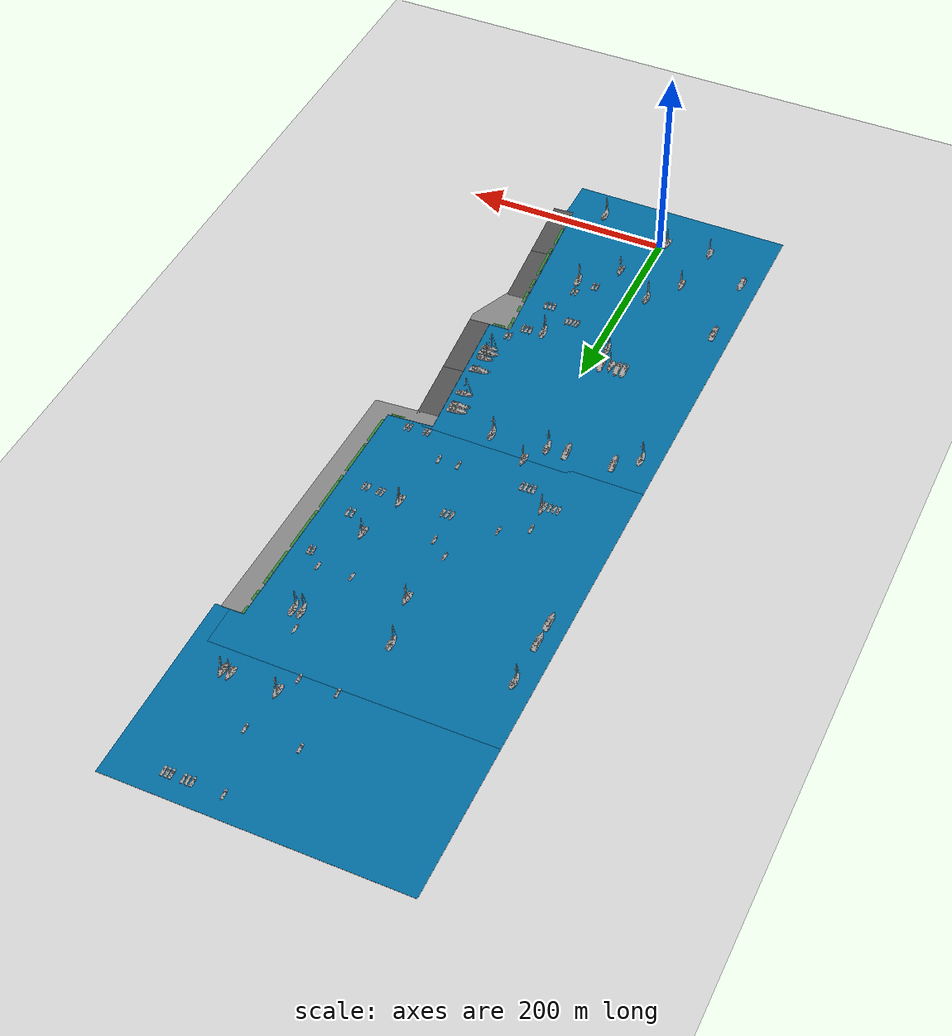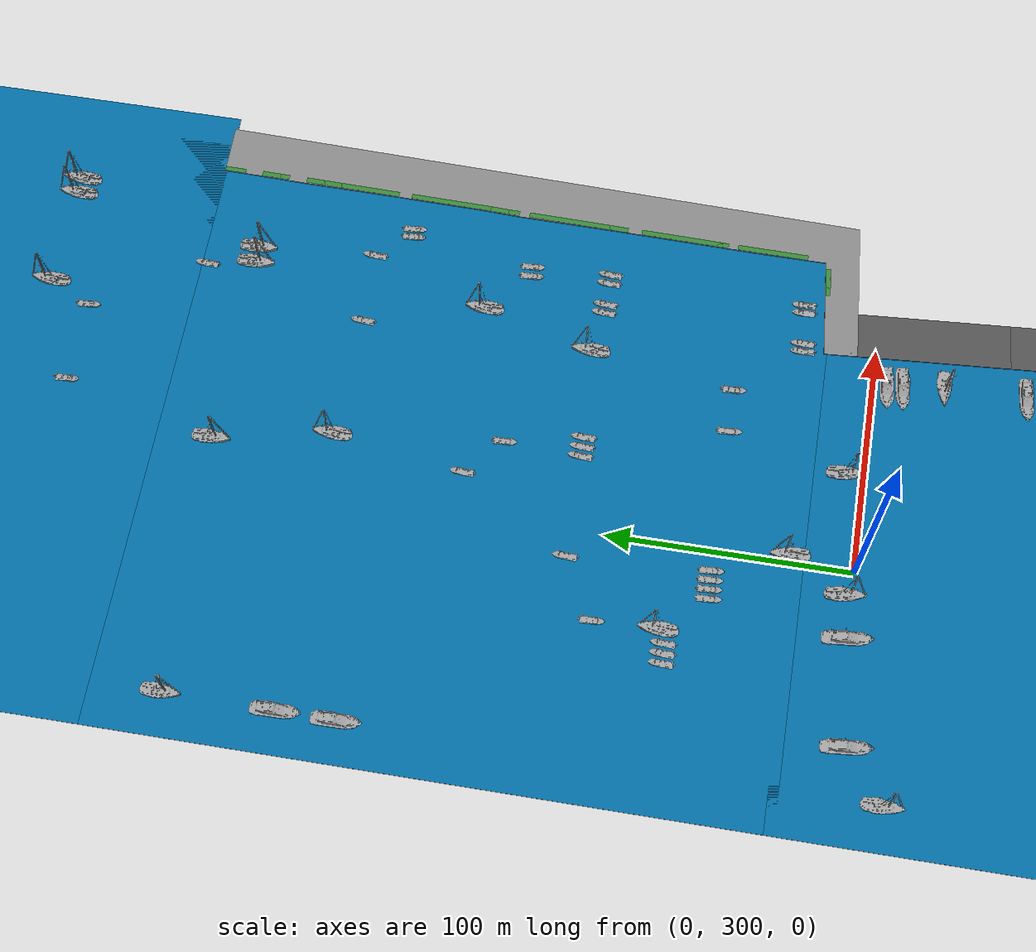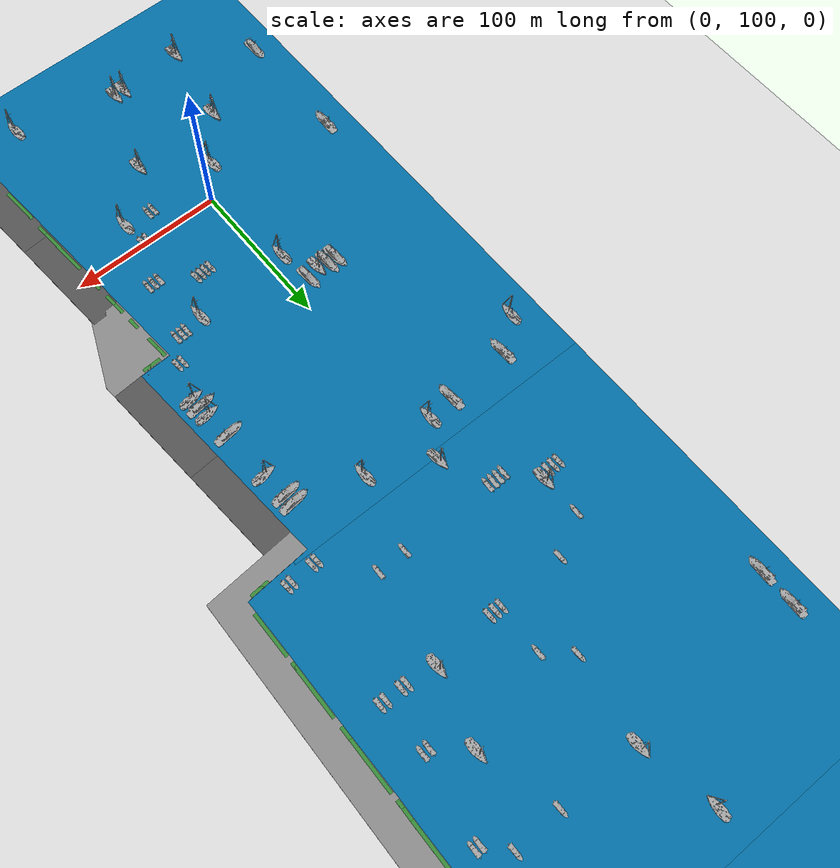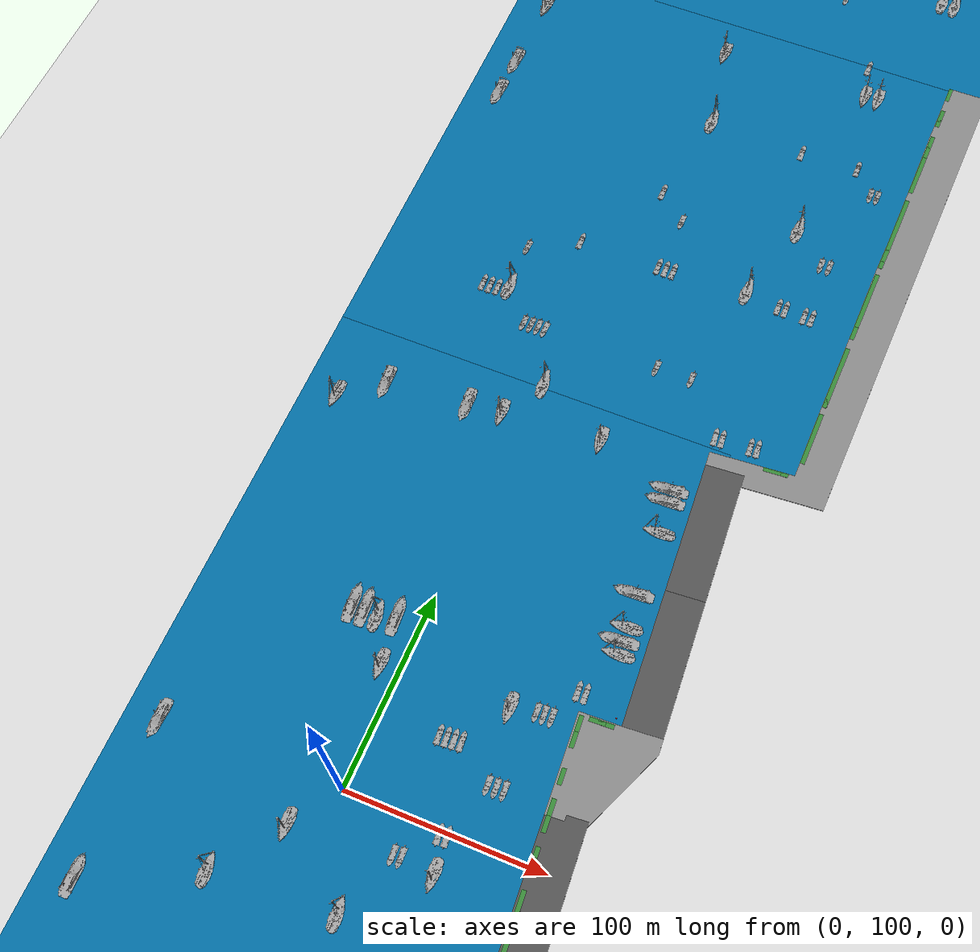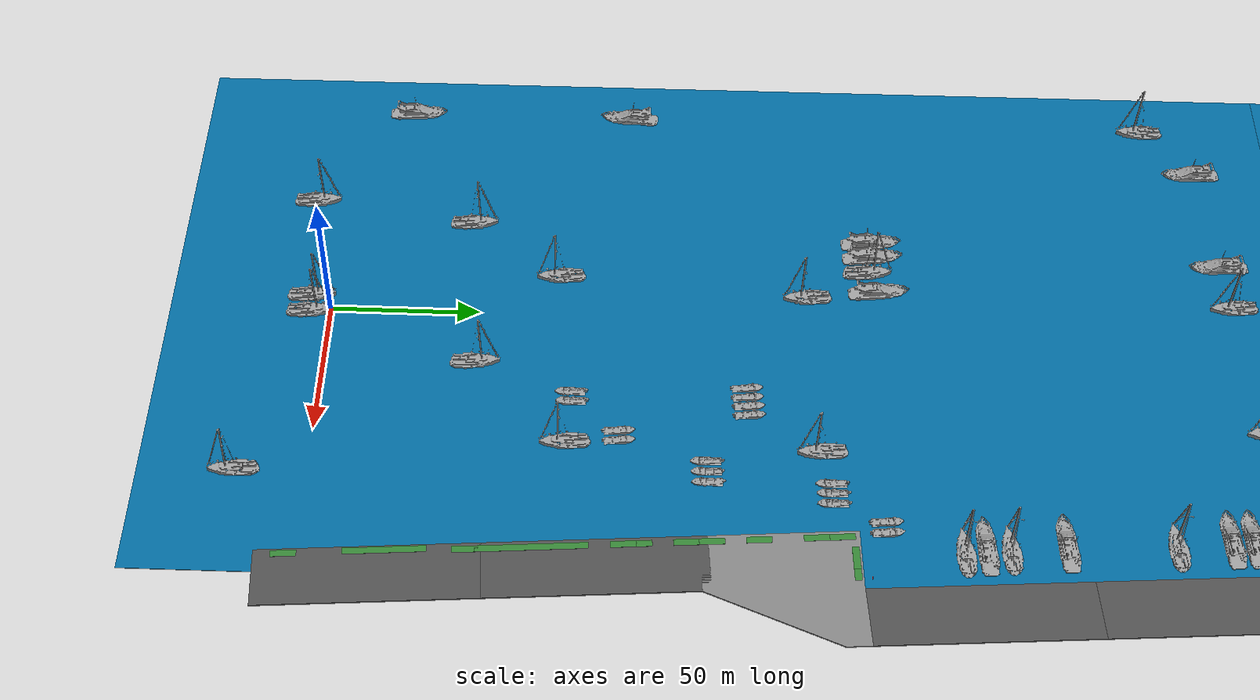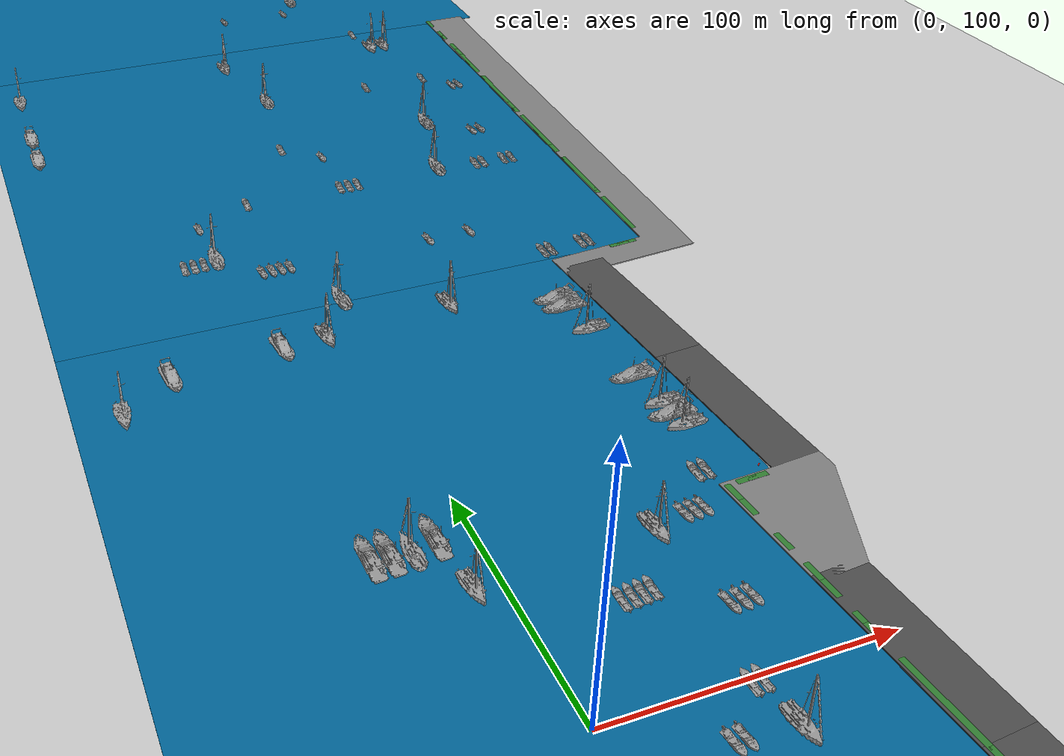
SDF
<sdf version="1.7">
 <world name="default">
  <plugin name="gazebo_ros_state" filename="libgazebo_ros_state.so">
   <ros><namespace>/gazebo</namespace></ros>
   <update_rate>1.0</update_rate>
  </plugin>
  <model name="ground_plane">
   <static>1</static>
   <link name="link">
    <collision name="collision">
     <geometry><plane><normal>0 0 1</normal><size>100 100</size></plane></geometry>
     <surface><friction><ode><mu>100</mu><mu2>50</mu2></ode></friction></surface>
    </collision>
    <visual name="visual">
     <cast_shadows>0</cast_shadows>
     <geometry><plane><normal>0 0 1</normal><size>100 100</size></plane></geometry>
     <material>
      <script><uri>file://media/materials/scripts/gazebo.material</uri><name>Gazebo/Grey</name></script>
     </material>
    </visual>
   </link>
  </model>
  <gravity>0 0 -9.8</gravity>
  <magnetic_field>6e-06 2.3e-05 -4.2e-05</magnetic_field>
  <atmosphere type="adiabatic"/>
  <physics type="ode">
   <max_step_size>0.001</max_step_size>
   <real_time_factor>1</real_time_factor>
   <real_time_update_rate>1000</real_time_update_rate>
  </physics>
  <scene><ambient>0.4 0.4 0.4 1</ambient><background>0.7 0.7 0.7 1</background><shadows>0</shadows></scene>
  <audio><device>default</device></audio>
  <spherical_coordinates>
   <surface_model>EARTH_WGS84</surface_model>
   <latitude_deg>0</latitude_deg>
   <longitude_deg>0</longitude_deg>
   <elevation>0</elevation>
   <heading_deg>0</heading_deg>
  </spherical_coordinates>
  <light name="sun" type="directional">
   <pose>-37.2448 -35.311 10 0 -0 0</pose>
   <diffuse>0.8 0.8 0.8 1</diffuse>
   <specular>0.2 0.2 0.2 1</specular>
   <attenuation>
    <range>1000</range>
    <constant>0.9</constant>
    <linear>0.01</linear>
    <quadratic>0.001</quadratic>
   </attenuation>
   <direction>-0.5 0.1 -0.9</direction>
   <spot><inner_angle>0</inner_angle><outer_angle>0</outer_angle><falloff>0</falloff></spot>
  </light>
  <light name="sun_clone" type="directional">
   <pose>31.987 4.34201 10 0 -0 0</pose>
   <diffuse>0.8 0.8 0.8 1</diffuse>
   <specular>0.2 0.2 0.2 1</specular>
   <direction>-0.483368 0.096674 -0.870063</direction>
   <attenuation>
    <range>1000</range>
    <constant>0.9</constant>
    <linear>0.01</linear>
    <quadratic>0.001</quadratic>
   </attenuation>
   <spot><inner_angle>0</inner_angle><outer_angle>0</outer_angle><falloff>0</falloff></spot>
  </light>
  <model name="Marina_Zona_A">
   <link name="link">
    <inertial>
     <mass>100000</mass>
     <inertia><ixx>0</ixx><ixy>0</ixy><ixz>0</ixz><iyy>0</iyy><iyz>0</iyz><izz>0</izz></inertia>
    </inertial>
    <visual name="visual">
     <geometry>
      <mesh>
       <uri>/home/albert/marinero_ws/src/marinero_simulations/models/Marina_Zona_A/meshes/Marina_Zona_A.stl</uri>
       <scale>1 1 1</scale>
      </mesh>
     </geometry>
     <material>
      <script><uri>file://media/materials/scripts/gazebo.material</uri><name>Gazebo/Brown</name></script>
      <ambient>0.278 0.129 0.02 1</ambient>
      <diffuse>0.278 0.129 0.02 1</diffuse>
      <specular>0.278 0.129 0.02 1</specular>
      <emissive>0 0 0 1</emissive>
      <shader type="pixel"><normal_map>__default__</normal_map></shader>
     </material>
    </visual>
    <collision name="collision">
     <geometry>
      <mesh>
       <uri>/home/albert/marinero_ws/src/marinero_simulations/models/Marina_Zona_A/meshes/Marina_Zona_A.stl</uri>
       <scale>1 1 1</scale>
      </mesh>
     </geometry>
     <surface>
      <friction>
       <ode><mu>0.9</mu><mu2>0.9</mu2><fdir1>0 0 0</fdir1><slip1>0.001</slip1><slip2>1e-05</slip2></ode>
       <torsional>
        <coefficient>1</coefficient>
        <patch_radius>0</patch_radius>
        <surface_radius>0</surface_radius>
        <use_patch_radius>1</use_patch_radius>
        <ode><slip>0</slip></ode>
       </torsional>
      </friction>
      <bounce><restitution_coefficient>0</restitution_coefficient><threshold>1000</threshold></bounce>
      <contact>
       <collide_without_contact>0</collide_without_contact>
       <collide_without_contact_bitmask>0</collide_without_contact_bitmask>
       <collide_bitmask>1</collide_bitmask>
       <ode>
        <soft_cfm>0</soft_cfm>
        <soft_erp>0.2</soft_erp>
        <kp>1e+11</kp>
        <kd>100</kd>
        <max_vel>10</max_vel>
        <min_depth>0.001</min_depth>
       </ode>
       <bullet>
        <split_impulse>1</split_impulse>
        <split_impulse_penetration_threshold>-0.01</split_impulse_penetration_threshold>
        <soft_cfm>0</soft_cfm>
        <soft_erp>0.2</soft_erp>
        <kp>1e+11</kp>
        <kd>100</kd>
       </bullet>
      </contact>
     </surface>
    </collision>
   </link>
   <static>1</static>
   <pose>-100.227 -48.3185 0.08 0 -0 0</pose>
  </model>
  <model name="Marina_Zona_B">
   <link name="link">
    <inertial>
     <mass>100000</mass>
     <inertia><ixx>0</ixx><ixy>0</ixy><ixz>0</ixz><iyy>0</iyy><iyz>0</iyz><izz>0</izz></inertia>
    </inertial>
    <visual name="visual">
     <geometry>
      <mesh>
       <uri>/home/albert/marinero_ws/src/marinero_simulations/models/Marina_Zona_B/meshes/Marina_Zona_B.stl</uri>
       <scale>1 1 1</scale>
      </mesh>
     </geometry>
     <material>
      <script><uri>file://media/materials/scripts/gazebo.material</uri><name>Gazebo/Brown</name></script>
      <ambient>0.278 0.129 0.02 1</ambient>
      <diffuse>0.278 0.129 0.02 1</diffuse>
      <specular>0.278 0.129 0.02 1</specular>
      <emissive>0 0 0 1</emissive>
      <shader type="pixel"><normal_map>__default__</normal_map></shader>
     </material>
    </visual>
    <collision name="collision">
     <geometry>
      <mesh>
       <uri>/home/albert/marinero_ws/src/marinero_simulations/models/Marina_Zona_B/meshes/Marina_Zona_B.stl</uri>
       <scale>1 1 1</scale>
      </mesh>
     </geometry>
     <surface>
      <friction>
       <ode><mu>0.9</mu><mu2>0.9</mu2><fdir1>0 0 0</fdir1><slip1>0.001</slip1><slip2>1e-05</slip2></ode>
       <torsional>
        <coefficient>1</coefficient>
        <patch_radius>0</patch_radius>
        <surface_radius>0</surface_radius>
        <use_patch_radius>1</use_patch_radius>
        <ode><slip>0</slip></ode>
       </torsional>
      </friction>
      <bounce><restitution_coefficient>0</restitution_coefficient><threshold>1000</threshold></bounce>
      <contact>
       <collide_without_contact>0</collide_without_contact>
       <collide_without_contact_bitmask>0</collide_without_contact_bitmask>
       <collide_bitmask>1</collide_bitmask>
       <ode>
        <soft_cfm>0</soft_cfm>
        <soft_erp>0.2</soft_erp>
        <kp>1e+11</kp>
        <kd>100</kd>
        <max_vel>10</max_vel>
        <min_depth>0.001</min_depth>
       </ode>
       <bullet>
        <split_impulse>1</split_impulse>
        <split_impulse_penetration_threshold>-0.01</split_impulse_penetration_threshold>
        <soft_cfm>0</soft_cfm>
        <soft_erp>0.2</soft_erp>
        <kp>1e+11</kp>
        <kd>100</kd>
       </bullet>
      </contact>
     </surface>
    </collision>
   </link>
   <static>1</static>
   <pose>94.3188 292.84 0.08 0 -0 0</pose>
  </model>
  <model name="Marina_Zona_C">
   <link name="link">
    <inertial>
     <mass>50000</mass>
     <inertia><ixx>0</ixx><ixy>0</ixy><ixz>0</ixz><iyy>0</iyy><iyz>0</iyz><izz>0</izz></inertia>
    </inertial>
    <visual name="visual">
     <geometry>
      <mesh>
       <uri>/home/albert/marinero_ws/src/marinero_simulations/models/Marina_Zona_C/meshes/Marina_Zona_C.stl</uri>
       <scale>1 1 1</scale>
      </mesh>
     </geometry>
     <material>
      <script><uri>file://media/materials/scripts/gazebo.material</uri><name>Gazebo/Brown</name></script>
      <ambient>0.278 0.129 0.02 1</ambient>
      <diffuse>0.278 0.129 0.02 1</diffuse>
      <specular>0.278 0.129 0.02 1</specular>
      <emissive>0 0 0 1</emissive>
      <shader type="pixel"><normal_map>__default__</normal_map></shader>
     </material>
    </visual>
    <collision name="collision">
     <geometry>
      <mesh>
       <uri>/home/albert/marinero_ws/src/marinero_simulations/models/Marina_Zona_C/meshes/Marina_Zona_C.stl</uri>
       <scale>1 1 1</scale>
      </mesh>
     </geometry>
     <surface>
      <friction>
       <ode><mu>0.9</mu><mu2>0.9</mu2><fdir1>0 0 0</fdir1><slip1>0.001</slip1><slip2>1e-05</slip2></ode>
       <torsional>
        <coefficient>1</coefficient>
        <patch_radius>0</patch_radius>
        <surface_radius>0</surface_radius>
        <use_patch_radius>1</use_patch_radius>
        <ode><slip>0</slip></ode>
       </torsional>
      </friction>
      <bounce><restitution_coefficient>0</restitution_coefficient><threshold>1000</threshold></bounce>
      <contact>
       <collide_without_contact>0</collide_without_contact>
       <collide_without_contact_bitmask>0</collide_without_contact_bitmask>
       <collide_bitmask>1</collide_bitmask>
       <ode>
        <soft_cfm>0</soft_cfm>
        <soft_erp>0.2</soft_erp>
        <kp>1e+11</kp>
        <kd>100</kd>
        <max_vel>10</max_vel>
        <min_depth>0.001</min_depth>
       </ode>
       <bullet>
        <split_impulse>1</split_impulse>
        <split_impulse_penetration_threshold>-0.01</split_impulse_penetration_threshold>
        <soft_cfm>0</soft_cfm>
        <soft_erp>0.2</soft_erp>
        <kp>1e+11</kp>
        <kd>100</kd>
       </bullet>
      </contact>
     </surface>
    </collision>
   </link>
   <static>1</static>
   <pose>140.34 587.6 0.08 0 -0 0</pose>
  </model>
  <model name="asphalt_plane_0_clone">
   <link name="link">
    <pose>0 0 1.015 0 -0 0</pose>
    <inertial>
     <mass>1</mass>
     <inertia><ixx>1</ixx><ixy>0</ixy><ixz>0</ixz><iyy>1</iyy><iyz>0</iyz><izz>1</izz></inertia>
    </inertial>
    <visual name="visual">
     <cast_shadows>0</cast_shadows>
     <geometry><box><size>70 20 0.5</size></box></geometry>
     <material>
      <script>
       <uri>model://asphalt_plane/materials/scripts</uri>
       <uri>model://asphalt_plane/materials/textures</uri>
       <name>vrc/asphalt</name>
      </script>
      <shader type="pixel"><normal_map>__default__</normal_map></shader>
      <ambient>0.5 0.5 0.5 1</ambient>
      <diffuse>0.5 0.5 0.5 1</diffuse>
      <specular>0.2 0.2 0.2 1</specular>
      <emissive>0 0 0 1</emissive>
     </material>
    </visual>
    <collision name="collision">
     <geometry><box><size>70 20 0.5</size></box></geometry>
     <surface>
      <friction>
       <ode><mu>1</mu><mu2>1</mu2><fdir1>0 0 0</fdir1><slip1>0.001</slip1><slip2>1e-05</slip2></ode>
       <torsional>
        <coefficient>1</coefficient>
        <patch_radius>0</patch_radius>
        <surface_radius>0</surface_radius>
        <use_patch_radius>1</use_patch_radius>
        <ode><slip>0</slip></ode>
       </torsional>
      </friction>
      <bounce><restitution_coefficient>0</restitution_coefficient><threshold>1e+06</threshold></bounce>
      <contact>
       <collide_without_contact>0</collide_without_contact>
       <collide_without_contact_bitmask>1</collide_without_contact_bitmask>
       <collide_bitmask>1</collide_bitmask>
       <ode>
        <soft_cfm>0</soft_cfm>
        <soft_erp>0.2</soft_erp>
        <kp>1e+13</kp>
        <kd>1</kd>
        <max_vel>0.01</max_vel>
        <min_depth>0</min_depth>
       </ode>
       <bullet>
        <split_impulse>1</split_impulse>
        <split_impulse_penetration_threshold>-0.01</split_impulse_penetration_threshold>
        <soft_cfm>0</soft_cfm>
        <soft_erp>0.2</soft_erp>
        <kp>1e+13</kp>
        <kd>1</kd>
       </bullet>
      </contact>
     </surface>
    </collision>
   </link>
   <static>1</static>
   <pose>100.593 92.427 0 0 0 -1.498</pose>
  </model>
  <model name="asphalt_plane_1">
   <link name="link">
    <pose>0 0 1.015 0 -0 0</pose>
    <inertial>
     <mass>1</mass>
     <inertia><ixx>1</ixx><ixy>0</ixy><ixz>0</ixz><iyy>1</iyy><iyz>0</iyz><izz>1</izz></inertia>
    </inertial>
    <visual name="visual">
     <cast_shadows>0</cast_shadows>
     <geometry><box><size>70 20 0.5</size></box></geometry>
     <material>
      <script>
       <uri>model://asphalt_plane/materials/scripts</uri>
       <uri>model://asphalt_plane/materials/textures</uri>
       <name>vrc/asphalt</name>
      </script>
      <shader type="pixel"><normal_map>__default__</normal_map></shader>
      <ambient>0.5 0.5 0.5 1</ambient>
      <diffuse>0.5 0.5 0.5 1</diffuse>
      <specular>0.2 0.2 0.2 1</specular>
      <emissive>0 0 0 1</emissive>
     </material>
    </visual>
    <collision name="collision">
     <geometry><box><size>70 20 0.5</size></box></geometry>
     <surface>
      <friction>
       <ode><mu>1</mu><mu2>1</mu2><fdir1>0 0 0</fdir1><slip1>0.001</slip1><slip2>1e-05</slip2></ode>
       <torsional>
        <coefficient>1</coefficient>
        <patch_radius>0</patch_radius>
        <surface_radius>0</surface_radius>
        <use_patch_radius>1</use_patch_radius>
        <ode><slip>0</slip></ode>
       </torsional>
      </friction>
      <bounce><restitution_coefficient>0</restitution_coefficient><threshold>1e+06</threshold></bounce>
      <contact>
       <collide_without_contact>0</collide_without_contact>
       <collide_without_contact_bitmask>1</collide_without_contact_bitmask>
       <collide_bitmask>1</collide_bitmask>
       <ode>
        <soft_cfm>0</soft_cfm>
        <soft_erp>0.2</soft_erp>
        <kp>1e+13</kp>
        <kd>1</kd>
        <max_vel>0.01</max_vel>
        <min_depth>0</min_depth>
       </ode>
       <bullet>
        <split_impulse>1</split_impulse>
        <split_impulse_penetration_threshold>-0.01</split_impulse_penetration_threshold>
        <soft_cfm>0</soft_cfm>
        <soft_erp>0.2</soft_erp>
        <kp>1e+13</kp>
        <kd>1</kd>
       </bullet>
      </contact>
     </surface>
    </collision>
   </link>
   <static>1</static>
   <pose>113.068 209.915 0 0 0 -1.5</pose>
  </model>
  <model name="asphalt_plane_1_clone">
   <link name="link">
    <pose>0 0 1.015 0 -0 0</pose>
    <inertial>
     <mass>1</mass>
     <inertia><ixx>1</ixx><ixy>0</ixy><ixz>0</ixz><iyy>1</iyy><iyz>0</iyz><izz>1</izz></inertia>
    </inertial>
    <visual name="visual">
     <cast_shadows>0</cast_shadows>
     <geometry><box><size>70 20 0.5</size></box></geometry>
     <material>
      <script>
       <uri>model://asphalt_plane/materials/scripts</uri>
       <uri>model://asphalt_plane/materials/textures</uri>
       <name>vrc/asphalt</name>
      </script>
      <shader type="pixel"><normal_map>__default__</normal_map></shader>
      <ambient>0.5 0.5 0.5 1</ambient>
      <diffuse>0.5 0.5 0.5 1</diffuse>
      <specular>0.2 0.2 0.2 1</specular>
      <emissive>0 0 0 1</emissive>
     </material>
    </visual>
    <collision name="collision">
     <geometry><box><size>70 20 0.5</size></box></geometry>
     <surface>
      <friction>
       <ode><mu>1</mu><mu2>1</mu2><fdir1>0 0 0</fdir1><slip1>0.001</slip1><slip2>1e-05</slip2></ode>
       <torsional>
        <coefficient>1</coefficient>
        <patch_radius>0</patch_radius>
        <surface_radius>0</surface_radius>
        <use_patch_radius>1</use_patch_radius>
        <ode><slip>0</slip></ode>
       </torsional>
      </friction>
      <bounce><restitution_coefficient>0</restitution_coefficient><threshold>1e+06</threshold></bounce>
      <contact>
       <collide_without_contact>0</collide_without_contact>
       <collide_without_contact_bitmask>1</collide_without_contact_bitmask>
       <collide_bitmask>1</collide_bitmask>
       <ode>
        <soft_cfm>0</soft_cfm>
        <soft_erp>0.2</soft_erp>
        <kp>1e+13</kp>
        <kd>1</kd>
        <max_vel>0.01</max_vel>
        <min_depth>0</min_depth>
       </ode>
       <bullet>
        <split_impulse>1</split_impulse>
        <split_impulse_penetration_threshold>-0.01</split_impulse_penetration_threshold>
        <soft_cfm>0</soft_cfm>
        <soft_erp>0.2</soft_erp>
        <kp>1e+13</kp>
        <kd>1</kd>
       </bullet>
      </contact>
     </surface>
    </collision>
   </link>
   <static>1</static>
   <pose>108.119 279.695 0 0 0 -1.5</pose>
  </model>
  <model name="asphalt_plane_angle_section_0">
   <link name="link">
    <inertial>
     <mass>1</mass>
     <inertia><ixx>1</ixx><ixy>0</ixy><ixz>0</ixz><iyy>1</iyy><iyz>0</iyz><izz>1</izz></inertia>
    </inertial>
    <pose>0 0 1.015 0 0 -1.4967</pose>
    <visual name="visual">
     <geometry>
      <mesh>
       <uri>/home/albert/marinero_ws/src/marinero_simulations/models/asphalt_plane_angle_section/meshes/asphalt_plane_angle_section.dae</uri>
       <scale>1 1 5</scale>
      </mesh>
     </geometry>
     <material>
      <script>
       <uri>/home/albert/marinero_ws/src/marinero_simulations/models/asphalt_plane_angle_section/materials/scripts</uri>
       <uri>/home/albert/marinero_ws/src/marinero_simulations/models/asphalt_plane_angle_section/materials/textures</uri>
       <name>asphalt/texture</name>
      </script>
      <shader type="pixel"><normal_map>__default__</normal_map></shader>
      <ambient>0.5 0.5 0.5 1</ambient>
      <diffuse>0.5 0.5 0.5 1</diffuse>
      <specular>0.2 0.2 0.2 1</specular>
      <emissive>0 0 0 1</emissive>
     </material>
    </visual>
    <collision name="collision">
     <geometry>
      <mesh>
       <uri>/home/albert/marinero_ws/src/marinero_simulations/models/asphalt_plane_angle_section/meshes/asphalt_plane_angle_section.dae</uri>
       <scale>1 1 5</scale>
      </mesh>
     </geometry>
     <surface>
      <friction>
       <ode><mu>1</mu><mu2>1</mu2><fdir1>0 0 0</fdir1><slip1>0.001</slip1><slip2>1e-05</slip2></ode>
       <torsional>
        <coefficient>1</coefficient>
        <patch_radius>0</patch_radius>
        <surface_radius>0</surface_radius>
        <use_patch_radius>1</use_patch_radius>
        <ode><slip>0</slip></ode>
       </torsional>
      </friction>
      <bounce><restitution_coefficient>0</restitution_coefficient><threshold>1e+06</threshold></bounce>
      <contact>
       <collide_without_contact>0</collide_without_contact>
       <collide_without_contact_bitmask>1</collide_without_contact_bitmask>
       <collide_bitmask>1</collide_bitmask>
       <ode>
        <soft_cfm>0</soft_cfm>
        <soft_erp>0.2</soft_erp>
        <kp>1e+13</kp>
        <kd>1</kd>
        <max_vel>0.01</max_vel>
        <min_depth>0</min_depth>
       </ode>
       <bullet>
        <split_impulse>1</split_impulse>
        <split_impulse_penetration_threshold>-0.01</split_impulse_penetration_threshold>
        <soft_cfm>0</soft_cfm>
        <soft_erp>0.2</soft_erp>
        <kp>1e+13</kp>
        <kd>1</kd>
       </bullet>
      </contact>
     </surface>
    </collision>
   </link>
   <static>1</static>
   <pose>96.4113 149.332 0 0 -0 0</pose>
  </model>
  <model name="asphalt_plane_0_clone_clone">
   <link name="link">
    <pose>0 0 1.015 0 -0 0</pose>
    <inertial>
     <mass>1</mass>
     <inertia><ixx>1</ixx><ixy>0</ixy><ixz>0</ixz><iyy>1</iyy><iyz>0</iyz><izz>1</izz></inertia>
    </inertial>
    <visual name="visual">
     <cast_shadows>0</cast_shadows>
     <geometry><box><size>70 20 0.5</size></box></geometry>
     <material>
      <script>
       <uri>model://asphalt_plane/materials/scripts</uri>
       <uri>model://asphalt_plane/materials/textures</uri>
       <name>vrc/asphalt</name>
      </script>
      <shader type="pixel"><normal_map>__default__</normal_map></shader>
      <ambient>0.5 0.5 0.5 1</ambient>
      <diffuse>0.5 0.5 0.5 1</diffuse>
      <specular>0.2 0.2 0.2 1</specular>
      <emissive>0 0 0 1</emissive>
     </material>
    </visual>
    <collision name="collision">
     <geometry><box><size>70 20 0.5</size></box></geometry>
     <surface>
      <friction>
       <ode><mu>1</mu><mu2>1</mu2><fdir1>0 0 0</fdir1><slip1>0.001</slip1><slip2>1e-05</slip2></ode>
       <torsional>
        <coefficient>1</coefficient>
        <patch_radius>0</patch_radius>
        <surface_radius>0</surface_radius>
        <use_patch_radius>1</use_patch_radius>
        <ode><slip>0</slip></ode>
       </torsional>
      </friction>
      <bounce><restitution_coefficient>0</restitution_coefficient><threshold>1e+06</threshold></bounce>
      <contact>
       <collide_without_contact>0</collide_without_contact>
       <collide_without_contact_bitmask>1</collide_without_contact_bitmask>
       <collide_bitmask>1</collide_bitmask>
       <ode>
        <soft_cfm>0</soft_cfm>
        <soft_erp>0.2</soft_erp>
        <kp>1e+13</kp>
        <kd>1</kd>
        <max_vel>0.01</max_vel>
        <min_depth>0</min_depth>
       </ode>
       <bullet>
        <split_impulse>1</split_impulse>
        <split_impulse_penetration_threshold>-0.01</split_impulse_penetration_threshold>
        <soft_cfm>0</soft_cfm>
        <soft_erp>0.2</soft_erp>
        <kp>1e+13</kp>
        <kd>1</kd>
       </bullet>
      </contact>
     </surface>
    </collision>
   </link>
   <static>1</static>
   <pose>105.657 22.9966 0 0 0 -1.498</pose>
  </model>
  <model name="sailboat_1">
   <static>1</static>
   <link name="link">
    <visual name="visual">
     <pose>0 0 1 0 0 -1.507</pose>
     <geometry>
      <mesh>
       <uri>/home/albert/marinero_ws/src/marinero_simulations/models/sailboat_1/meshes/Sailboat.stl</uri>
       <scale>1.8 1.8 1.8</scale>
      </mesh>
     </geometry>
     <material>
      <script><uri>file://media/materials/scripts/gazebo.material</uri><name>Gazebo/Grey</name></script>
     </material>
    </visual>
    <collision name="collision">
     <pose>0 0 1 0 0 -1.507</pose>
     <geometry>
      <mesh>
       <uri>/home/albert/marinero_ws/src/marinero_simulations/models/sailboat_1/meshes/Sailboat.stl</uri>
       <scale>1.8 1.8 1.8</scale>
      </mesh>
     </geometry>
    </collision>
   </link>
   <pose>-48.5208 -10.4492 0 0 -0 0</pose>
  </model>
  <model name="sailboat_1_clone">
   <static>1</static>
   <link name="link">
    <visual name="visual">
     <pose>0 0 1 0 0 -1.507</pose>
     <geometry>
      <mesh>
       <uri>/home/albert/marinero_ws/src/marinero_simulations/models/sailboat_1/meshes/Sailboat.stl</uri>
       <scale>1.8 1.8 1.8</scale>
      </mesh>
     </geometry>
     <material>
      <script><uri>file://media/materials/scripts/gazebo.material</uri><name>Gazebo/Grey</name></script>
     </material>
    </visual>
    <collision name="collision">
     <pose>0 0 1 0 0 -1.507</pose>
     <geometry>
      <mesh>
       <uri>/home/albert/marinero_ws/src/marinero_simulations/models/sailboat_1/meshes/Sailboat.stl</uri>
       <scale>1.8 1.8 1.8</scale>
      </mesh>
     </geometry>
    </collision>
   </link>
   <pose>-39.7569 44.9738 0 0 -0 0</pose>
  </model>
  <model name="sailboat_1_clone_0">
   <static>1</static>
   <link name="link">
    <visual name="visual">
     <pose>0 0 1 0 0 -1.507</pose>
     <geometry>
      <mesh>
       <uri>/home/albert/marinero_ws/src/marinero_simulations/models/sailboat_1/meshes/Sailboat.stl</uri>
       <scale>1.8 1.8 1.8</scale>
      </mesh>
     </geometry>
     <material>
      <script><uri>file://media/materials/scripts/gazebo.material</uri><name>Gazebo/Grey</name></script>
     </material>
    </visual>
    <collision name="collision">
     <pose>0 0 1 0 0 -1.507</pose>
     <geometry>
      <mesh>
       <uri>/home/albert/marinero_ws/src/marinero_simulations/models/sailboat_1/meshes/Sailboat.stl</uri>
       <scale>1.8 1.8 1.8</scale>
      </mesh>
     </geometry>
    </collision>
   </link>
   <pose>21.7205 49.4998 0 0 -0 0</pose>
  </model>
  <model name="sailboat_1_clone_1">
   <static>1</static>
   <link name="link">
    <visual name="visual">
     <pose>0 0 1 0 0 -1.507</pose>
     <geometry>
      <mesh>
       <uri>/home/albert/marinero_ws/src/marinero_simulations/models/sailboat_1/meshes/Sailboat.stl</uri>
       <scale>1.8 1.8 1.8</scale>
      </mesh>
     </geometry>
     <material>
      <script><uri>file://media/materials/scripts/gazebo.material</uri><name>Gazebo/Grey</name></script>
     </material>
    </visual>
    <collision name="collision">
     <pose>0 0 1 0 0 -1.507</pose>
     <geometry>
      <mesh>
       <uri>/home/albert/marinero_ws/src/marinero_simulations/models/sailboat_1/meshes/Sailboat.stl</uri>
       <scale>1.8 1.8 1.8</scale>
      </mesh>
     </geometry>
    </collision>
   </link>
   <pose>67.7231 -22.5244 0 0 0 -3.13388</pose>
  </model>
  <model name="sailboat_1_clone_1_clone">
   <static>1</static>
   <link name="link">
    <visual name="visual">
     <pose>0 0 1 0 0 -1.507</pose>
     <geometry>
      <mesh>
       <uri>/home/albert/marinero_ws/src/marinero_simulations/models/sailboat_1/meshes/Sailboat.stl</uri>
       <scale>1.8 1.8 1.8</scale>
      </mesh>
     </geometry>
     <material>
      <script><uri>file://media/materials/scripts/gazebo.material</uri><name>Gazebo/Grey</name></script>
     </material>
    </visual>
    <collision name="collision">
     <pose>0 0 1 0 0 -1.507</pose>
     <geometry>
      <mesh>
       <uri>/home/albert/marinero_ws/src/marinero_simulations/models/sailboat_1/meshes/Sailboat.stl</uri>
       <scale>1.8 1.8 1.8</scale>
      </mesh>
     </geometry>
    </collision>
   </link>
   <pose>53.4256 81.5662 0 0 0 -3.13388</pose>
  </model>
  <model name="sailboat_1_clone_1_clone_0">
   <static>1</static>
   <link name="link">
    <visual name="visual">
     <pose>0 0 1 0 0 -1.507</pose>
     <geometry>
      <mesh>
       <uri>/home/albert/marinero_ws/src/marinero_simulations/models/sailboat_1/meshes/Sailboat.stl</uri>
       <scale>1.8 1.8 1.8</scale>
      </mesh>
     </geometry>
     <material>
      <script><uri>file://media/materials/scripts/gazebo.material</uri><name>Gazebo/Grey</name></script>
     </material>
    </visual>
    <collision name="collision">
     <pose>0 0 1 0 0 -1.507</pose>
     <geometry>
      <mesh>
       <uri>/home/albert/marinero_ws/src/marinero_simulations/models/sailboat_1/meshes/Sailboat.stl</uri>
       <scale>1.8 1.8 1.8</scale>
      </mesh>
     </geometry>
    </collision>
   </link>
   <pose>42.3985 307.643 0 0 0 -3.13388</pose>
  </model>
  <model name="sailboat_1_clone_1_clone_1">
   <static>1</static>
   <link name="link">
    <visual name="visual">
     <pose>0 0 1 0 0 -1.507</pose>
     <geometry>
      <mesh>
       <uri>/home/albert/marinero_ws/src/marinero_simulations/models/sailboat_1/meshes/Sailboat.stl</uri>
       <scale>1.8 1.8 1.8</scale>
      </mesh>
     </geometry>
     <material>
      <script><uri>file://media/materials/scripts/gazebo.material</uri><name>Gazebo/Grey</name></script>
     </material>
    </visual>
    <collision name="collision">
     <pose>0 0 1 0 0 -1.507</pose>
     <geometry>
      <mesh>
       <uri>/home/albert/marinero_ws/src/marinero_simulations/models/sailboat_1/meshes/Sailboat.stl</uri>
       <scale>1.8 1.8 1.8</scale>
      </mesh>
     </geometry>
    </collision>
   </link>
   <pose>-9.86745 303.465 0 0 0 -3.13388</pose>
  </model>
  <model name="sailboat_1_0">
   <static>1</static>
   <link name="link">
    <visual name="visual">
     <pose>0 0 1 0 0 -1.507</pose>
     <geometry>
      <mesh>
       <uri>/home/albert/marinero_ws/src/marinero_simulations/models/sailboat_1/meshes/Sailboat.stl</uri>
       <scale>1.8 1.8 1.8</scale>
      </mesh>
     </geometry>
     <material>
      <script><uri>file://media/materials/scripts/gazebo.material</uri><name>Gazebo/Grey</name></script>
     </material>
    </visual>
    <collision name="collision">
     <pose>0 0 1 0 0 -1.507</pose>
     <geometry>
      <mesh>
       <uri>/home/albert/marinero_ws/src/marinero_simulations/models/sailboat_1/meshes/Sailboat.stl</uri>
       <scale>1.8 1.8 1.8</scale>
      </mesh>
     </geometry>
    </collision>
   </link>
   <pose>-21.2995 180.013 0 0 -0 0</pose>
  </model>
  <model name="sailboat_1_clone_1_clone_clone">
   <static>1</static>
   <link name="link">
    <visual name="visual">
     <pose>0 0 1 0 0 -1.507</pose>
     <geometry>
      <mesh>
       <uri>/home/albert/marinero_ws/src/marinero_simulations/models/sailboat_1/meshes/Sailboat.stl</uri>
       <scale>1.8 1.8 1.8</scale>
      </mesh>
     </geometry>
     <material>
      <script><uri>file://media/materials/scripts/gazebo.material</uri><name>Gazebo/Grey</name></script>
     </material>
    </visual>
    <collision name="collision">
     <pose>0 0 1 0 0 -1.507</pose>
     <geometry>
      <mesh>
       <uri>/home/albert/marinero_ws/src/marinero_simulations/models/sailboat_1/meshes/Sailboat.stl</uri>
       <scale>1.8 1.8 1.8</scale>
      </mesh>
     </geometry>
    </collision>
   </link>
   <pose>54.6406 163.676 0 0 0 -3.13388</pose>
  </model>
  <model name="sailboat_1_clone_1_clone_clone_0">
   <static>1</static>
   <link name="link">
    <visual name="visual">
     <pose>0 0 1 0 0 -1.507</pose>
     <geometry>
      <mesh>
       <uri>/home/albert/marinero_ws/src/marinero_simulations/models/sailboat_1/meshes/Sailboat.stl</uri>
       <scale>1.8 1.8 1.8</scale>
      </mesh>
     </geometry>
     <material>
      <script><uri>file://media/materials/scripts/gazebo.material</uri><name>Gazebo/Grey</name></script>
     </material>
    </visual>
    <collision name="collision">
     <pose>0 0 1 0 0 -1.507</pose>
     <geometry>
      <mesh>
       <uri>/home/albert/marinero_ws/src/marinero_simulations/models/sailboat_1/meshes/Sailboat.stl</uri>
       <scale>1.8 1.8 1.8</scale>
      </mesh>
     </geometry>
    </collision>
   </link>
   <pose>-9.56395 160.572 0 0 0 -3.13388</pose>
  </model>
  <model name="sailboat_1_1">
   <static>1</static>
   <link name="link">
    <visual name="visual">
     <pose>0 0 1 0 0 -1.507</pose>
     <geometry>
      <mesh>
       <uri>/home/albert/marinero_ws/src/marinero_simulations/models/sailboat_1/meshes/Sailboat.stl</uri>
       <scale>1.8 1.8 1.8</scale>
      </mesh>
     </geometry>
     <material>
      <script><uri>file://media/materials/scripts/gazebo.material</uri><name>Gazebo/Grey</name></script>
     </material>
    </visual>
    <collision name="collision">
     <pose>0 0 1 0 0 -1.507</pose>
     <geometry>
      <mesh>
       <uri>/home/albert/marinero_ws/src/marinero_simulations/models/sailboat_1/meshes/Sailboat.stl</uri>
       <scale>1.8 1.8 1.8</scale>
      </mesh>
     </geometry>
    </collision>
   </link>
   <pose>-35.7155 372.867 0 0 0 -0.077596</pose>
  </model>
  <model name="sailboat_1_1_clone_0">
   <static>1</static>
   <link name="link">
    <visual name="visual">
     <pose>0 0 1 0 0 -1.507</pose>
     <geometry>
      <mesh>
       <uri>/home/albert/marinero_ws/src/marinero_simulations/models/sailboat_1/meshes/Sailboat.stl</uri>
       <scale>1.8 1.8 1.8</scale>
      </mesh>
     </geometry>
     <material>
      <script><uri>file://media/materials/scripts/gazebo.material</uri><name>Gazebo/Grey</name></script>
     </material>
    </visual>
    <collision name="collision">
     <pose>0 0 1 0 0 -1.507</pose>
     <geometry>
      <mesh>
       <uri>/home/albert/marinero_ws/src/marinero_simulations/models/sailboat_1/meshes/Sailboat.stl</uri>
       <scale>1.8 1.8 1.8</scale>
      </mesh>
     </geometry>
    </collision>
   </link>
   <pose>93.9449 463.734 0 0 0 -0.077596</pose>
  </model>
  <model name="sailboat_1_1_clone_1">
   <static>1</static>
   <link name="link">
    <visual name="visual">
     <pose>0 0 1 0 0 -1.507</pose>
     <geometry>
      <mesh>
       <uri>/home/albert/marinero_ws/src/marinero_simulations/models/sailboat_1/meshes/Sailboat.stl</uri>
       <scale>1.8 1.8 1.8</scale>
      </mesh>
     </geometry>
     <material>
      <script><uri>file://media/materials/scripts/gazebo.material</uri><name>Gazebo/Grey</name></script>
     </material>
    </visual>
    <collision name="collision">
     <pose>0 0 1 0 0 -1.507</pose>
     <geometry>
      <mesh>
       <uri>/home/albert/marinero_ws/src/marinero_simulations/models/sailboat_1/meshes/Sailboat.stl</uri>
       <scale>1.8 1.8 1.8</scale>
      </mesh>
     </geometry>
    </collision>
   </link>
   <pose>77.9434 647.569 0 0 0 -0.077596</pose>
  </model>
  <model name="sailboat_1_clone_1_clone_clone_0_clone">
   <static>1</static>
   <link name="link">
    <visual name="visual">
     <pose>0 0 1 0 0 -1.507</pose>
     <geometry>
      <mesh>
       <uri>/home/albert/marinero_ws/src/marinero_simulations/models/sailboat_1/meshes/Sailboat.stl</uri>
       <scale>1.8 1.8 1.8</scale>
      </mesh>
     </geometry>
     <material>
      <script><uri>file://media/materials/scripts/gazebo.material</uri><name>Gazebo/Grey</name></script>
     </material>
    </visual>
    <collision name="collision">
     <pose>0 0 1 0 0 -1.507</pose>
     <geometry>
      <mesh>
       <uri>/home/albert/marinero_ws/src/marinero_simulations/models/sailboat_1/meshes/Sailboat.stl</uri>
       <scale>1.8 1.8 1.8</scale>
      </mesh>
     </geometry>
    </collision>
   </link>
   <pose>-91.8625 281.936 0 0 -0 3.06385</pose>
  </model>
  <model name="speedboat">
   <static>1</static>
   <link name="link">
    <visual name="visual">
     <pose>0 0 0.2 0 -0 1.57</pose>
     <geometry>
      <mesh>
       <uri>/home/albert/marinero_ws/src/marinero_simulations/models/speedboat/meshes/Speedboat.stl</uri>
       <scale>2 2 2</scale>
      </mesh>
     </geometry>
     <material>
      <script><uri>file://media/materials/scripts/gazebo.material</uri><name>Gazebo/Grey</name></script>
     </material>
    </visual>
    <collision name="collision">
     <pose>0 0 0.2 0 -0 1.57</pose>
     <geometry>
      <mesh>
       <uri>/home/albert/marinero_ws/src/marinero_simulations/models/sailboat_1/meshes/Speedboat.stl</uri>
       <scale>2 2 2</scale>
      </mesh>
     </geometry>
    </collision>
   </link>
   <pose>-11.4191 414.429 0 0 -0 0</pose>
  </model>
  <model name="speedboat_clone">
   <static>1</static>
   <link name="link">
    <visual name="visual">
     <pose>0 0 0.2 0 -0 1.57</pose>
     <geometry>
      <mesh>
       <uri>/home/albert/marinero_ws/src/marinero_simulations/models/speedboat/meshes/Speedboat.stl</uri>
       <scale>2 2 2</scale>
      </mesh>
     </geometry>
     <material>
      <script><uri>file://media/materials/scripts/gazebo.material</uri><name>Gazebo/Grey</name></script>
     </material>
    </visual>
    <collision name="collision">
     <pose>0 0 0.2 0 -0 1.57</pose>
     <geometry>
      <mesh>
       <uri>/home/albert/marinero_ws/src/marinero_simulations/models/sailboat_1/meshes/Speedboat.stl</uri>
       <scale>2 2 2</scale>
      </mesh>
     </geometry>
    </collision>
   </link>
   <pose>17.9454 460.986 0 0 -0 0</pose>
  </model>
  <model name="speedboat_clone_0">
   <static>1</static>
   <link name="link">
    <visual name="visual">
     <pose>0 0 0.2 0 -0 1.57</pose>
     <geometry>
      <mesh>
       <uri>/home/albert/marinero_ws/src/marinero_simulations/models/speedboat/meshes/Speedboat.stl</uri>
       <scale>2 2 2</scale>
      </mesh>
     </geometry>
     <material>
      <script><uri>file://media/materials/scripts/gazebo.material</uri><name>Gazebo/Grey</name></script>
     </material>
    </visual>
    <collision name="collision">
     <pose>0 0 0.2 0 -0 1.57</pose>
     <geometry>
      <mesh>
       <uri>/home/albert/marinero_ws/src/marinero_simulations/models/sailboat_1/meshes/Speedboat.stl</uri>
       <scale>2 2 2</scale>
      </mesh>
     </geometry>
    </collision>
   </link>
   <pose>111.55 515.295 0 0 -0 0</pose>
  </model>
  <model name="speedboat_clone_1">
   <static>1</static>
   <link name="link">
    <visual name="visual">
     <pose>0 0 0.2 0 -0 1.57</pose>
     <geometry>
      <mesh>
       <uri>/home/albert/marinero_ws/src/marinero_simulations/models/speedboat/meshes/Speedboat.stl</uri>
       <scale>2 2 2</scale>
      </mesh>
     </geometry>
     <material>
      <script><uri>file://media/materials/scripts/gazebo.material</uri><name>Gazebo/Grey</name></script>
     </material>
    </visual>
    <collision name="collision">
     <pose>0 0 0.2 0 -0 1.57</pose>
     <geometry>
      <mesh>
       <uri>/home/albert/marinero_ws/src/marinero_simulations/models/sailboat_1/meshes/Speedboat.stl</uri>
       <scale>2 2 2</scale>
      </mesh>
     </geometry>
    </collision>
   </link>
   <pose>79.701 514.282 0 0 -0 0</pose>
  </model>
  <model name="speedboat_clone_2">
   <static>1</static>
   <link name="link">
    <visual name="visual">
     <pose>0 0 0.2 0 -0 1.57</pose>
     <geometry>
      <mesh>
       <uri>/home/albert/marinero_ws/src/marinero_simulations/models/speedboat/meshes/Speedboat.stl</uri>
       <scale>2 2 2</scale>
      </mesh>
     </geometry>
     <material>
      <script><uri>file://media/materials/scripts/gazebo.material</uri><name>Gazebo/Grey</name></script>
     </material>
    </visual>
    <collision name="collision">
     <pose>0 0 0.2 0 -0 1.57</pose>
     <geometry>
      <mesh>
       <uri>/home/albert/marinero_ws/src/marinero_simulations/models/sailboat_1/meshes/Speedboat.stl</uri>
       <scale>2 2 2</scale>
      </mesh>
     </geometry>
    </collision>
   </link>
   <pose>96.2597 585.04 0 0 -0 0</pose>
  </model>
  <model name="speedboat_clone_3">
   <static>1</static>
   <link name="link">
    <visual name="visual">
     <pose>0 0 0.2 0 -0 1.57</pose>
     <geometry>
      <mesh>
       <uri>/home/albert/marinero_ws/src/marinero_simulations/models/speedboat/meshes/Speedboat.stl</uri>
       <scale>2 2 2</scale>
      </mesh>
     </geometry>
     <material>
      <script><uri>file://media/materials/scripts/gazebo.material</uri><name>Gazebo/Grey</name></script>
     </material>
    </visual>
    <collision name="collision">
     <pose>0 0 0.2 0 -0 1.57</pose>
     <geometry>
      <mesh>
       <uri>/home/albert/marinero_ws/src/marinero_simulations/models/sailboat_1/meshes/Speedboat.stl</uri>
       <scale>2 2 2</scale>
      </mesh>
     </geometry>
    </collision>
   </link>
   <pose>68.6056 628.792 0 0 0 -3.12882</pose>
  </model>
  <model name="speedboat_clone_3_clone">
   <static>1</static>
   <link name="link">
    <visual name="visual">
     <pose>0 0 0.2 0 -0 1.57</pose>
     <geometry>
      <mesh>
       <uri>/home/albert/marinero_ws/src/marinero_simulations/models/speedboat/meshes/Speedboat.stl</uri>
       <scale>2 2 2</scale>
      </mesh>
     </geometry>
     <material>
      <script><uri>file://media/materials/scripts/gazebo.material</uri><name>Gazebo/Grey</name></script>
     </material>
    </visual>
    <collision name="collision">
     <pose>0 0 0.2 0 -0 1.57</pose>
     <geometry>
      <mesh>
       <uri>/home/albert/marinero_ws/src/marinero_simulations/models/sailboat_1/meshes/Speedboat.stl</uri>
       <scale>2 2 2</scale>
      </mesh>
     </geometry>
    </collision>
   </link>
   <pose>33.1988 628.868 0 0 0 -3.12882</pose>
  </model>
  <model name="speedboat_clone_3_clone_0">
   <static>1</static>
   <link name="link">
    <visual name="visual">
     <pose>0 0 0.2 0 -0 1.57</pose>
     <geometry>
      <mesh>
       <uri>/home/albert/marinero_ws/src/marinero_simulations/models/speedboat/meshes/Speedboat.stl</uri>
       <scale>2 2 2</scale>
      </mesh>
     </geometry>
     <material>
      <script><uri>file://media/materials/scripts/gazebo.material</uri><name>Gazebo/Grey</name></script>
     </material>
    </visual>
    <collision name="collision">
     <pose>0 0 0.2 0 -0 1.57</pose>
     <geometry>
      <mesh>
       <uri>/home/albert/marinero_ws/src/marinero_simulations/models/sailboat_1/meshes/Speedboat.stl</uri>
       <scale>2 2 2</scale>
      </mesh>
     </geometry>
    </collision>
   </link>
   <pose>34.7119 690.235 0 0 0 -3.12882</pose>
  </model>
  <model name="speedboat_clone_3_clone_1">
   <static>1</static>
   <link name="link">
    <visual name="visual">
     <pose>0 0 0.2 0 -0 1.57</pose>
     <geometry>
      <mesh>
       <uri>/home/albert/marinero_ws/src/marinero_simulations/models/speedboat/meshes/Speedboat.stl</uri>
       <scale>2 2 2</scale>
      </mesh>
     </geometry>
     <material>
      <script><uri>file://media/materials/scripts/gazebo.material</uri><name>Gazebo/Grey</name></script>
     </material>
    </visual>
    <collision name="collision">
     <pose>0 0 0.2 0 -0 1.57</pose>
     <geometry>
      <mesh>
       <uri>/home/albert/marinero_ws/src/marinero_simulations/models/sailboat_1/meshes/Speedboat.stl</uri>
       <scale>2 2 2</scale>
      </mesh>
     </geometry>
    </collision>
   </link>
   <pose>83.8159 691.024 0 0 0 -3.12882</pose>
  </model>
  <model name="speedboat_clone_3_clone_2">
   <static>1</static>
   <link name="link">
    <visual name="visual">
     <pose>0 0 0.2 0 -0 1.57</pose>
     <geometry>
      <mesh>
       <uri>/home/albert/marinero_ws/src/marinero_simulations/models/speedboat/meshes/Speedboat.stl</uri>
       <scale>2 2 2</scale>
      </mesh>
     </geometry>
     <material>
      <script><uri>file://media/materials/scripts/gazebo.material</uri><name>Gazebo/Grey</name></script>
     </material>
    </visual>
    <collision name="collision">
     <pose>0 0 0.2 0 -0 1.57</pose>
     <geometry>
      <mesh>
       <uri>/home/albert/marinero_ws/src/marinero_simulations/models/sailboat_1/meshes/Speedboat.stl</uri>
       <scale>2 2 2</scale>
      </mesh>
     </geometry>
    </collision>
   </link>
   <pose>67.744 754.075 0 0 0 -3.12882</pose>
  </model>
  <model name="speedboat_clone_3_clone_3">
   <static>1</static>
   <link name="link">
    <visual name="visual">
     <pose>0 0 0.2 0 -0 1.57</pose>
     <geometry>
      <mesh>
       <uri>/home/albert/marinero_ws/src/marinero_simulations/models/speedboat/meshes/Speedboat.stl</uri>
       <scale>2 2 2</scale>
      </mesh>
     </geometry>
     <material>
      <script><uri>file://media/materials/scripts/gazebo.material</uri><name>Gazebo/Grey</name></script>
     </material>
    </visual>
    <collision name="collision">
     <pose>0 0 0.2 0 -0 1.57</pose>
     <geometry>
      <mesh>
       <uri>/home/albert/marinero_ws/src/marinero_simulations/models/sailboat_1/meshes/Speedboat.stl</uri>
       <scale>2 2 2</scale>
      </mesh>
     </geometry>
    </collision>
   </link>
   <pose>95.506 753.963 0 0 0 -3.12882</pose>
  </model>
  <model name="speedboat_clone_3_clone_4">
   <static>1</static>
   <link name="link">
    <visual name="visual">
     <pose>0 0 0.2 0 -0 1.57</pose>
     <geometry>
      <mesh>
       <uri>/home/albert/marinero_ws/src/marinero_simulations/models/speedboat/meshes/Speedboat.stl</uri>
       <scale>2 2 2</scale>
      </mesh>
     </geometry>
     <material>
      <script><uri>file://media/materials/scripts/gazebo.material</uri><name>Gazebo/Grey</name></script>
     </material>
    </visual>
    <collision name="collision">
     <pose>0 0 0.2 0 -0 1.57</pose>
     <geometry>
      <mesh>
       <uri>/home/albert/marinero_ws/src/marinero_simulations/models/sailboat_1/meshes/Speedboat.stl</uri>
       <scale>2 2 2</scale>
      </mesh>
     </geometry>
    </collision>
   </link>
   <pose>99.6253 754.109 0 0 0 -3.12882</pose>
  </model>
  <model name="speedboat_clone_3_clone_5">
   <static>1</static>
   <link name="link">
    <visual name="visual">
     <pose>0 0 0.2 0 -0 1.57</pose>
     <geometry>
      <mesh>
       <uri>/home/albert/marinero_ws/src/marinero_simulations/models/speedboat/meshes/Speedboat.stl</uri>
       <scale>2 2 2</scale>
      </mesh>
     </geometry>
     <material>
      <script><uri>file://media/materials/scripts/gazebo.material</uri><name>Gazebo/Grey</name></script>
     </material>
    </visual>
    <collision name="collision">
     <pose>0 0 0.2 0 -0 1.57</pose>
     <geometry>
      <mesh>
       <uri>/home/albert/marinero_ws/src/marinero_simulations/models/sailboat_1/meshes/Speedboat.stl</uri>
       <scale>2 2 2</scale>
      </mesh>
     </geometry>
    </collision>
   </link>
   <pose>103.64 754.106 0 0 0 -3.12882</pose>
  </model>
  <model name="speedboat_clone_3_clone_6">
   <static>1</static>
   <link name="link">
    <visual name="visual">
     <pose>0 0 0.2 0 -0 1.57</pose>
     <geometry>
      <mesh>
       <uri>/home/albert/marinero_ws/src/marinero_simulations/models/speedboat/meshes/Speedboat.stl</uri>
       <scale>2 2 2</scale>
      </mesh>
     </geometry>
     <material>
      <script><uri>file://media/materials/scripts/gazebo.material</uri><name>Gazebo/Grey</name></script>
     </material>
    </visual>
    <collision name="collision">
     <pose>0 0 0.2 0 -0 1.57</pose>
     <geometry>
      <mesh>
       <uri>/home/albert/marinero_ws/src/marinero_simulations/models/sailboat_1/meshes/Speedboat.stl</uri>
       <scale>2 2 2</scale>
      </mesh>
     </geometry>
    </collision>
   </link>
   <pose>114.212 754.124 0 0 0 -3.12882</pose>
  </model>
  <model name="speedboat_clone_3_clone_7">
   <static>1</static>
   <link name="link">
    <visual name="visual">
     <pose>0 0 0.2 0 -0 1.57</pose>
     <geometry>
      <mesh>
       <uri>/home/albert/marinero_ws/src/marinero_simulations/models/speedboat/meshes/Speedboat.stl</uri>
       <scale>2 2 2</scale>
      </mesh>
     </geometry>
     <material>
      <script><uri>file://media/materials/scripts/gazebo.material</uri><name>Gazebo/Grey</name></script>
     </material>
    </visual>
    <collision name="collision">
     <pose>0 0 0.2 0 -0 1.57</pose>
     <geometry>
      <mesh>
       <uri>/home/albert/marinero_ws/src/marinero_simulations/models/sailboat_1/meshes/Speedboat.stl</uri>
       <scale>2 2 2</scale>
      </mesh>
     </geometry>
    </collision>
   </link>
   <pose>117.959 754.183 0 0 0 -3.12882</pose>
  </model>
  <model name="speedboat_clone_3_clone_8">
   <static>1</static>
   <link name="link">
    <visual name="visual">
     <pose>0 0 0.2 0 -0 1.57</pose>
     <geometry>
      <mesh>
       <uri>/home/albert/marinero_ws/src/marinero_simulations/models/speedboat/meshes/Speedboat.stl</uri>
       <scale>2 2 2</scale>
      </mesh>
     </geometry>
     <material>
      <script><uri>file://media/materials/scripts/gazebo.material</uri><name>Gazebo/Grey</name></script>
     </material>
    </visual>
    <collision name="collision">
     <pose>0 0 0.2 0 -0 1.57</pose>
     <geometry>
      <mesh>
       <uri>/home/albert/marinero_ws/src/marinero_simulations/models/sailboat_1/meshes/Speedboat.stl</uri>
       <scale>2 2 2</scale>
      </mesh>
     </geometry>
    </collision>
   </link>
   <pose>121.721 754.24 0 0 0 -3.12882</pose>
  </model>
  <model name="speedboat_clone_3_clone_9">
   <static>1</static>
   <link name="link">
    <visual name="visual">
     <pose>0 0 0.2 0 -0 1.57</pose>
     <geometry>
      <mesh>
       <uri>/home/albert/marinero_ws/src/marinero_simulations/models/speedboat/meshes/Speedboat.stl</uri>
       <scale>2 2 2</scale>
      </mesh>
     </geometry>
     <material>
      <script><uri>file://media/materials/scripts/gazebo.material</uri><name>Gazebo/Grey</name></script>
     </material>
    </visual>
    <collision name="collision">
     <pose>0 0 0.2 0 -0 1.57</pose>
     <geometry>
      <mesh>
       <uri>/home/albert/marinero_ws/src/marinero_simulations/models/sailboat_1/meshes/Speedboat.stl</uri>
       <scale>2 2 2</scale>
      </mesh>
     </geometry>
    </collision>
   </link>
   <pose>-36.5868 398.938 0 0 0 -3.12882</pose>
  </model>
  <model name="speedboat_clone_4">
   <static>1</static>
   <link name="link">
    <visual name="visual">
     <pose>0 0 0.2 0 -0 1.57</pose>
     <geometry>
      <mesh>
       <uri>/home/albert/marinero_ws/src/marinero_simulations/models/speedboat/meshes/Speedboat.stl</uri>
       <scale>2 2 2</scale>
      </mesh>
     </geometry>
     <material>
      <script><uri>file://media/materials/scripts/gazebo.material</uri><name>Gazebo/Grey</name></script>
     </material>
    </visual>
    <collision name="collision">
     <pose>0 0 0.2 0 -0 1.57</pose>
     <geometry>
      <mesh>
       <uri>/home/albert/marinero_ws/src/marinero_simulations/models/sailboat_1/meshes/Speedboat.stl</uri>
       <scale>2 2 2</scale>
      </mesh>
     </geometry>
    </collision>
   </link>
   <pose>-41.2928 371.209 0 0 -0 0</pose>
  </model>
  <model name="speedboat_clone_5">
   <static>1</static>
   <link name="link">
    <visual name="visual">
     <pose>0 0 0.2 0 -0 1.57</pose>
     <geometry>
      <mesh>
       <uri>/home/albert/marinero_ws/src/marinero_simulations/models/speedboat/meshes/Speedboat.stl</uri>
       <scale>2 2 2</scale>
      </mesh>
     </geometry>
     <material>
      <script><uri>file://media/materials/scripts/gazebo.material</uri><name>Gazebo/Grey</name></script>
     </material>
    </visual>
    <collision name="collision">
     <pose>0 0 0.2 0 -0 1.57</pose>
     <geometry>
      <mesh>
       <uri>/home/albert/marinero_ws/src/marinero_simulations/models/sailboat_1/meshes/Speedboat.stl</uri>
       <scale>2 2 2</scale>
      </mesh>
     </geometry>
    </collision>
   </link>
   <pose>-45.4475 371.054 0 0 -0 0</pose>
  </model>
  <model name="speedboat_clone_6">
   <static>1</static>
   <link name="link">
    <visual name="visual">
     <pose>0 0 0.2 0 -0 1.57</pose>
     <geometry>
      <mesh>
       <uri>/home/albert/marinero_ws/src/marinero_simulations/models/speedboat/meshes/Speedboat.stl</uri>
       <scale>2 2 2</scale>
      </mesh>
     </geometry>
     <material>
      <script><uri>file://media/materials/scripts/gazebo.material</uri><name>Gazebo/Grey</name></script>
     </material>
    </visual>
    <collision name="collision">
     <pose>0 0 0.2 0 -0 1.57</pose>
     <geometry>
      <mesh>
       <uri>/home/albert/marinero_ws/src/marinero_simulations/models/sailboat_1/meshes/Speedboat.stl</uri>
       <scale>2 2 2</scale>
      </mesh>
     </geometry>
    </collision>
   </link>
   <pose>-49.5616 371.002 0 0 -0 0</pose>
  </model>
  <model name="speedboat_clone_4_clone">
   <static>1</static>
   <link name="link">
    <visual name="visual">
     <pose>0 0 0.2 0 -0 1.57</pose>
     <geometry>
      <mesh>
       <uri>/home/albert/marinero_ws/src/marinero_simulations/models/speedboat/meshes/Speedboat.stl</uri>
       <scale>2 2 2</scale>
      </mesh>
     </geometry>
     <material>
      <script><uri>file://media/materials/scripts/gazebo.material</uri><name>Gazebo/Grey</name></script>
     </material>
    </visual>
    <collision name="collision">
     <pose>0 0 0.2 0 -0 1.57</pose>
     <geometry>
      <mesh>
       <uri>/home/albert/marinero_ws/src/marinero_simulations/models/sailboat_1/meshes/Speedboat.stl</uri>
       <scale>2 2 2</scale>
      </mesh>
     </geometry>
    </collision>
   </link>
   <pose>40.7131 140.663 0 0 -0 0.057421</pose>
  </model>
  <model name="speedboat_clone_4_clone_clone">
   <static>1</static>
   <link name="link">
    <visual name="visual">
     <pose>0 0 0.2 0 -0 1.57</pose>
     <geometry>
      <mesh>
       <uri>/home/albert/marinero_ws/src/marinero_simulations/models/speedboat/meshes/Speedboat.stl</uri>
       <scale>2 2 2</scale>
      </mesh>
     </geometry>
     <material>
      <script><uri>file://media/materials/scripts/gazebo.material</uri><name>Gazebo/Grey</name></script>
     </material>
    </visual>
    <collision name="collision">
     <pose>0 0 0.2 0 -0 1.57</pose>
     <geometry>
      <mesh>
       <uri>/home/albert/marinero_ws/src/marinero_simulations/models/sailboat_1/meshes/Speedboat.stl</uri>
       <scale>2 2 2</scale>
      </mesh>
     </geometry>
    </collision>
   </link>
   <pose>37.1169 140.409 0 0 -0 0.057421</pose>
  </model>
  <model name="speedboat_clone_4_clone_clone_0">
   <static>1</static>
   <link name="link">
    <visual name="visual">
     <pose>0 0 0.2 0 -0 1.57</pose>
     <geometry>
      <mesh>
       <uri>/home/albert/marinero_ws/src/marinero_simulations/models/speedboat/meshes/Speedboat.stl</uri>
       <scale>2 2 2</scale>
      </mesh>
     </geometry>
     <material>
      <script><uri>file://media/materials/scripts/gazebo.material</uri><name>Gazebo/Grey</name></script>
     </material>
    </visual>
    <collision name="collision">
     <pose>0 0 0.2 0 -0 1.57</pose>
     <geometry>
      <mesh>
       <uri>/home/albert/marinero_ws/src/marinero_simulations/models/sailboat_1/meshes/Speedboat.stl</uri>
       <scale>2 2 2</scale>
      </mesh>
     </geometry>
    </collision>
   </link>
   <pose>33.5259 140.097 0 0 -0 0.057421</pose>
  </model>
  <model name="speedboat_clone_4_clone_clone_1">
   <static>1</static>
   <link name="link">
    <visual name="visual">
     <pose>0 0 0.2 0 -0 1.57</pose>
     <geometry>
      <mesh>
       <uri>/home/albert/marinero_ws/src/marinero_simulations/models/speedboat/meshes/Speedboat.stl</uri>
       <scale>2 2 2</scale>
      </mesh>
     </geometry>
     <material>
      <script><uri>file://media/materials/scripts/gazebo.material</uri><name>Gazebo/Grey</name></script>
     </material>
    </visual>
    <collision name="collision">
     <pose>0 0 0.2 0 -0 1.57</pose>
     <geometry>
      <mesh>
       <uri>/home/albert/marinero_ws/src/marinero_simulations/models/sailboat_1/meshes/Speedboat.stl</uri>
       <scale>2 2 2</scale>
      </mesh>
     </geometry>
    </collision>
   </link>
   <pose>29.824 139.85 0 0 -0 0.057421</pose>
  </model>
  <model name="speedboat_clone_4_clone_clone_2">
   <static>1</static>
   <link name="link">
    <visual name="visual">
     <pose>0 0 0.2 0 -0 1.57</pose>
     <geometry>
      <mesh>
       <uri>/home/albert/marinero_ws/src/marinero_simulations/models/speedboat/meshes/Speedboat.stl</uri>
       <scale>2 2 2</scale>
      </mesh>
     </geometry>
     <material>
      <script><uri>file://media/materials/scripts/gazebo.material</uri><name>Gazebo/Grey</name></script>
     </material>
    </visual>
    <collision name="collision">
     <pose>0 0 0.2 0 -0 1.57</pose>
     <geometry>
      <mesh>
       <uri>/home/albert/marinero_ws/src/marinero_simulations/models/sailboat_1/meshes/Speedboat.stl</uri>
       <scale>2 2 2</scale>
      </mesh>
     </geometry>
    </collision>
   </link>
   <pose>48.4483 98.6679 0 0 -0 0.057421</pose>
  </model>
  <model name="speedboat_clone_4_clone_clone_3">
   <static>1</static>
   <link name="link">
    <visual name="visual">
     <pose>0 0 0.2 0 -0 1.57</pose>
     <geometry>
      <mesh>
       <uri>/home/albert/marinero_ws/src/marinero_simulations/models/speedboat/meshes/Speedboat.stl</uri>
       <scale>2 2 2</scale>
      </mesh>
     </geometry>
     <material>
      <script><uri>file://media/materials/scripts/gazebo.material</uri><name>Gazebo/Grey</name></script>
     </material>
    </visual>
    <collision name="collision">
     <pose>0 0 0.2 0 -0 1.57</pose>
     <geometry>
      <mesh>
       <uri>/home/albert/marinero_ws/src/marinero_simulations/models/sailboat_1/meshes/Speedboat.stl</uri>
       <scale>2 2 2</scale>
      </mesh>
     </geometry>
    </collision>
   </link>
   <pose>52.2215 98.8441 0 0 -0 0.057421</pose>
  </model>
  <model name="sailboat_1_clone_1_clone_clone_0_clone_0">
   <static>1</static>
   <link name="link">
    <visual name="visual">
     <pose>0 0 1 0 0 -1.507</pose>
     <geometry>
      <mesh>
       <uri>/home/albert/marinero_ws/src/marinero_simulations/models/sailboat_1/meshes/Sailboat.stl</uri>
       <scale>1.8 1.8 1.8</scale>
      </mesh>
     </geometry>
     <material>
      <script><uri>file://media/materials/scripts/gazebo.material</uri><name>Gazebo/Grey</name></script>
     </material>
    </visual>
    <collision name="collision">
     <pose>0 0 1 0 0 -1.507</pose>
     <geometry>
      <mesh>
       <uri>/home/albert/marinero_ws/src/marinero_simulations/models/sailboat_1/meshes/Sailboat.stl</uri>
       <scale>1.8 1.8 1.8</scale>
      </mesh>
     </geometry>
    </collision>
   </link>
   <pose>87.9063 270.83 0 0 -0 1.58681</pose>
  </model>
  <model name="sailboat_1_1_clone_2">
   <static>1</static>
   <link name="link">
    <visual name="visual">
     <pose>0 0 1 0 0 -1.507</pose>
     <geometry>
      <mesh>
       <uri>/home/albert/marinero_ws/src/marinero_simulations/models/sailboat_1/meshes/Sailboat.stl</uri>
       <scale>1.8 1.8 1.8</scale>
      </mesh>
     </geometry>
     <material>
      <script><uri>file://media/materials/scripts/gazebo.material</uri><name>Gazebo/Grey</name></script>
     </material>
    </visual>
    <collision name="collision">
     <pose>0 0 1 0 0 -1.507</pose>
     <geometry>
      <mesh>
       <uri>/home/albert/marinero_ws/src/marinero_simulations/models/sailboat_1/meshes/Sailboat.stl</uri>
       <scale>1.8 1.8 1.8</scale>
      </mesh>
     </geometry>
    </collision>
   </link>
   <pose>3.62081 325.28 0 0 -0 0.002878</pose>
  </model>
  <model name="speedboat_clone_3_clone_10">
   <static>1</static>
   <link name="link">
    <visual name="visual">
     <pose>0 0 0.2 0 -0 1.57</pose>
     <geometry>
      <mesh>
       <uri>/home/albert/marinero_ws/src/marinero_simulations/models/speedboat/meshes/Speedboat.stl</uri>
       <scale>2 2 2</scale>
      </mesh>
     </geometry>
     <material>
      <script><uri>file://media/materials/scripts/gazebo.material</uri><name>Gazebo/Grey</name></script>
     </material>
    </visual>
    <collision name="collision">
     <pose>0 0 0.2 0 -0 1.57</pose>
     <geometry>
      <mesh>
       <uri>/home/albert/marinero_ws/src/marinero_simulations/models/sailboat_1/meshes/Speedboat.stl</uri>
       <scale>2 2 2</scale>
      </mesh>
     </geometry>
    </collision>
   </link>
   <pose>72.4177 355.828 0 0 0 -3.12882</pose>
  </model>
  <model name="speedboat_clone_3_clone_11">
   <static>1</static>
   <link name="link">
    <visual name="visual">
     <pose>0 0 0.2 0 -0 1.57</pose>
     <geometry>
      <mesh>
       <uri>/home/albert/marinero_ws/src/marinero_simulations/models/speedboat/meshes/Speedboat.stl</uri>
       <scale>2 2 2</scale>
      </mesh>
     </geometry>
     <material>
      <script><uri>file://media/materials/scripts/gazebo.material</uri><name>Gazebo/Grey</name></script>
     </material>
    </visual>
    <collision name="collision">
     <pose>0 0 0.2 0 -0 1.57</pose>
     <geometry>
      <mesh>
       <uri>/home/albert/marinero_ws/src/marinero_simulations/models/sailboat_1/meshes/Speedboat.stl</uri>
       <scale>2 2 2</scale>
      </mesh>
     </geometry>
    </collision>
   </link>
   <pose>53.3765 355.442 0 0 0 -3.12882</pose>
  </model>
  <model name="sailboat_1_1_clone_1_clone">
   <static>1</static>
   <link name="link">
    <visual name="visual">
     <pose>0 0 1 0 0 -1.507</pose>
     <geometry>
      <mesh>
       <uri>/home/albert/marinero_ws/src/marinero_simulations/models/sailboat_1/meshes/Sailboat.stl</uri>
       <scale>1.8 1.8 1.8</scale>
      </mesh>
     </geometry>
     <material>
      <script><uri>file://media/materials/scripts/gazebo.material</uri><name>Gazebo/Grey</name></script>
     </material>
    </visual>
    <collision name="collision">
     <pose>0 0 1 0 0 -1.507</pose>
     <geometry>
      <mesh>
       <uri>/home/albert/marinero_ws/src/marinero_simulations/models/sailboat_1/meshes/Sailboat.stl</uri>
       <scale>1.8 1.8 1.8</scale>
      </mesh>
     </geometry>
    </collision>
   </link>
   <pose>128.904 647.228 0 0 0 -0.077596</pose>
  </model>
  <model name="sailboat_1_1_clone_1_clone_0">
   <static>1</static>
   <link name="link">
    <visual name="visual">
     <pose>0 0 1 0 0 -1.507</pose>
     <geometry>
      <mesh>
       <uri>/home/albert/marinero_ws/src/marinero_simulations/models/sailboat_1/meshes/Sailboat.stl</uri>
       <scale>1.8 1.8 1.8</scale>
      </mesh>
     </geometry>
     <material>
      <script><uri>file://media/materials/scripts/gazebo.material</uri><name>Gazebo/Grey</name></script>
     </material>
    </visual>
    <collision name="collision">
     <pose>0 0 1 0 0 -1.507</pose>
     <geometry>
      <mesh>
       <uri>/home/albert/marinero_ws/src/marinero_simulations/models/sailboat_1/meshes/Sailboat.stl</uri>
       <scale>1.8 1.8 1.8</scale>
      </mesh>
     </geometry>
    </collision>
   </link>
   <pose>121.633 647.09 0 0 0 -0.077596</pose>
  </model>
  <model name="speedboat_clone_3_clone_11_clone">
   <static>1</static>
   <link name="link">
    <visual name="visual">
     <pose>0 0 0.2 0 -0 1.57</pose>
     <geometry>
      <mesh>
       <uri>/home/albert/marinero_ws/src/marinero_simulations/models/speedboat/meshes/Speedboat.stl</uri>
       <scale>2 2 2</scale>
      </mesh>
     </geometry>
     <material>
      <script><uri>file://media/materials/scripts/gazebo.material</uri><name>Gazebo/Grey</name></script>
     </material>
    </visual>
    <collision name="collision">
     <pose>0 0 0.2 0 -0 1.57</pose>
     <geometry>
      <mesh>
       <uri>/home/albert/marinero_ws/src/marinero_simulations/models/sailboat_1/meshes/Speedboat.stl</uri>
       <scale>2 2 2</scale>
      </mesh>
     </geometry>
    </collision>
   </link>
   <pose>98.6507 330.934 0 0 -0 0.071069</pose>
  </model>
  <model name="speedboat_clone_3_clone_11_clone_clone">
   <static>1</static>
   <link name="link">
    <visual name="visual">
     <pose>0 0 0.2 0 -0 1.57</pose>
     <geometry>
      <mesh>
       <uri>/home/albert/marinero_ws/src/marinero_simulations/models/speedboat/meshes/Speedboat.stl</uri>
       <scale>2 2 2</scale>
      </mesh>
     </geometry>
     <material>
      <script><uri>file://media/materials/scripts/gazebo.material</uri><name>Gazebo/Grey</name></script>
     </material>
    </visual>
    <collision name="collision">
     <pose>0 0 0.2 0 -0 1.57</pose>
     <geometry>
      <mesh>
       <uri>/home/albert/marinero_ws/src/marinero_simulations/models/sailboat_1/meshes/Speedboat.stl</uri>
       <scale>2 2 2</scale>
      </mesh>
     </geometry>
    </collision>
   </link>
   <pose>94.9526 330.667 0 0 -0 0.071069</pose>
  </model>
  <model name="speedboat_clone_3_clone_11_clone_clone_0">
   <static>1</static>
   <link name="link">
    <visual name="visual">
     <pose>0 0 0.2 0 -0 1.57</pose>
     <geometry>
      <mesh>
       <uri>/home/albert/marinero_ws/src/marinero_simulations/models/speedboat/meshes/Speedboat.stl</uri>
       <scale>2 2 2</scale>
      </mesh>
     </geometry>
     <material>
      <script><uri>file://media/materials/scripts/gazebo.material</uri><name>Gazebo/Grey</name></script>
     </material>
    </visual>
    <collision name="collision">
     <pose>0 0 0.2 0 -0 1.57</pose>
     <geometry>
      <mesh>
       <uri>/home/albert/marinero_ws/src/marinero_simulations/models/sailboat_1/meshes/Speedboat.stl</uri>
       <scale>2 2 2</scale>
      </mesh>
     </geometry>
    </collision>
   </link>
   <pose>113.194 331.96 0 0 -0 0.071069</pose>
  </model>
  <model name="speedboat_clone_3_clone_11_clone_clone_1">
   <static>1</static>
   <link name="link">
    <visual name="visual">
     <pose>0 0 0.2 0 -0 1.57</pose>
     <geometry>
      <mesh>
       <uri>/home/albert/marinero_ws/src/marinero_simulations/models/speedboat/meshes/Speedboat.stl</uri>
       <scale>2 2 2</scale>
      </mesh>
     </geometry>
     <material>
      <script><uri>file://media/materials/scripts/gazebo.material</uri><name>Gazebo/Grey</name></script>
     </material>
    </visual>
    <collision name="collision">
     <pose>0 0 0.2 0 -0 1.57</pose>
     <geometry>
      <mesh>
       <uri>/home/albert/marinero_ws/src/marinero_simulations/models/sailboat_1/meshes/Speedboat.stl</uri>
       <scale>2 2 2</scale>
      </mesh>
     </geometry>
    </collision>
   </link>
   <pose>116.941 332.208 0 0 -0 0.071069</pose>
  </model>
  <model name="speedboat_clone_3_clone_9_clone">
   <static>1</static>
   <link name="link">
    <visual name="visual">
     <pose>0 0 0.2 0 -0 1.57</pose>
     <geometry>
      <mesh>
       <uri>/home/albert/marinero_ws/src/marinero_simulations/models/speedboat/meshes/Speedboat.stl</uri>
       <scale>2 2 2</scale>
      </mesh>
     </geometry>
     <material>
      <script><uri>file://media/materials/scripts/gazebo.material</uri><name>Gazebo/Grey</name></script>
     </material>
    </visual>
    <collision name="collision">
     <pose>0 0 0.2 0 -0 1.57</pose>
     <geometry>
      <mesh>
       <uri>/home/albert/marinero_ws/src/marinero_simulations/models/sailboat_1/meshes/Speedboat.stl</uri>
       <scale>2 2 2</scale>
      </mesh>
     </geometry>
    </collision>
   </link>
   <pose>-20.2555 354.927 0 0 0 -3.12882</pose>
  </model>
  <model name="speedboat_clone_3_clone_9_clone_0">
   <static>1</static>
   <link name="link">
    <visual name="visual">
     <pose>0 0 0.2 0 -0 1.57</pose>
     <geometry>
      <mesh>
       <uri>/home/albert/marinero_ws/src/marinero_simulations/models/speedboat/meshes/Speedboat.stl</uri>
       <scale>2 2 2</scale>
      </mesh>
     </geometry>
     <material>
      <script><uri>file://media/materials/scripts/gazebo.material</uri><name>Gazebo/Grey</name></script>
     </material>
    </visual>
    <collision name="collision">
     <pose>0 0 0.2 0 -0 1.57</pose>
     <geometry>
      <mesh>
       <uri>/home/albert/marinero_ws/src/marinero_simulations/models/sailboat_1/meshes/Speedboat.stl</uri>
       <scale>2 2 2</scale>
      </mesh>
     </geometry>
    </collision>
   </link>
   <pose>-16.2035 355.105 0 0 0 -3.12882</pose>
  </model>
  <model name="speedboat_clone_3_clone_9_clone_1">
   <static>1</static>
   <link name="link">
    <visual name="visual">
     <pose>0 0 0.2 0 -0 1.57</pose>
     <geometry>
      <mesh>
       <uri>/home/albert/marinero_ws/src/marinero_simulations/models/speedboat/meshes/Speedboat.stl</uri>
       <scale>2 2 2</scale>
      </mesh>
     </geometry>
     <material>
      <script><uri>file://media/materials/scripts/gazebo.material</uri><name>Gazebo/Grey</name></script>
     </material>
    </visual>
    <collision name="collision">
     <pose>0 0 0.2 0 -0 1.57</pose>
     <geometry>
      <mesh>
       <uri>/home/albert/marinero_ws/src/marinero_simulations/models/sailboat_1/meshes/Speedboat.stl</uri>
       <scale>2 2 2</scale>
      </mesh>
     </geometry>
    </collision>
   </link>
   <pose>-12.2896 355.265 0 0 0 -3.12882</pose>
  </model>
  <model name="speedboat_clone_3_clone_9_clone_2">
   <static>1</static>
   <link name="link">
    <visual name="visual">
     <pose>0 0 0.2 0 -0 1.57</pose>
     <geometry>
      <mesh>
       <uri>/home/albert/marinero_ws/src/marinero_simulations/models/speedboat/meshes/Speedboat.stl</uri>
       <scale>2 2 2</scale>
      </mesh>
     </geometry>
     <material>
      <script><uri>file://media/materials/scripts/gazebo.material</uri><name>Gazebo/Grey</name></script>
     </material>
    </visual>
    <collision name="collision">
     <pose>0 0 0.2 0 -0 1.57</pose>
     <geometry>
      <mesh>
       <uri>/home/albert/marinero_ws/src/marinero_simulations/models/sailboat_1/meshes/Speedboat.stl</uri>
       <scale>2 2 2</scale>
      </mesh>
     </geometry>
    </collision>
   </link>
   <pose>-8.37569 355.265 0 0 0 -3.12882</pose>
  </model>
  <model name="sailboat_1_clone_1_clone_clone_0_clone_clone">
   <static>1</static>
   <link name="link">
    <visual name="visual">
     <pose>0 0 1 0 0 -1.507</pose>
     <geometry>
      <mesh>
       <uri>/home/albert/marinero_ws/src/marinero_simulations/models/sailboat_1/meshes/Sailboat.stl</uri>
       <scale>1.8 1.8 1.8</scale>
      </mesh>
     </geometry>
     <material>
      <script><uri>file://media/materials/scripts/gazebo.material</uri><name>Gazebo/Grey</name></script>
     </material>
    </visual>
    <collision name="collision">
     <pose>0 0 1 0 0 -1.507</pose>
     <geometry>
      <mesh>
       <uri>/home/albert/marinero_ws/src/marinero_simulations/models/sailboat_1/meshes/Sailboat.stl</uri>
       <scale>1.8 1.8 1.8</scale>
      </mesh>
     </geometry>
    </collision>
   </link>
   <pose>-91.8031 559.293 0 0 -0 3.06385</pose>
  </model>
  <model name="speedboat_clone_clone">
   <static>1</static>
   <link name="link">
    <visual name="visual">
     <pose>0 0 0.2 0 -0 1.57</pose>
     <geometry>
      <mesh>
       <uri>/home/albert/marinero_ws/src/marinero_simulations/models/speedboat/meshes/Speedboat.stl</uri>
       <scale>2 2 2</scale>
      </mesh>
     </geometry>
     <material>
      <script><uri>file://media/materials/scripts/gazebo.material</uri><name>Gazebo/Grey</name></script>
     </material>
    </visual>
    <collision name="collision">
     <pose>0 0 0.2 0 -0 1.57</pose>
     <geometry>
      <mesh>
       <uri>/home/albert/marinero_ws/src/marinero_simulations/models/sailboat_1/meshes/Speedboat.stl</uri>
       <scale>2 2 2</scale>
      </mesh>
     </geometry>
    </collision>
   </link>
   <pose>114.091 414.881 0 0 -0 0</pose>
  </model>
  <model name="speedboat_clone_clone_0">
   <static>1</static>
   <link name="link">
    <visual name="visual">
     <pose>0 0 0.2 0 -0 1.57</pose>
     <geometry>
      <mesh>
       <uri>/home/albert/marinero_ws/src/marinero_simulations/models/speedboat/meshes/Speedboat.stl</uri>
       <scale>2 2 2</scale>
      </mesh>
     </geometry>
     <material>
      <script><uri>file://media/materials/scripts/gazebo.material</uri><name>Gazebo/Grey</name></script>
     </material>
    </visual>
    <collision name="collision">
     <pose>0 0 0.2 0 -0 1.57</pose>
     <geometry>
      <mesh>
       <uri>/home/albert/marinero_ws/src/marinero_simulations/models/sailboat_1/meshes/Speedboat.stl</uri>
       <scale>2 2 2</scale>
      </mesh>
     </geometry>
    </collision>
   </link>
   <pose>118.259 414.817 0 0 -0 0</pose>
  </model>
  <model name="speedboat_clone_clone_1">
   <static>1</static>
   <link name="link">
    <visual name="visual">
     <pose>0 0 0.2 0 -0 1.57</pose>
     <geometry>
      <mesh>
       <uri>/home/albert/marinero_ws/src/marinero_simulations/models/speedboat/meshes/Speedboat.stl</uri>
       <scale>2 2 2</scale>
      </mesh>
     </geometry>
     <material>
      <script><uri>file://media/materials/scripts/gazebo.material</uri><name>Gazebo/Grey</name></script>
     </material>
    </visual>
    <collision name="collision">
     <pose>0 0 0.2 0 -0 1.57</pose>
     <geometry>
      <mesh>
       <uri>/home/albert/marinero_ws/src/marinero_simulations/models/sailboat_1/meshes/Speedboat.stl</uri>
       <scale>2 2 2</scale>
      </mesh>
     </geometry>
    </collision>
   </link>
   <pose>103.751 414.975 0 0 -0 0</pose>
  </model>
  <model name="speedboat_clone_clone_2">
   <static>1</static>
   <link name="link">
    <visual name="visual">
     <pose>0 0 0.2 0 -0 1.57</pose>
     <geometry>
      <mesh>
       <uri>/home/albert/marinero_ws/src/marinero_simulations/models/speedboat/meshes/Speedboat.stl</uri>
       <scale>2 2 2</scale>
      </mesh>
     </geometry>
     <material>
      <script><uri>file://media/materials/scripts/gazebo.material</uri><name>Gazebo/Grey</name></script>
     </material>
    </visual>
    <collision name="collision">
     <pose>0 0 0.2 0 -0 1.57</pose>
     <geometry>
      <mesh>
       <uri>/home/albert/marinero_ws/src/marinero_simulations/models/sailboat_1/meshes/Speedboat.stl</uri>
       <scale>2 2 2</scale>
      </mesh>
     </geometry>
    </collision>
   </link>
   <pose>99.8032 415.017 0 0 -0 0</pose>
  </model>
  <model name="sailboat_1_1_clone_clone">
   <static>1</static>
   <link name="link">
    <visual name="visual">
     <pose>0 0 1 0 0 -1.507</pose>
     <geometry>
      <mesh>
       <uri>/home/albert/marinero_ws/src/marinero_simulations/models/sailboat_1/meshes/Sailboat.stl</uri>
       <scale>1.8 1.8 1.8</scale>
      </mesh>
     </geometry>
     <material>
      <script><uri>file://media/materials/scripts/gazebo.material</uri><name>Gazebo/Grey</name></script>
     </material>
    </visual>
    <collision name="collision">
     <pose>0 0 1 0 0 -1.507</pose>
     <geometry>
      <mesh>
       <uri>/home/albert/marinero_ws/src/marinero_simulations/models/sailboat_1/meshes/Sailboat.stl</uri>
       <scale>1.8 1.8 1.8</scale>
      </mesh>
     </geometry>
    </collision>
   </link>
   <pose>26.4036 515.202 0 0 0 -0.077596</pose>
  </model>
  <model name="sailboat_1_1_clone_clone_0">
   <static>1</static>
   <link name="link">
    <visual name="visual">
     <pose>0 0 1 0 0 -1.507</pose>
     <geometry>
      <mesh>
       <uri>/home/albert/marinero_ws/src/marinero_simulations/models/sailboat_1/meshes/Sailboat.stl</uri>
       <scale>1.8 1.8 1.8</scale>
      </mesh>
     </geometry>
     <material>
      <script><uri>file://media/materials/scripts/gazebo.material</uri><name>Gazebo/Grey</name></script>
     </material>
    </visual>
    <collision name="collision">
     <pose>0 0 1 0 0 -1.507</pose>
     <geometry>
      <mesh>
       <uri>/home/albert/marinero_ws/src/marinero_simulations/models/sailboat_1/meshes/Sailboat.stl</uri>
       <scale>1.8 1.8 1.8</scale>
      </mesh>
     </geometry>
    </collision>
   </link>
   <pose>81.241 416.753 0 0 0 -0.077596</pose>
  </model>
  <model name="speedboat_clone_3_clone_11_clone_0">
   <static>1</static>
   <link name="link">
    <visual name="visual">
     <pose>0 0 0.2 0 -0 1.57</pose>
     <geometry>
      <mesh>
       <uri>/home/albert/marinero_ws/src/marinero_simulations/models/speedboat/meshes/Speedboat.stl</uri>
       <scale>2 2 2</scale>
      </mesh>
     </geometry>
     <material>
      <script><uri>file://media/materials/scripts/gazebo.material</uri><name>Gazebo/Grey</name></script>
     </material>
    </visual>
    <collision name="collision">
     <pose>0 0 0.2 0 -0 1.57</pose>
     <geometry>
      <mesh>
       <uri>/home/albert/marinero_ws/src/marinero_simulations/models/sailboat_1/meshes/Speedboat.stl</uri>
       <scale>2 2 2</scale>
      </mesh>
     </geometry>
    </collision>
   </link>
   <pose>116.715 446.898 0 0 0 -3.12882</pose>
  </model>
  <model name="speedboat_clone_3_clone_11_clone_1">
   <static>1</static>
   <link name="link">
    <visual name="visual">
     <pose>0 0 0.2 0 -0 1.57</pose>
     <geometry>
      <mesh>
       <uri>/home/albert/marinero_ws/src/marinero_simulations/models/speedboat/meshes/Speedboat.stl</uri>
       <scale>2 2 2</scale>
      </mesh>
     </geometry>
     <material>
      <script><uri>file://media/materials/scripts/gazebo.material</uri><name>Gazebo/Grey</name></script>
     </material>
    </visual>
    <collision name="collision">
     <pose>0 0 0.2 0 -0 1.57</pose>
     <geometry>
      <mesh>
       <uri>/home/albert/marinero_ws/src/marinero_simulations/models/sailboat_1/meshes/Speedboat.stl</uri>
       <scale>2 2 2</scale>
      </mesh>
     </geometry>
    </collision>
   </link>
   <pose>112.185 446.631 0 0 0 -3.12882</pose>
  </model>
  <model name="speedboat_clone_3_clone_6_clone">
   <static>1</static>
   <link name="link">
    <visual name="visual">
     <pose>0 0 0.2 0 -0 1.57</pose>
     <geometry>
      <mesh>
       <uri>/home/albert/marinero_ws/src/marinero_simulations/models/speedboat/meshes/Speedboat.stl</uri>
       <scale>2 2 2</scale>
      </mesh>
     </geometry>
     <material>
      <script><uri>file://media/materials/scripts/gazebo.material</uri><name>Gazebo/Grey</name></script>
     </material>
    </visual>
    <collision name="collision">
     <pose>0 0 0.2 0 -0 1.57</pose>
     <geometry>
      <mesh>
       <uri>/home/albert/marinero_ws/src/marinero_simulations/models/sailboat_1/meshes/Speedboat.stl</uri>
       <scale>2 2 2</scale>
      </mesh>
     </geometry>
    </collision>
   </link>
   <pose>126.875 499.892 0 0 0 -3.12882</pose>
  </model>
  <model name="speedboat_clone_3_clone_6_clone_0">
   <static>1</static>
   <link name="link">
    <visual name="visual">
     <pose>0 0 0.2 0 -0 1.57</pose>
     <geometry>
      <mesh>
       <uri>/home/albert/marinero_ws/src/marinero_simulations/models/speedboat/meshes/Speedboat.stl</uri>
       <scale>2 2 2</scale>
      </mesh>
     </geometry>
     <material>
      <script><uri>file://media/materials/scripts/gazebo.material</uri><name>Gazebo/Grey</name></script>
     </material>
    </visual>
    <collision name="collision">
     <pose>0 0 0.2 0 -0 1.57</pose>
     <geometry>
      <mesh>
       <uri>/home/albert/marinero_ws/src/marinero_simulations/models/sailboat_1/meshes/Speedboat.stl</uri>
       <scale>2 2 2</scale>
      </mesh>
     </geometry>
    </collision>
   </link>
   <pose>123.072 499.787 0 0 0 -3.12882</pose>
  </model>
  <model name="sailboat_1_1_clone_0_clone">
   <static>1</static>
   <link name="link">
    <visual name="visual">
     <pose>0 0 1 0 0 -1.507</pose>
     <geometry>
      <mesh>
       <uri>/home/albert/marinero_ws/src/marinero_simulations/models/sailboat_1/meshes/Sailboat.stl</uri>
       <scale>1.8 1.8 1.8</scale>
      </mesh>
     </geometry>
     <material>
      <script><uri>file://media/materials/scripts/gazebo.material</uri><name>Gazebo/Grey</name></script>
     </material>
    </visual>
    <collision name="collision">
     <pose>0 0 1 0 0 -1.507</pose>
     <geometry>
      <mesh>
       <uri>/home/albert/marinero_ws/src/marinero_simulations/models/sailboat_1/meshes/Sailboat.stl</uri>
       <scale>1.8 1.8 1.8</scale>
      </mesh>
     </geometry>
    </collision>
   </link>
   <pose>16.6274 564.94 0 0 -0 3.08007</pose>
  </model>
  <model name="sailboat_1_1_clone_0_clone_clone">
   <static>1</static>
   <link name="link">
    <visual name="visual">
     <pose>0 0 1 0 0 -1.507</pose>
     <geometry>
      <mesh>
       <uri>/home/albert/marinero_ws/src/marinero_simulations/models/sailboat_1/meshes/Sailboat.stl</uri>
       <scale>1.8 1.8 1.8</scale>
      </mesh>
     </geometry>
     <material>
      <script><uri>file://media/materials/scripts/gazebo.material</uri><name>Gazebo/Grey</name></script>
     </material>
    </visual>
    <collision name="collision">
     <pose>0 0 1 0 0 -1.507</pose>
     <geometry>
      <mesh>
       <uri>/home/albert/marinero_ws/src/marinero_simulations/models/sailboat_1/meshes/Sailboat.stl</uri>
       <scale>1.8 1.8 1.8</scale>
      </mesh>
     </geometry>
    </collision>
   </link>
   <pose>107.575 565.37 0 0 -0 3.08007</pose>
  </model>
  <model name="sailboat_1_1_clone_0_clone_clone_0">
   <static>1</static>
   <link name="link">
    <visual name="visual">
     <pose>0 0 1 0 0 -1.507</pose>
     <geometry>
      <mesh>
       <uri>/home/albert/marinero_ws/src/marinero_simulations/models/sailboat_1/meshes/Sailboat.stl</uri>
       <scale>1.8 1.8 1.8</scale>
      </mesh>
     </geometry>
     <material>
      <script><uri>file://media/materials/scripts/gazebo.material</uri><name>Gazebo/Grey</name></script>
     </material>
    </visual>
    <collision name="collision">
     <pose>0 0 1 0 0 -1.507</pose>
     <geometry>
      <mesh>
       <uri>/home/albert/marinero_ws/src/marinero_simulations/models/sailboat_1/meshes/Sailboat.stl</uri>
       <scale>1.8 1.8 1.8</scale>
      </mesh>
     </geometry>
    </collision>
   </link>
   <pose>100.194 565.074 0 0 -0 3.08007</pose>
  </model>
  <model name="speedboat_clone_clone_2_clone">
   <static>1</static>
   <link name="link">
    <visual name="visual">
     <pose>0 0 0.2 0 -0 1.57</pose>
     <geometry>
      <mesh>
       <uri>/home/albert/marinero_ws/src/marinero_simulations/models/speedboat/meshes/Speedboat.stl</uri>
       <scale>2 2 2</scale>
      </mesh>
     </geometry>
     <material>
      <script><uri>file://media/materials/scripts/gazebo.material</uri><name>Gazebo/Grey</name></script>
     </material>
    </visual>
    <collision name="collision">
     <pose>0 0 0.2 0 -0 1.57</pose>
     <geometry>
      <mesh>
       <uri>/home/albert/marinero_ws/src/marinero_simulations/models/sailboat_1/meshes/Speedboat.stl</uri>
       <scale>2 2 2</scale>
      </mesh>
     </geometry>
    </collision>
   </link>
   <pose>41.1297 414.878 0 0 -0 0</pose>
  </model>
  <model name="speedboat_clone_clone_2_clone_0">
   <static>1</static>
   <link name="link">
    <visual name="visual">
     <pose>0 0 0.2 0 -0 1.57</pose>
     <geometry>
      <mesh>
       <uri>/home/albert/marinero_ws/src/marinero_simulations/models/speedboat/meshes/Speedboat.stl</uri>
       <scale>2 2 2</scale>
      </mesh>
     </geometry>
     <material>
      <script><uri>file://media/materials/scripts/gazebo.material</uri><name>Gazebo/Grey</name></script>
     </material>
    </visual>
    <collision name="collision">
     <pose>0 0 0.2 0 -0 1.57</pose>
     <geometry>
      <mesh>
       <uri>/home/albert/marinero_ws/src/marinero_simulations/models/sailboat_1/meshes/Speedboat.stl</uri>
       <scale>2 2 2</scale>
      </mesh>
     </geometry>
    </collision>
   </link>
   <pose>36.8779 414.8 0 0 -0 0</pose>
  </model>
  <model name="speedboat_clone_clone_2_clone_1">
   <static>1</static>
   <link name="link">
    <visual name="visual">
     <pose>0 0 0.2 0 -0 1.57</pose>
     <geometry>
      <mesh>
       <uri>/home/albert/marinero_ws/src/marinero_simulations/models/speedboat/meshes/Speedboat.stl</uri>
       <scale>2 2 2</scale>
      </mesh>
     </geometry>
     <material>
      <script><uri>file://media/materials/scripts/gazebo.material</uri><name>Gazebo/Grey</name></script>
     </material>
    </visual>
    <collision name="collision">
     <pose>0 0 0.2 0 -0 1.57</pose>
     <geometry>
      <mesh>
       <uri>/home/albert/marinero_ws/src/marinero_simulations/models/sailboat_1/meshes/Speedboat.stl</uri>
       <scale>2 2 2</scale>
      </mesh>
     </geometry>
    </collision>
   </link>
   <pose>32.6185 414.89 0 0 -0 0</pose>
  </model>
  <model name="speedboat_clone_3_clone_6_clone_0_clone">
   <static>1</static>
   <link name="link">
    <visual name="visual">
     <pose>0 0 0.2 0 -0 1.57</pose>
     <geometry>
      <mesh>
       <uri>/home/albert/marinero_ws/src/marinero_simulations/models/speedboat/meshes/Speedboat.stl</uri>
       <scale>2 2 2</scale>
      </mesh>
     </geometry>
     <material>
      <script><uri>file://media/materials/scripts/gazebo.material</uri><name>Gazebo/Grey</name></script>
     </material>
    </visual>
    <collision name="collision">
     <pose>0 0 0.2 0 -0 1.57</pose>
     <geometry>
      <mesh>
       <uri>/home/albert/marinero_ws/src/marinero_simulations/models/sailboat_1/meshes/Speedboat.stl</uri>
       <scale>2 2 2</scale>
      </mesh>
     </geometry>
    </collision>
   </link>
   <pose>34.0363 445.22 0 0 0 -3.12882</pose>
  </model>
  <model name="speedboat_clone_3_clone_11_clone_1_clone">
   <static>1</static>
   <link name="link">
    <visual name="visual">
     <pose>0 0 0.2 0 -0 1.57</pose>
     <geometry>
      <mesh>
       <uri>/home/albert/marinero_ws/src/marinero_simulations/models/speedboat/meshes/Speedboat.stl</uri>
       <scale>2 2 2</scale>
      </mesh>
     </geometry>
     <material>
      <script><uri>file://media/materials/scripts/gazebo.material</uri><name>Gazebo/Grey</name></script>
     </material>
    </visual>
    <collision name="collision">
     <pose>0 0 0.2 0 -0 1.57</pose>
     <geometry>
      <mesh>
       <uri>/home/albert/marinero_ws/src/marinero_simulations/models/sailboat_1/meshes/Speedboat.stl</uri>
       <scale>2 2 2</scale>
      </mesh>
     </geometry>
    </collision>
   </link>
   <pose>67.5823 126.121 0 0 0 -3.07382</pose>
  </model>
  <model name="speedboat_clone_3_clone_11_clone_1_clone_clone">
   <static>1</static>
   <link name="link">
    <visual name="visual">
     <pose>0 0 0.2 0 -0 1.57</pose>
     <geometry>
      <mesh>
       <uri>/home/albert/marinero_ws/src/marinero_simulations/models/speedboat/meshes/Speedboat.stl</uri>
       <scale>2 2 2</scale>
      </mesh>
     </geometry>
     <material>
      <script><uri>file://media/materials/scripts/gazebo.material</uri><name>Gazebo/Grey</name></script>
     </material>
    </visual>
    <collision name="collision">
     <pose>0 0 0.2 0 -0 1.57</pose>
     <geometry>
      <mesh>
       <uri>/home/albert/marinero_ws/src/marinero_simulations/models/sailboat_1/meshes/Speedboat.stl</uri>
       <scale>2 2 2</scale>
      </mesh>
     </geometry>
    </collision>
   </link>
   <pose>63.5964 125.869 0 0 0 -3.07382</pose>
  </model>
  <model name="speedboat_clone_3_clone_11_clone_1_clone_clone_0">
   <static>1</static>
   <link name="link">
    <visual name="visual">
     <pose>0 0 0.2 0 -0 1.57</pose>
     <geometry>
      <mesh>
       <uri>/home/albert/marinero_ws/src/marinero_simulations/models/speedboat/meshes/Speedboat.stl</uri>
       <scale>2 2 2</scale>
      </mesh>
     </geometry>
     <material>
      <script><uri>file://media/materials/scripts/gazebo.material</uri><name>Gazebo/Grey</name></script>
     </material>
    </visual>
    <collision name="collision">
     <pose>0 0 0.2 0 -0 1.57</pose>
     <geometry>
      <mesh>
       <uri>/home/albert/marinero_ws/src/marinero_simulations/models/sailboat_1/meshes/Speedboat.stl</uri>
       <scale>2 2 2</scale>
      </mesh>
     </geometry>
    </collision>
   </link>
   <pose>59.554 125.7 0 0 0 -3.07382</pose>
  </model>
  <model name="speedboat_clone_3_clone_11_clone_1_clone_clone_0_clone">
   <static>1</static>
   <link name="link">
    <visual name="visual">
     <pose>0 0 0.2 0 -0 1.57</pose>
     <geometry>
      <mesh>
       <uri>/home/albert/marinero_ws/src/marinero_simulations/models/speedboat/meshes/Speedboat.stl</uri>
       <scale>2 2 2</scale>
      </mesh>
     </geometry>
     <material>
      <script><uri>file://media/materials/scripts/gazebo.material</uri><name>Gazebo/Grey</name></script>
     </material>
    </visual>
    <collision name="collision">
     <pose>0 0 0.2 0 -0 1.57</pose>
     <geometry>
      <mesh>
       <uri>/home/albert/marinero_ws/src/marinero_simulations/models/sailboat_1/meshes/Speedboat.stl</uri>
       <scale>2 2 2</scale>
      </mesh>
     </geometry>
    </collision>
   </link>
   <pose>33.1215 81.572 0 0 0 -3.07382</pose>
  </model>
  <model name="speedboat_clone_3_clone_11_clone_1_clone_clone_0_clone_0">
   <static>1</static>
   <link name="link">
    <visual name="visual">
     <pose>0 0 0.2 0 -0 1.57</pose>
     <geometry>
      <mesh>
       <uri>/home/albert/marinero_ws/src/marinero_simulations/models/speedboat/meshes/Speedboat.stl</uri>
       <scale>2 2 2</scale>
      </mesh>
     </geometry>
     <material>
      <script><uri>file://media/materials/scripts/gazebo.material</uri><name>Gazebo/Grey</name></script>
     </material>
    </visual>
    <collision name="collision">
     <pose>0 0 0.2 0 -0 1.57</pose>
     <geometry>
      <mesh>
       <uri>/home/albert/marinero_ws/src/marinero_simulations/models/sailboat_1/meshes/Speedboat.stl</uri>
       <scale>2 2 2</scale>
      </mesh>
     </geometry>
    </collision>
   </link>
   <pose>36.9942 81.9155 0 0 0 -3.07382</pose>
  </model>
  <model name="sailboat_1_clone_1_clone_clone_clone">
   <static>1</static>
   <link name="link">
    <visual name="visual">
     <pose>0 0 1 0 0 -1.507</pose>
     <geometry>
      <mesh>
       <uri>/home/albert/marinero_ws/src/marinero_simulations/models/sailboat_1/meshes/Sailboat.stl</uri>
       <scale>1.8 1.8 1.8</scale>
      </mesh>
     </geometry>
     <material>
      <script><uri>file://media/materials/scripts/gazebo.material</uri><name>Gazebo/Grey</name></script>
     </material>
    </visual>
    <collision name="collision">
     <pose>0 0 1 0 0 -1.507</pose>
     <geometry>
      <mesh>
       <uri>/home/albert/marinero_ws/src/marinero_simulations/models/sailboat_1/meshes/Sailboat.stl</uri>
       <scale>1.8 1.8 1.8</scale>
      </mesh>
     </geometry>
    </collision>
   </link>
   <pose>92.1811 205.663 0 0 -0 1.5819</pose>
  </model>
  <model name="sailboat_1_clone_1_clone_clone_clone_clone">
   <static>1</static>
   <link name="link">
    <visual name="visual">
     <pose>0 0 1 0 0 -1.507</pose>
     <geometry>
      <mesh>
       <uri>/home/albert/marinero_ws/src/marinero_simulations/models/sailboat_1/meshes/Sailboat.stl</uri>
       <scale>1.8 1.8 1.8</scale>
      </mesh>
     </geometry>
     <material>
      <script><uri>file://media/materials/scripts/gazebo.material</uri><name>Gazebo/Grey</name></script>
     </material>
    </visual>
    <collision name="collision">
     <pose>0 0 1 0 0 -1.507</pose>
     <geometry>
      <mesh>
       <uri>/home/albert/marinero_ws/src/marinero_simulations/models/sailboat_1/meshes/Sailboat.stl</uri>
       <scale>1.8 1.8 1.8</scale>
      </mesh>
     </geometry>
    </collision>
   </link>
   <pose>90.8564 219.638 0 0 -0 1.5819</pose>
  </model>
  <model name="speedboat_clone_3_clone_11_clone_1_clone_clone_0_clone_1">
   <static>1</static>
   <link name="link">
    <visual name="visual">
     <pose>0 0 0.2 0 -0 1.57</pose>
     <geometry>
      <mesh>
       <uri>/home/albert/marinero_ws/src/marinero_simulations/models/speedboat/meshes/Speedboat.stl</uri>
       <scale>2 2 2</scale>
      </mesh>
     </geometry>
     <material>
      <script><uri>file://media/materials/scripts/gazebo.material</uri><name>Gazebo/Grey</name></script>
     </material>
    </visual>
    <collision name="collision">
     <pose>0 0 0.2 0 -0 1.57</pose>
     <geometry>
      <mesh>
       <uri>/home/albert/marinero_ws/src/marinero_simulations/models/sailboat_1/meshes/Speedboat.stl</uri>
       <scale>2 2 2</scale>
      </mesh>
     </geometry>
    </collision>
   </link>
   <pose>74.4107 165.424 0 0 0 -3.07382</pose>
  </model>
  <model name="speedboat_clone_3_clone_11_clone_1_clone_clone_0_clone_2">
   <static>1</static>
   <link name="link">
    <visual name="visual">
     <pose>0 0 0.2 0 -0 1.57</pose>
     <geometry>
      <mesh>
       <uri>/home/albert/marinero_ws/src/marinero_simulations/models/speedboat/meshes/Speedboat.stl</uri>
       <scale>2 2 2</scale>
      </mesh>
     </geometry>
     <material>
      <script><uri>file://media/materials/scripts/gazebo.material</uri><name>Gazebo/Grey</name></script>
     </material>
    </visual>
    <collision name="collision">
     <pose>0 0 0.2 0 -0 1.57</pose>
     <geometry>
      <mesh>
       <uri>/home/albert/marinero_ws/src/marinero_simulations/models/sailboat_1/meshes/Speedboat.stl</uri>
       <scale>2 2 2</scale>
      </mesh>
     </geometry>
    </collision>
   </link>
   <pose>70.5586 165.313 0 0 0 -3.07382</pose>
  </model>
  <model name="speedboat_clone_3_clone_11_clone_1_clone_clone_0_clone_3">
   <static>1</static>
   <link name="link">
    <visual name="visual">
     <pose>0 0 0.2 0 -0 1.57</pose>
     <geometry>
      <mesh>
       <uri>/home/albert/marinero_ws/src/marinero_simulations/models/speedboat/meshes/Speedboat.stl</uri>
       <scale>2 2 2</scale>
      </mesh>
     </geometry>
     <material>
      <script><uri>file://media/materials/scripts/gazebo.material</uri><name>Gazebo/Grey</name></script>
     </material>
    </visual>
    <collision name="collision">
     <pose>0 0 0.2 0 -0 1.57</pose>
     <geometry>
      <mesh>
       <uri>/home/albert/marinero_ws/src/marinero_simulations/models/sailboat_1/meshes/Speedboat.stl</uri>
       <scale>2 2 2</scale>
      </mesh>
     </geometry>
    </collision>
   </link>
   <pose>66.8859 165.091 0 0 0 -3.07382</pose>
  </model>
  <model name="sailboat_1_clone_2">
   <static>1</static>
   <link name="link">
    <visual name="visual">
     <pose>0 0 1 0 0 -1.507</pose>
     <geometry>
      <mesh>
       <uri>/home/albert/marinero_ws/src/marinero_simulations/models/sailboat_1/meshes/Sailboat.stl</uri>
       <scale>1.8 1.8 1.8</scale>
      </mesh>
     </geometry>
     <material>
      <script><uri>file://media/materials/scripts/gazebo.material</uri><name>Gazebo/Grey</name></script>
     </material>
    </visual>
    <collision name="collision">
     <pose>0 0 1 0 0 -1.507</pose>
     <geometry>
      <mesh>
       <uri>/home/albert/marinero_ws/src/marinero_simulations/models/sailboat_1/meshes/Sailboat.stl</uri>
       <scale>1.8 1.8 1.8</scale>
      </mesh>
     </geometry>
    </collision>
   </link>
   <pose>-5.08482 -7.45102 0 0 -0 0</pose>
  </model>
  <model name="sailboat_1_clone_3">
   <static>1</static>
   <link name="link">
    <visual name="visual">
     <pose>0 0 1 0 0 -1.507</pose>
     <geometry>
      <mesh>
       <uri>/home/albert/marinero_ws/src/marinero_simulations/models/sailboat_1/meshes/Sailboat.stl</uri>
       <scale>1.8 1.8 1.8</scale>
      </mesh>
     </geometry>
     <material>
      <script><uri>file://media/materials/scripts/gazebo.material</uri><name>Gazebo/Grey</name></script>
     </material>
    </visual>
    <collision name="collision">
     <pose>0 0 1 0 0 -1.507</pose>
     <geometry>
      <mesh>
       <uri>/home/albert/marinero_ws/src/marinero_simulations/models/sailboat_1/meshes/Sailboat.stl</uri>
       <scale>1.8 1.8 1.8</scale>
      </mesh>
     </geometry>
    </collision>
   </link>
   <pose>1.79626 -7.14461 0 0 -0 0</pose>
  </model>
  <model name="yacht_1_2">
   <static>1</static>
   <link name="link">
    <visual name="visual">
     <pose>0 0 0.35 0 -0 0</pose>
     <geometry>
      <mesh>
       <uri>/home/albert/marinero_ws/src/marinero_simulations/models/yacht_1/meshes/Yacht_1.stl</uri>
       <scale>2.2 2.2 2.2</scale>
      </mesh>
     </geometry>
     <material>
      <script><uri>file://media/materials/scripts/gazebo.material</uri><name>Gazebo/Grey</name></script>
     </material>
    </visual>
    <collision name="collision">
     <pose>0 0 0.35 0 -0 0</pose>
     <geometry>
      <mesh>
       <uri>/home/albert/marinero_ws/src/marinero_simulations/models/yacht_1/meshes/Yacht_1.stl</uri>
       <scale>2.2 2.2 2.2</scale>
      </mesh>
     </geometry>
    </collision>
   </link>
   <pose>85.1845 287.848 0 0 0 -1.48602</pose>
  </model>
  <model name="yacht_1_2_clone">
   <static>1</static>
   <link name="link">
    <visual name="visual">
     <pose>0 0 0.35 0 -0 0</pose>
     <geometry>
      <mesh>
       <uri>/home/albert/marinero_ws/src/marinero_simulations/models/yacht_1/meshes/Yacht_1.stl</uri>
       <scale>2.2 2.2 2.2</scale>
      </mesh>
     </geometry>
     <material>
      <script><uri>file://media/materials/scripts/gazebo.material</uri><name>Gazebo/Grey</name></script>
     </material>
    </visual>
    <collision name="collision">
     <pose>0 0 0.35 0 -0 0</pose>
     <geometry>
      <mesh>
       <uri>/home/albert/marinero_ws/src/marinero_simulations/models/yacht_1/meshes/Yacht_1.stl</uri>
       <scale>2.2 2.2 2.2</scale>
      </mesh>
     </geometry>
    </collision>
   </link>
   <pose>84.6988 294.401 0 0 0 -1.48602</pose>
  </model>
  <model name="yacht_1_2_clone_0">
   <static>1</static>
   <link name="link">
    <visual name="visual">
     <pose>0 0 0.35 0 -0 0</pose>
     <geometry>
      <mesh>
       <uri>/home/albert/marinero_ws/src/marinero_simulations/models/yacht_1/meshes/Yacht_1.stl</uri>
       <scale>2.2 2.2 2.2</scale>
      </mesh>
     </geometry>
     <material>
      <script><uri>file://media/materials/scripts/gazebo.material</uri><name>Gazebo/Grey</name></script>
     </material>
    </visual>
    <collision name="collision">
     <pose>0 0 0.35 0 -0 0</pose>
     <geometry>
      <mesh>
       <uri>/home/albert/marinero_ws/src/marinero_simulations/models/yacht_1/meshes/Yacht_1.stl</uri>
       <scale>2.2 2.2 2.2</scale>
      </mesh>
     </geometry>
    </collision>
   </link>
   <pose>88.3979 237.109 0 0 0 -1.48602</pose>
  </model>
  <model name="yacht_1_2_clone_0_clone">
   <static>1</static>
   <link name="link">
    <visual name="visual">
     <pose>0 0 0.35 0 -0 0</pose>
     <geometry>
      <mesh>
       <uri>/home/albert/marinero_ws/src/marinero_simulations/models/yacht_1/meshes/Yacht_1.stl</uri>
       <scale>2.2 2.2 2.2</scale>
      </mesh>
     </geometry>
     <material>
      <script><uri>file://media/materials/scripts/gazebo.material</uri><name>Gazebo/Grey</name></script>
     </material>
    </visual>
    <collision name="collision">
     <pose>0 0 0.35 0 -0 0</pose>
     <geometry>
      <mesh>
       <uri>/home/albert/marinero_ws/src/marinero_simulations/models/yacht_1/meshes/Yacht_1.stl</uri>
       <scale>2.2 2.2 2.2</scale>
      </mesh>
     </geometry>
    </collision>
   </link>
   <pose>90.3958 212.299 0 0 0 -1.48602</pose>
  </model>
  <model name="yacht_1">
   <static>1</static>
   <link name="link">
    <visual name="visual">
     <pose>0 0 0.35 0 -0 0</pose>
     <geometry>
      <mesh>
       <uri>/home/albert/marinero_ws/src/marinero_simulations/models/yacht_1/meshes/Yacht_1.stl</uri>
       <scale>2.2 2.2 2.2</scale>
      </mesh>
     </geometry>
     <material>
      <script><uri>file://media/materials/scripts/gazebo.material</uri><name>Gazebo/Grey</name></script>
     </material>
    </visual>
    <collision name="collision">
     <pose>0 0 0.35 0 -0 0</pose>
     <geometry>
      <mesh>
       <uri>/home/albert/marinero_ws/src/marinero_simulations/models/yacht_1/meshes/Yacht_1.stl</uri>
       <scale>2.2 2.2 2.2</scale>
      </mesh>
     </geometry>
    </collision>
   </link>
   <pose>-92.6135 99.2203 0 0 -0 0</pose>
  </model>
  <model name="yacht_1_0">
   <static>1</static>
   <link name="link">
    <visual name="visual">
     <pose>0 0 0.35 0 -0 0</pose>
     <geometry>
      <mesh>
       <uri>/home/albert/marinero_ws/src/marinero_simulations/models/yacht_1/meshes/Yacht_1.stl</uri>
       <scale>2.2 2.2 2.2</scale>
      </mesh>
     </geometry>
     <material>
      <script><uri>file://media/materials/scripts/gazebo.material</uri><name>Gazebo/Grey</name></script>
     </material>
    </visual>
    <collision name="collision">
     <pose>0 0 0.35 0 -0 0</pose>
     <geometry>
      <mesh>
       <uri>/home/albert/marinero_ws/src/marinero_simulations/models/yacht_1/meshes/Yacht_1.stl</uri>
       <scale>2.2 2.2 2.2</scale>
      </mesh>
     </geometry>
    </collision>
   </link>
   <pose>-92.721 20.3612 0 0 -0 3.13948</pose>
  </model>
  <model name="yacht_1_0_clone">
   <static>1</static>
   <link name="link">
    <visual name="visual">
     <pose>0 0 0.35 0 -0 0</pose>
     <geometry>
      <mesh>
       <uri>/home/albert/marinero_ws/src/marinero_simulations/models/yacht_1/meshes/Yacht_1.stl</uri>
       <scale>2.2 2.2 2.2</scale>
      </mesh>
     </geometry>
     <material>
      <script><uri>file://media/materials/scripts/gazebo.material</uri><name>Gazebo/Grey</name></script>
     </material>
    </visual>
    <collision name="collision">
     <pose>0 0 0.35 0 -0 0</pose>
     <geometry>
      <mesh>
       <uri>/home/albert/marinero_ws/src/marinero_simulations/models/yacht_1/meshes/Yacht_1.stl</uri>
       <scale>2.2 2.2 2.2</scale>
      </mesh>
     </geometry>
    </collision>
   </link>
   <pose>-12.584 182.815 0 0 0 -3.08273</pose>
  </model>
  <model name="yacht_1_0_clone_clone">
   <static>1</static>
   <link name="link">
    <visual name="visual">
     <pose>0 0 0.35 0 -0 0</pose>
     <geometry>
      <mesh>
       <uri>/home/albert/marinero_ws/src/marinero_simulations/models/yacht_1/meshes/Yacht_1.stl</uri>
       <scale>2.2 2.2 2.2</scale>
      </mesh>
     </geometry>
     <material>
      <script><uri>file://media/materials/scripts/gazebo.material</uri><name>Gazebo/Grey</name></script>
     </material>
    </visual>
    <collision name="collision">
     <pose>0 0 0.35 0 -0 0</pose>
     <geometry>
      <mesh>
       <uri>/home/albert/marinero_ws/src/marinero_simulations/models/yacht_1/meshes/Yacht_1.stl</uri>
       <scale>2.2 2.2 2.2</scale>
      </mesh>
     </geometry>
    </collision>
   </link>
   <pose>-28.2885 181.35 0 0 0 -3.08273</pose>
  </model>
  <model name="yacht_1_0_clone_clone_0">
   <static>1</static>
   <link name="link">
    <visual name="visual">
     <pose>0 0 0.35 0 -0 0</pose>
     <geometry>
      <mesh>
       <uri>/home/albert/marinero_ws/src/marinero_simulations/models/yacht_1/meshes/Yacht_1.stl</uri>
       <scale>2.2 2.2 2.2</scale>
      </mesh>
     </geometry>
     <material>
      <script><uri>file://media/materials/scripts/gazebo.material</uri><name>Gazebo/Grey</name></script>
     </material>
    </visual>
    <collision name="collision">
     <pose>0 0 0.35 0 -0 0</pose>
     <geometry>
      <mesh>
       <uri>/home/albert/marinero_ws/src/marinero_simulations/models/yacht_1/meshes/Yacht_1.stl</uri>
       <scale>2.2 2.2 2.2</scale>
      </mesh>
     </geometry>
    </collision>
   </link>
   <pose>-34.6717 181.117 0 0 0 -3.08273</pose>
  </model>
  <model name="yacht_1_clone">
   <static>1</static>
   <link name="link">
    <visual name="visual">
     <pose>0 0 0.35 0 -0 0</pose>
     <geometry>
      <mesh>
       <uri>/home/albert/marinero_ws/src/marinero_simulations/models/yacht_1/meshes/Yacht_1.stl</uri>
       <scale>2.2 2.2 2.2</scale>
      </mesh>
     </geometry>
     <material>
      <script><uri>file://media/materials/scripts/gazebo.material</uri><name>Gazebo/Grey</name></script>
     </material>
    </visual>
    <collision name="collision">
     <pose>0 0 0.35 0 -0 0</pose>
     <geometry>
      <mesh>
       <uri>/home/albert/marinero_ws/src/marinero_simulations/models/yacht_1/meshes/Yacht_1.stl</uri>
       <scale>2.2 2.2 2.2</scale>
      </mesh>
     </geometry>
    </collision>
   </link>
   <pose>-92.2696 514.663 0 0 -0 0</pose>
  </model>
  <model name="yacht_1_clone_0">
   <static>1</static>
   <link name="link">
    <visual name="visual">
     <pose>0 0 0.35 0 -0 0</pose>
     <geometry>
      <mesh>
       <uri>/home/albert/marinero_ws/src/marinero_simulations/models/yacht_1/meshes/Yacht_1.stl</uri>
       <scale>2.2 2.2 2.2</scale>
      </mesh>
     </geometry>
     <material>
      <script><uri>file://media/materials/scripts/gazebo.material</uri><name>Gazebo/Grey</name></script>
     </material>
    </visual>
    <collision name="collision">
     <pose>0 0 0.35 0 -0 0</pose>
     <geometry>
      <mesh>
       <uri>/home/albert/marinero_ws/src/marinero_simulations/models/yacht_1/meshes/Yacht_1.stl</uri>
       <scale>2.2 2.2 2.2</scale>
      </mesh>
     </geometry>
    </collision>
   </link>
   <pose>-92.4578 490.88 0 0 -0 0</pose>
  </model>
  <model name="yacht_1_0_clone_clone_1">
   <static>1</static>
   <link name="link">
    <visual name="visual">
     <pose>0 0 0.35 0 -0 0</pose>
     <geometry>
      <mesh>
       <uri>/home/albert/marinero_ws/src/marinero_simulations/models/yacht_1/meshes/Yacht_1.stl</uri>
       <scale>2.2 2.2 2.2</scale>
      </mesh>
     </geometry>
     <material>
      <script><uri>file://media/materials/scripts/gazebo.material</uri><name>Gazebo/Grey</name></script>
     </material>
    </visual>
    <collision name="collision">
     <pose>0 0 0.35 0 -0 0</pose>
     <geometry>
      <mesh>
       <uri>/home/albert/marinero_ws/src/marinero_simulations/models/yacht_1/meshes/Yacht_1.stl</uri>
       <scale>2.2 2.2 2.2</scale>
      </mesh>
     </geometry>
    </collision>
   </link>
   <pose>-27.9061 301.447 0 0 -0 0.07617</pose>
  </model>
  <model name="yacht_1_0_clone_clone_1_clone">
   <static>1</static>
   <link name="link">
    <visual name="visual">
     <pose>0 0 0.35 0 -0 0</pose>
     <geometry>
      <mesh>
       <uri>/home/albert/marinero_ws/src/marinero_simulations/models/yacht_1/meshes/Yacht_1.stl</uri>
       <scale>2.2 2.2 2.2</scale>
      </mesh>
     </geometry>
     <material>
      <script><uri>file://media/materials/scripts/gazebo.material</uri><name>Gazebo/Grey</name></script>
     </material>
    </visual>
    <collision name="collision">
     <pose>0 0 0.35 0 -0 0</pose>
     <geometry>
      <mesh>
       <uri>/home/albert/marinero_ws/src/marinero_simulations/models/yacht_1/meshes/Yacht_1.stl</uri>
       <scale>2.2 2.2 2.2</scale>
      </mesh>
     </geometry>
    </collision>
   </link>
   <pose>-71.3947 297.809 0 0 -0 0.07617</pose>
  </model>
  <model name="sailboat_1_clone_1_clone_clone_0_clone_1">
   <static>1</static>
   <link name="link">
    <visual name="visual">
     <pose>0 0 1 0 0 -1.507</pose>
     <geometry>
      <mesh>
       <uri>/home/albert/marinero_ws/src/marinero_simulations/models/sailboat_1/meshes/Sailboat.stl</uri>
       <scale>1.8 1.8 1.8</scale>
      </mesh>
     </geometry>
     <material>
      <script><uri>file://media/materials/scripts/gazebo.material</uri><name>Gazebo/Grey</name></script>
     </material>
    </visual>
    <collision name="collision">
     <pose>0 0 1 0 0 -1.507</pose>
     <geometry>
      <mesh>
       <uri>/home/albert/marinero_ws/src/marinero_simulations/models/sailboat_1/meshes/Sailboat.stl</uri>
       <scale>1.8 1.8 1.8</scale>
      </mesh>
     </geometry>
    </collision>
   </link>
   <pose>-16.3159 77.4121 0 0 0 -3.13388</pose>
  </model>
  <model name="grass_plane_XS">
   <link name="link">
    <pose>0 0 1.255 0 0 -1.5905</pose>
    <inertial>
     <mass>1</mass>
     <inertia><ixx>1</ixx><ixy>0</ixy><ixz>0</ixz><iyy>1</iyy><iyz>0</iyz><izz>1</izz></inertia>
    </inertial>
    <visual name="visual">
     <cast_shadows>0</cast_shadows>
     <geometry><box><size>9 2 0.1</size></box></geometry>
     <material>
      <script>
       <uri>/home/albert/marinero_ws/src/marinero_simulations/models/grass_plane_XS/materials/scripts</uri>
       <uri>/home/albert/marinero_ws/src/marinero_simulations/models/grass_plane_XS/materials/textures/grass.jpg</uri>
       <name>grass_V1/texture</name>
      </script>
      <shader type="pixel"><normal_map>__default__</normal_map></shader>
      <ambient>0.2 0.5 0.2 1</ambient>
      <diffuse>0.2 0.5 0.2 1</diffuse>
      <specular>0.2 0.2 0.2 1</specular>
      <emissive>0 0 0 1</emissive>
     </material>
    </visual>
    <collision name="collision">
     <geometry><box><size>9 2 0.1</size></box></geometry>
     <surface>
      <friction>
       <ode><mu>1</mu><mu2>1</mu2><fdir1>0 0 0</fdir1><slip1>0.001</slip1><slip2>1e-05</slip2></ode>
       <torsional>
        <coefficient>1</coefficient>
        <patch_radius>0</patch_radius>
        <surface_radius>0</surface_radius>
        <use_patch_radius>1</use_patch_radius>
        <ode><slip>0</slip></ode>
       </torsional>
      </friction>
      <bounce><restitution_coefficient>0</restitution_coefficient><threshold>1e+06</threshold></bounce>
      <contact>
       <collide_without_contact>0</collide_without_contact>
       <collide_without_contact_bitmask>1</collide_without_contact_bitmask>
       <collide_bitmask>1</collide_bitmask>
       <ode>
        <soft_cfm>0</soft_cfm>
        <soft_erp>0.2</soft_erp>
        <kp>1e+13</kp>
        <kd>1</kd>
        <max_vel>0.01</max_vel>
        <min_depth>0</min_depth>
       </ode>
       <bullet>
        <split_impulse>1</split_impulse>
        <split_impulse_penetration_threshold>-0.01</split_impulse_penetration_threshold>
        <soft_cfm>0</soft_cfm>
        <soft_erp>0.2</soft_erp>
        <kp>1e+13</kp>
        <kd>1</kd>
       </bullet>
      </contact>
     </surface>
    </collision>
   </link>
   <static>1</static>
   <pose>131.264 322.973 0 0 0 -1.47872</pose>
  </model>
  <model name="grass_plane_XS_clone">
   <link name="link">
    <pose>0 0 1.255 0 0 -1.5905</pose>
    <inertial>
     <mass>1</mass>
     <inertia><ixx>1</ixx><ixy>0</ixy><ixz>0</ixz><iyy>1</iyy><iyz>0</iyz><izz>1</izz></inertia>
    </inertial>
    <visual name="visual">
     <cast_shadows>0</cast_shadows>
     <geometry><box><size>9 2 0.1</size></box></geometry>
     <material>
      <script>
       <uri>/home/albert/marinero_ws/src/marinero_simulations/models/grass_plane_XS/materials/scripts</uri>
       <uri>/home/albert/marinero_ws/src/marinero_simulations/models/grass_plane_XS/materials/textures/grass.jpg</uri>
       <name>grass_V1/texture</name>
      </script>
      <shader type="pixel"><normal_map>__default__</normal_map></shader>
      <ambient>0.2 0.5 0.2 1</ambient>
      <diffuse>0.2 0.5 0.2 1</diffuse>
      <specular>0.2 0.2 0.2 1</specular>
      <emissive>0 0 0 1</emissive>
     </material>
    </visual>
    <collision name="collision">
     <geometry><box><size>9 2 0.1</size></box></geometry>
     <surface>
      <friction>
       <ode><mu>1</mu><mu2>1</mu2><fdir1>0 0 0</fdir1><slip1>0.001</slip1><slip2>1e-05</slip2></ode>
       <torsional>
        <coefficient>1</coefficient>
        <patch_radius>0</patch_radius>
        <surface_radius>0</surface_radius>
        <use_patch_radius>1</use_patch_radius>
        <ode><slip>0</slip></ode>
       </torsional>
      </friction>
      <bounce><restitution_coefficient>0</restitution_coefficient><threshold>1e+06</threshold></bounce>
      <contact>
       <collide_without_contact>0</collide_without_contact>
       <collide_without_contact_bitmask>1</collide_without_contact_bitmask>
       <collide_bitmask>1</collide_bitmask>
       <ode>
        <soft_cfm>0</soft_cfm>
        <soft_erp>0.2</soft_erp>
        <kp>1e+13</kp>
        <kd>1</kd>
        <max_vel>0.01</max_vel>
        <min_depth>0</min_depth>
       </ode>
       <bullet>
        <split_impulse>1</split_impulse>
        <split_impulse_penetration_threshold>-0.01</split_impulse_penetration_threshold>
        <soft_cfm>0</soft_cfm>
        <soft_erp>0.2</soft_erp>
        <kp>1e+13</kp>
        <kd>1</kd>
       </bullet>
      </contact>
     </surface>
    </collision>
   </link>
   <static>1</static>
   <pose>127.521 322.702 0 0 0 -1.47872</pose>
  </model>
  <model name="grass_plane_XS_0">
   <link name="link">
    <pose>0 0 1.255 0 0 -1.5905</pose>
    <inertial>
     <mass>1</mass>
     <inertia><ixx>1</ixx><ixy>0</ixy><ixz>0</ixz><iyy>1</iyy><iyz>0</iyz><izz>1</izz></inertia>
    </inertial>
    <visual name="visual">
     <cast_shadows>0</cast_shadows>
     <geometry><box><size>9 2 0.1</size></box></geometry>
     <material>
      <script>
       <uri>/home/albert/marinero_ws/src/marinero_simulations/models/grass_plane_XS/materials/scripts</uri>
       <uri>/home/albert/marinero_ws/src/marinero_simulations/models/grass_plane_XS/materials/textures/grass.jpg</uri>
       <name>grass_V1/texture</name>
      </script>
      <shader type="pixel"><normal_map>__default__</normal_map></shader>
      <ambient>0.2 0.5 0.2 1</ambient>
      <diffuse>0.2 0.5 0.2 1</diffuse>
      <specular>0.2 0.2 0.2 1</specular>
      <emissive>0 0 0 1</emissive>
     </material>
    </visual>
    <collision name="collision">
     <geometry><box><size>9 2 0.1</size></box></geometry>
     <surface>
      <friction>
       <ode><mu>1</mu><mu2>1</mu2><fdir1>0 0 0</fdir1><slip1>0.001</slip1><slip2>1e-05</slip2></ode>
       <torsional>
        <coefficient>1</coefficient>
        <patch_radius>0</patch_radius>
        <surface_radius>0</surface_radius>
        <use_patch_radius>1</use_patch_radius>
        <ode><slip>0</slip></ode>
       </torsional>
      </friction>
      <bounce><restitution_coefficient>0</restitution_coefficient><threshold>1e+06</threshold></bounce>
      <contact>
       <collide_without_contact>0</collide_without_contact>
       <collide_without_contact_bitmask>1</collide_without_contact_bitmask>
       <collide_bitmask>1</collide_bitmask>
       <ode>
        <soft_cfm>0</soft_cfm>
        <soft_erp>0.2</soft_erp>
        <kp>1e+13</kp>
        <kd>1</kd>
        <max_vel>0.01</max_vel>
        <min_depth>0</min_depth>
       </ode>
       <bullet>
        <split_impulse>1</split_impulse>
        <split_impulse_penetration_threshold>-0.01</split_impulse_penetration_threshold>
        <soft_cfm>0</soft_cfm>
        <soft_erp>0.2</soft_erp>
        <kp>1e+13</kp>
        <kd>1</kd>
       </bullet>
      </contact>
     </surface>
    </collision>
   </link>
   <static>1</static>
   <pose>143.796 583.12 0 0 -0 0</pose>
  </model>
  <model name="asphalt_plane_zone_B_0">
   <link name="link">
    <inertial>
     <mass>1</mass>
     <inertia><ixx>1</ixx><ixy>0</ixy><ixz>0</ixz><iyy>1</iyy><iyz>0</iyz><izz>1</izz></inertia>
    </inertial>
    <pose>0 0 1.015 0 0 -0.045</pose>
    <visual name="visual">
     <geometry>
      <mesh>
       <uri>/home/albert/marinero_ws/src/marinero_simulations/models/asphalt_plane_zone_B/meshes/asphalt_plane_zone_B.dae</uri>
       <scale>1 1 1</scale>
      </mesh>
     </geometry>
     <material>
      <script>
       <uri>/home/albert/marinero_ws/src/marinero_simulations/models/asphalt_plane_zone_B/materials/scripts</uri>
       <uri>/home/albert/marinero_ws/src/marinero_simulations/models/asphalt_plane_zone_B/materials/textures/tarmac.png</uri>
       <name>asphalt_B/texture</name>
      </script>
      <shader type="pixel"><normal_map>__default__</normal_map></shader>
      <ambient>0.5 0.5 0.5 1</ambient>
      <diffuse>0.5 0.5 0.5 1</diffuse>
      <specular>0.2 0.2 0.2 1</specular>
      <emissive>0 0 0 1</emissive>
     </material>
    </visual>
    <collision name="collision">
     <geometry>
      <mesh>
       <uri>/home/albert/marinero_ws/src/marinero_simulations/models/asphalt_plane_zone_B/meshes/asphalt_plane_zone_B.dae</uri>
       <scale>1 1 1</scale>
      </mesh>
     </geometry>
     <surface>
      <friction>
       <ode><mu>1</mu><mu2>1</mu2><fdir1>0 0 0</fdir1><slip1>0.001</slip1><slip2>1e-05</slip2></ode>
       <torsional>
        <coefficient>1</coefficient>
        <patch_radius>0</patch_radius>
        <surface_radius>0</surface_radius>
        <use_patch_radius>1</use_patch_radius>
        <ode><slip>0</slip></ode>
       </torsional>
      </friction>
      <bounce><restitution_coefficient>0</restitution_coefficient><threshold>1e+06</threshold></bounce>
      <contact>
       <collide_without_contact>0</collide_without_contact>
       <collide_without_contact_bitmask>1</collide_without_contact_bitmask>
       <collide_bitmask>1</collide_bitmask>
       <ode>
        <soft_cfm>0</soft_cfm>
        <soft_erp>0.2</soft_erp>
        <kp>1e+13</kp>
        <kd>1</kd>
        <max_vel>0.01</max_vel>
        <min_depth>0</min_depth>
       </ode>
       <bullet>
        <split_impulse>1</split_impulse>
        <split_impulse_penetration_threshold>-0.01</split_impulse_penetration_threshold>
        <soft_cfm>0</soft_cfm>
        <soft_erp>0.2</soft_erp>
        <kp>1e+13</kp>
        <kd>1</kd>
       </bullet>
      </contact>
     </surface>
    </collision>
   </link>
   <static>1</static>
   <pose>96.1305 307.4 0 0 -0 0</pose>
  </model>
  <model name="grass_plane_M">
   <link name="link">
    <pose>0 0 1.255 0 0 -1.5905</pose>
    <inertial>
     <mass>1</mass>
     <inertia><ixx>1</ixx><ixy>0</ixy><ixz>0</ixz><iyy>1</iyy><iyz>0</iyz><izz>1</izz></inertia>
    </inertial>
    <visual name="visual">
     <cast_shadows>0</cast_shadows>
     <geometry><box><size>25.75 2.25 0.1</size></box></geometry>
     <material>
      <script>
       <uri>/home/albert/marinero_ws/src/marinero_simulations/models/grass_plane_M/materials/scripts</uri>
       <uri>/home/albert/marinero_ws/src/marinero_simulations/models/grass_plane_M/materials/textures/grass.jpg</uri>
       <name>grass_M/texture</name>
      </script>
      <shader type="pixel"><normal_map>__default__</normal_map></shader>
      <ambient>0.2 0.5 0.2 1</ambient>
      <diffuse>0.2 0.5 0.2 1</diffuse>
      <specular>0.2 0.2 0.2 1</specular>
      <emissive>0 0 0 1</emissive>
     </material>
    </visual>
    <collision name="collision">
     <geometry><box><size>25.75 2.25 0.1</size></box></geometry>
     <surface>
      <friction>
       <ode><mu>1</mu><mu2>1</mu2><fdir1>0 0 0</fdir1><slip1>0.001</slip1><slip2>1e-05</slip2></ode>
       <torsional>
        <coefficient>1</coefficient>
        <patch_radius>0</patch_radius>
        <surface_radius>0</surface_radius>
        <use_patch_radius>1</use_patch_radius>
        <ode><slip>0</slip></ode>
       </torsional>
      </friction>
      <bounce><restitution_coefficient>0</restitution_coefficient><threshold>1e+06</threshold></bounce>
      <contact>
       <collide_without_contact>0</collide_without_contact>
       <collide_without_contact_bitmask>1</collide_without_contact_bitmask>
       <collide_bitmask>1</collide_bitmask>
       <ode>
        <soft_cfm>0</soft_cfm>
        <soft_erp>0.2</soft_erp>
        <kp>1e+13</kp>
        <kd>1</kd>
        <max_vel>0.01</max_vel>
        <min_depth>0</min_depth>
       </ode>
       <bullet>
        <split_impulse>1</split_impulse>
        <split_impulse_penetration_threshold>-0.01</split_impulse_penetration_threshold>
        <soft_cfm>0</soft_cfm>
        <soft_erp>0.2</soft_erp>
        <kp>1e+13</kp>
        <kd>1</kd>
       </bullet>
      </contact>
     </surface>
    </collision>
   </link>
   <static>1</static>
   <pose>143.149 523.226 0 0 -0 0</pose>
  </model>
  <model name="grass_plane_0">
   <link name="link">
    <pose>0 0 1.255 0 0 -1.5905</pose>
    <inertial>
     <mass>1</mass>
     <inertia><ixx>1</ixx><ixy>0</ixy><ixz>0</ixz><iyy>1</iyy><iyz>0</iyz><izz>1</izz></inertia>
    </inertial>
    <visual name="visual">
     <cast_shadows>0</cast_shadows>
     <geometry><box><size>35 2.25 0.1</size></box></geometry>
     <material>
      <script>
       <uri>model://grass_plane/materials/scripts</uri>
       <uri>model://grass_plane/materials/textures/grass.jpg</uri>
       <name>grass/texture</name>
      </script>
      <shader type="pixel"><normal_map>__default__</normal_map></shader>
      <ambient>0.2 0.5 0.2 1</ambient>
      <diffuse>0.2 0.5 0.2 1</diffuse>
      <specular>0.2 0.2 0.2 1</specular>
      <emissive>0 0 0 1</emissive>
     </material>
    </visual>
    <collision name="collision">
     <geometry><box><size>35 2.25 0.1</size></box></geometry>
     <surface>
      <friction>
       <ode><mu>1</mu><mu2>1</mu2><fdir1>0 0 0</fdir1><slip1>0.001</slip1><slip2>1e-05</slip2></ode>
       <torsional>
        <coefficient>1</coefficient>
        <patch_radius>0</patch_radius>
        <surface_radius>0</surface_radius>
        <use_patch_radius>1</use_patch_radius>
        <ode><slip>0</slip></ode>
       </torsional>
      </friction>
      <bounce><restitution_coefficient>0</restitution_coefficient><threshold>1e+06</threshold></bounce>
      <contact>
       <collide_without_contact>0</collide_without_contact>
       <collide_without_contact_bitmask>1</collide_without_contact_bitmask>
       <collide_bitmask>1</collide_bitmask>
       <ode>
        <soft_cfm>0</soft_cfm>
        <soft_erp>0.2</soft_erp>
        <kp>1e+13</kp>
        <kd>1</kd>
        <max_vel>0.01</max_vel>
        <min_depth>0</min_depth>
       </ode>
       <bullet>
        <split_impulse>1</split_impulse>
        <split_impulse_penetration_threshold>-0.01</split_impulse_penetration_threshold>
        <soft_cfm>0</soft_cfm>
        <soft_erp>0.2</soft_erp>
        <kp>1e+13</kp>
        <kd>1</kd>
       </bullet>
      </contact>
     </surface>
    </collision>
   </link>
   <static>1</static>
   <pose>142.555 487.276 0 0 -0 0</pose>
  </model>
  <model name="grass_plane_SM">
   <link name="link">
    <pose>0 0 1.255 0 0 -1.5905</pose>
    <inertial>
     <mass>1</mass>
     <inertia><ixx>1</ixx><ixy>0</ixy><ixz>0</ixz><iyy>1</iyy><iyz>0</iyz><izz>1</izz></inertia>
    </inertial>
    <visual name="visual">
     <cast_shadows>0</cast_shadows>
     <geometry><box><size>8 2.25 0.1</size></box></geometry>
     <material>
      <script>
       <uri>/home/albert/marinero_ws/src/marinero_simulations/models/grass_plane_SM/materials/scripts</uri>
       <uri>/home/albert/marinero_ws/src/marinero_simulations/models/grass_plane_SM/materials/textures/grass.jpg</uri>
       <name>grass_SM/texture</name>
      </script>
      <shader type="pixel"><normal_map>__default__</normal_map></shader>
      <ambient>0.2 0.5 0.2 1</ambient>
      <diffuse>0.2 0.5 0.2 1</diffuse>
      <specular>0.2 0.2 0.2 1</specular>
      <emissive>0 0 0 1</emissive>
     </material>
    </visual>
    <collision name="collision">
     <geometry><box><size>8 2.25 0.1</size></box></geometry>
     <surface>
      <friction>
       <ode><mu>1</mu><mu2>1</mu2><fdir1>0 0 0</fdir1><slip1>0.001</slip1><slip2>1e-05</slip2></ode>
       <torsional>
        <coefficient>1</coefficient>
        <patch_radius>0</patch_radius>
        <surface_radius>0</surface_radius>
        <use_patch_radius>1</use_patch_radius>
        <ode><slip>0</slip></ode>
       </torsional>
      </friction>
      <bounce><restitution_coefficient>0</restitution_coefficient><threshold>1e+06</threshold></bounce>
      <contact>
       <collide_without_contact>0</collide_without_contact>
       <collide_without_contact_bitmask>1</collide_without_contact_bitmask>
       <collide_bitmask>1</collide_bitmask>
       <ode>
        <soft_cfm>0</soft_cfm>
        <soft_erp>0.2</soft_erp>
        <kp>1e+13</kp>
        <kd>1</kd>
        <max_vel>0.01</max_vel>
        <min_depth>0</min_depth>
       </ode>
       <bullet>
        <split_impulse>1</split_impulse>
        <split_impulse_penetration_threshold>-0.01</split_impulse_penetration_threshold>
        <soft_cfm>0</soft_cfm>
        <soft_erp>0.2</soft_erp>
        <kp>1e+13</kp>
        <kd>1</kd>
       </bullet>
      </contact>
     </surface>
    </collision>
   </link>
   <static>1</static>
   <pose>142.064 466.055 0 0 0 -0.01846</pose>
  </model>
  <model name="grass_plane_S">
   <link name="link">
    <pose>0 0 1.255 0 0 -1.5905</pose>
    <inertial>
     <mass>1</mass>
     <inertia><ixx>1</ixx><ixy>0</ixy><ixz>0</ixz><iyy>1</iyy><iyz>0</iyz><izz>1</izz></inertia>
    </inertial>
    <visual name="visual">
     <cast_shadows>0</cast_shadows>
     <geometry><box><size>5 2.25 0.1</size></box></geometry>
     <material>
      <script>
       <uri>/home/albert/marinero_ws/src/marinero_simulations/models/grass_plane_S/materials/scripts</uri>
       <uri>/home/albert/marinero_ws/src/marinero_simulations/models/grass_plane_S/materials/textures/grass.jpg</uri>
       <name>grass_V2/texture</name>
      </script>
      <shader type="pixel"><normal_map>__default__</normal_map></shader>
      <ambient>0.2 0.5 0.2 1</ambient>
      <diffuse>0.2 0.5 0.2 1</diffuse>
      <specular>0.2 0.2 0.2 1</specular>
      <emissive>0 0 0 1</emissive>
     </material>
    </visual>
    <collision name="collision">
     <geometry><box><size>5 2.25 0.1</size></box></geometry>
     <surface>
      <friction>
       <ode><mu>1</mu><mu2>1</mu2><fdir1>0 0 0</fdir1><slip1>0.001</slip1><slip2>1e-05</slip2></ode>
       <torsional>
        <coefficient>1</coefficient>
        <patch_radius>0</patch_radius>
        <surface_radius>0</surface_radius>
        <use_patch_radius>1</use_patch_radius>
        <ode><slip>0</slip></ode>
       </torsional>
      </friction>
      <bounce><restitution_coefficient>0</restitution_coefficient><threshold>1e+06</threshold></bounce>
      <contact>
       <collide_without_contact>0</collide_without_contact>
       <collide_without_contact_bitmask>1</collide_without_contact_bitmask>
       <collide_bitmask>1</collide_bitmask>
       <ode>
        <soft_cfm>0</soft_cfm>
        <soft_erp>0.2</soft_erp>
        <kp>1e+13</kp>
        <kd>1</kd>
        <max_vel>0.01</max_vel>
        <min_depth>0</min_depth>
       </ode>
       <bullet>
        <split_impulse>1</split_impulse>
        <split_impulse_penetration_threshold>-0.01</split_impulse_penetration_threshold>
        <soft_cfm>0</soft_cfm>
        <soft_erp>0.2</soft_erp>
        <kp>1e+13</kp>
        <kd>1</kd>
       </bullet>
      </contact>
     </surface>
    </collision>
   </link>
   <static>1</static>
   <pose>141.874 459.836 0 0 -0 0</pose>
  </model>
  <model name="grass_plane_1">
   <link name="link">
    <pose>0 0 1.255 0 0 -1.5905</pose>
    <inertial>
     <mass>1</mass>
     <inertia><ixx>1</ixx><ixy>0</ixy><ixz>0</ixz><iyy>1</iyy><iyz>0</iyz><izz>1</izz></inertia>
    </inertial>
    <visual name="visual">
     <cast_shadows>0</cast_shadows>
     <geometry><box><size>35 2.25 0.1</size></box></geometry>
     <material>
      <script>
       <uri>model://grass_plane/materials/scripts</uri>
       <uri>model://grass_plane/materials/textures/grass.jpg</uri>
       <name>grass/texture</name>
      </script>
      <shader type="pixel"><normal_map>__default__</normal_map></shader>
      <ambient>0.2 0.5 0.2 1</ambient>
      <diffuse>0.2 0.5 0.2 1</diffuse>
      <specular>0.2 0.2 0.2 1</specular>
      <emissive>0 0 0 1</emissive>
     </material>
    </visual>
    <collision name="collision">
     <geometry><box><size>35 2.25 0.1</size></box></geometry>
     <surface>
      <friction>
       <ode><mu>1</mu><mu2>1</mu2><fdir1>0 0 0</fdir1><slip1>0.001</slip1><slip2>1e-05</slip2></ode>
       <torsional>
        <coefficient>1</coefficient>
        <patch_radius>0</patch_radius>
        <surface_radius>0</surface_radius>
        <use_patch_radius>1</use_patch_radius>
        <ode><slip>0</slip></ode>
       </torsional>
      </friction>
      <bounce><restitution_coefficient>0</restitution_coefficient><threshold>1e+06</threshold></bounce>
      <contact>
       <collide_without_contact>0</collide_without_contact>
       <collide_without_contact_bitmask>1</collide_without_contact_bitmask>
       <collide_bitmask>1</collide_bitmask>
       <ode>
        <soft_cfm>0</soft_cfm>
        <soft_erp>0.2</soft_erp>
        <kp>1e+13</kp>
        <kd>1</kd>
        <max_vel>0.01</max_vel>
        <min_depth>0</min_depth>
       </ode>
       <bullet>
        <split_impulse>1</split_impulse>
        <split_impulse_penetration_threshold>-0.01</split_impulse_penetration_threshold>
        <soft_cfm>0</soft_cfm>
        <soft_erp>0.2</soft_erp>
        <kp>1e+13</kp>
        <kd>1</kd>
       </bullet>
      </contact>
     </surface>
    </collision>
   </link>
   <static>1</static>
   <pose>141.559 435.484 0 0 -0 0</pose>
  </model>
  <model name="grass_plane_2">
   <link name="link">
    <pose>0 0 1.255 0 0 -1.5905</pose>
    <inertial>
     <mass>1</mass>
     <inertia><ixx>1</ixx><ixy>0</ixy><ixz>0</ixz><iyy>1</iyy><iyz>0</iyz><izz>1</izz></inertia>
    </inertial>
    <visual name="visual">
     <cast_shadows>0</cast_shadows>
     <geometry><box><size>35 2.25 0.1</size></box></geometry>
     <material>
      <script>
       <uri>model://grass_plane/materials/scripts</uri>
       <uri>model://grass_plane/materials/textures/grass.jpg</uri>
       <name>grass/texture</name>
      </script>
      <shader type="pixel"><normal_map>__default__</normal_map></shader>
      <ambient>0.2 0.5 0.2 1</ambient>
      <diffuse>0.2 0.5 0.2 1</diffuse>
      <specular>0.2 0.2 0.2 1</specular>
      <emissive>0 0 0 1</emissive>
     </material>
    </visual>
    <collision name="collision">
     <geometry><box><size>35 2.25 0.1</size></box></geometry>
     <surface>
      <friction>
       <ode><mu>1</mu><mu2>1</mu2><fdir1>0 0 0</fdir1><slip1>0.001</slip1><slip2>1e-05</slip2></ode>
       <torsional>
        <coefficient>1</coefficient>
        <patch_radius>0</patch_radius>
        <surface_radius>0</surface_radius>
        <use_patch_radius>1</use_patch_radius>
        <ode><slip>0</slip></ode>
       </torsional>
      </friction>
      <bounce><restitution_coefficient>0</restitution_coefficient><threshold>1e+06</threshold></bounce>
      <contact>
       <collide_without_contact>0</collide_without_contact>
       <collide_without_contact_bitmask>1</collide_without_contact_bitmask>
       <collide_bitmask>1</collide_bitmask>
       <ode>
        <soft_cfm>0</soft_cfm>
        <soft_erp>0.2</soft_erp>
        <kp>1e+13</kp>
        <kd>1</kd>
        <max_vel>0.01</max_vel>
        <min_depth>0</min_depth>
       </ode>
       <bullet>
        <split_impulse>1</split_impulse>
        <split_impulse_penetration_threshold>-0.01</split_impulse_penetration_threshold>
        <soft_cfm>0</soft_cfm>
        <soft_erp>0.2</soft_erp>
        <kp>1e+13</kp>
        <kd>1</kd>
       </bullet>
      </contact>
     </surface>
    </collision>
   </link>
   <static>1</static>
   <pose>140.761 386.514 0 0 -0 0</pose>
  </model>
  <model name="grass_plane_L">
   <link name="link">
    <pose>0 0 1.255 0 0 -1.5755</pose>
    <inertial>
     <mass>1</mass>
     <inertia><ixx>1</ixx><ixy>0</ixy><ixz>0</ixz><iyy>1</iyy><iyz>0</iyz><izz>1</izz></inertia>
    </inertial>
    <visual name="visual">
     <cast_shadows>0</cast_shadows>
     <geometry><box><size>30 2.25 0.1</size></box></geometry>
     <material>
      <script>
       <uri>/home/albert/marinero_ws/src/marinero_simulations/models/grass_plane_L/materials/scripts</uri>
       <uri>/home/albert/marinero_ws/src/marinero_simulations/models/grass_plane_L/materials/textures/grass.jpg</uri>
       <name>grass_L/texture</name>
      </script>
      <shader type="pixel"><normal_map>__default__</normal_map></shader>
      <ambient>0.2 0.5 0.2 1</ambient>
      <diffuse>0.2 0.5 0.2 1</diffuse>
      <specular>0.2 0.2 0.2 1</specular>
      <emissive>0 0 0 1</emissive>
     </material>
    </visual>
    <collision name="collision">
     <geometry><box><size>30 2.25 0.1</size></box></geometry>
     <surface>
      <friction>
       <ode><mu>1</mu><mu2>1</mu2><fdir1>0 0 0</fdir1><slip1>0.001</slip1><slip2>1e-05</slip2></ode>
       <torsional>
        <coefficient>1</coefficient>
        <patch_radius>0</patch_radius>
        <surface_radius>0</surface_radius>
        <use_patch_radius>1</use_patch_radius>
        <ode><slip>0</slip></ode>
       </torsional>
      </friction>
      <bounce><restitution_coefficient>0</restitution_coefficient><threshold>1e+06</threshold></bounce>
      <contact>
       <collide_without_contact>0</collide_without_contact>
       <collide_without_contact_bitmask>1</collide_without_contact_bitmask>
       <collide_bitmask>1</collide_bitmask>
       <ode>
        <soft_cfm>0</soft_cfm>
        <soft_erp>0.2</soft_erp>
        <kp>1e+13</kp>
        <kd>1</kd>
        <max_vel>0.01</max_vel>
        <min_depth>0</min_depth>
       </ode>
       <bullet>
        <split_impulse>1</split_impulse>
        <split_impulse_penetration_threshold>-0.01</split_impulse_penetration_threshold>
        <soft_cfm>0</soft_cfm>
        <soft_erp>0.2</soft_erp>
        <kp>1e+13</kp>
        <kd>1</kd>
       </bullet>
      </contact>
     </surface>
    </collision>
   </link>
   <static>1</static>
   <pose>140.158 347.403 0 0 0 -0.008</pose>
  </model>
  <model name="grass_plane_S_0">
   <link name="link">
    <pose>0 0 1.255 0 0 -1.5905</pose>
    <inertial>
     <mass>1</mass>
     <inertia><ixx>1</ixx><ixy>0</ixy><ixz>0</ixz><iyy>1</iyy><iyz>0</iyz><izz>1</izz></inertia>
    </inertial>
    <visual name="visual">
     <cast_shadows>0</cast_shadows>
     <geometry><box><size>5 2.25 0.1</size></box></geometry>
     <material>
      <script>
       <uri>/home/albert/marinero_ws/src/marinero_simulations/models/grass_plane_S/materials/scripts</uri>
       <uri>/home/albert/marinero_ws/src/marinero_simulations/models/grass_plane_S/materials/textures/grass.jpg</uri>
       <name>grass_V2/texture</name>
      </script>
      <shader type="pixel"><normal_map>__default__</normal_map></shader>
      <ambient>0.2 0.5 0.2 1</ambient>
      <diffuse>0.2 0.5 0.2 1</diffuse>
      <specular>0.2 0.2 0.2 1</specular>
      <emissive>0 0 0 1</emissive>
     </material>
    </visual>
    <collision name="collision">
     <geometry><box><size>5 2.25 0.1</size></box></geometry>
     <surface>
      <friction>
       <ode><mu>1</mu><mu2>1</mu2><fdir1>0 0 0</fdir1><slip1>0.001</slip1><slip2>1e-05</slip2></ode>
       <torsional>
        <coefficient>1</coefficient>
        <patch_radius>0</patch_radius>
        <surface_radius>0</surface_radius>
        <use_patch_radius>1</use_patch_radius>
        <ode><slip>0</slip></ode>
       </torsional>
      </friction>
      <bounce><restitution_coefficient>0</restitution_coefficient><threshold>1e+06</threshold></bounce>
      <contact>
       <collide_without_contact>0</collide_without_contact>
       <collide_without_contact_bitmask>1</collide_without_contact_bitmask>
       <collide_bitmask>1</collide_bitmask>
       <ode>
        <soft_cfm>0</soft_cfm>
        <soft_erp>0.2</soft_erp>
        <kp>1e+13</kp>
        <kd>1</kd>
        <max_vel>0.01</max_vel>
        <min_depth>0</min_depth>
       </ode>
       <bullet>
        <split_impulse>1</split_impulse>
        <split_impulse_penetration_threshold>-0.01</split_impulse_penetration_threshold>
        <soft_cfm>0</soft_cfm>
        <soft_erp>0.2</soft_erp>
        <kp>1e+13</kp>
        <kd>1</kd>
       </bullet>
      </contact>
     </surface>
    </collision>
   </link>
   <static>1</static>
   <pose>140.415 369.035 0 0 -0 0</pose>
  </model>
  <model name="grass_plane_SM_0">
   <link name="link">
    <pose>0 0 1.255 0 0 -1.5905</pose>
    <inertial>
     <mass>1</mass>
     <inertia><ixx>1</ixx><ixy>0</ixy><ixz>0</ixz><iyy>1</iyy><iyz>0</iyz><izz>1</izz></inertia>
    </inertial>
    <visual name="visual">
     <cast_shadows>0</cast_shadows>
     <geometry><box><size>8 2.25 0.1</size></box></geometry>
     <material>
      <script>
       <uri>/home/albert/marinero_ws/src/marinero_simulations/models/grass_plane_SM/materials/scripts</uri>
       <uri>/home/albert/marinero_ws/src/marinero_simulations/models/grass_plane_SM/materials/textures/grass.jpg</uri>
       <name>grass_SM/texture</name>
      </script>
      <shader type="pixel"><normal_map>__default__</normal_map></shader>
      <ambient>0.2 0.5 0.2 1</ambient>
      <diffuse>0.2 0.5 0.2 1</diffuse>
      <specular>0.2 0.2 0.2 1</specular>
      <emissive>0 0 0 1</emissive>
     </material>
    </visual>
    <collision name="collision">
     <geometry><box><size>8 2.25 0.1</size></box></geometry>
     <surface>
      <friction>
       <ode><mu>1</mu><mu2>1</mu2><fdir1>0 0 0</fdir1><slip1>0.001</slip1><slip2>1e-05</slip2></ode>
       <torsional>
        <coefficient>1</coefficient>
        <patch_radius>0</patch_radius>
        <surface_radius>0</surface_radius>
        <use_patch_radius>1</use_patch_radius>
        <ode><slip>0</slip></ode>
       </torsional>
      </friction>
      <bounce><restitution_coefficient>0</restitution_coefficient><threshold>1e+06</threshold></bounce>
      <contact>
       <collide_without_contact>0</collide_without_contact>
       <collide_without_contact_bitmask>1</collide_without_contact_bitmask>
       <collide_bitmask>1</collide_bitmask>
       <ode>
        <soft_cfm>0</soft_cfm>
        <soft_erp>0.2</soft_erp>
        <kp>1e+13</kp>
        <kd>1</kd>
        <max_vel>0.01</max_vel>
        <min_depth>0</min_depth>
       </ode>
       <bullet>
        <split_impulse>1</split_impulse>
        <split_impulse_penetration_threshold>-0.01</split_impulse_penetration_threshold>
        <soft_cfm>0</soft_cfm>
        <soft_erp>0.2</soft_erp>
        <kp>1e+13</kp>
        <kd>1</kd>
       </bullet>
      </contact>
     </surface>
    </collision>
   </link>
   <static>1</static>
   <pose>141.136 414.014 0 0 -0 0</pose>
  </model>
  <model name="grass_plane_SM_1">
   <link name="link">
    <pose>0 0 1.255 0 0 -1.5905</pose>
    <inertial>
     <mass>1</mass>
     <inertia><ixx>1</ixx><ixy>0</ixy><ixz>0</ixz><iyy>1</iyy><iyz>0</iyz><izz>1</izz></inertia>
    </inertial>
    <visual name="visual">
     <cast_shadows>0</cast_shadows>
     <geometry><box><size>8 2.25 0.1</size></box></geometry>
     <material>
      <script>
       <uri>/home/albert/marinero_ws/src/marinero_simulations/models/grass_plane_SM/materials/scripts</uri>
       <uri>/home/albert/marinero_ws/src/marinero_simulations/models/grass_plane_SM/materials/textures/grass.jpg</uri>
       <name>grass_SM/texture</name>
      </script>
      <shader type="pixel"><normal_map>__default__</normal_map></shader>
      <ambient>0.2 0.5 0.2 1</ambient>
      <diffuse>0.2 0.5 0.2 1</diffuse>
      <specular>0.2 0.2 0.2 1</specular>
      <emissive>0 0 0 1</emissive>
     </material>
    </visual>
    <collision name="collision">
     <geometry><box><size>8 2.25 0.1</size></box></geometry>
     <surface>
      <friction>
       <ode><mu>1</mu><mu2>1</mu2><fdir1>0 0 0</fdir1><slip1>0.001</slip1><slip2>1e-05</slip2></ode>
       <torsional>
        <coefficient>1</coefficient>
        <patch_radius>0</patch_radius>
        <surface_radius>0</surface_radius>
        <use_patch_radius>1</use_patch_radius>
        <ode><slip>0</slip></ode>
       </torsional>
      </friction>
      <bounce><restitution_coefficient>0</restitution_coefficient><threshold>1e+06</threshold></bounce>
      <contact>
       <collide_without_contact>0</collide_without_contact>
       <collide_without_contact_bitmask>1</collide_without_contact_bitmask>
       <collide_bitmask>1</collide_bitmask>
       <ode>
        <soft_cfm>0</soft_cfm>
        <soft_erp>0.2</soft_erp>
        <kp>1e+13</kp>
        <kd>1</kd>
        <max_vel>0.01</max_vel>
        <min_depth>0</min_depth>
       </ode>
       <bullet>
        <split_impulse>1</split_impulse>
        <split_impulse_penetration_threshold>-0.01</split_impulse_penetration_threshold>
        <soft_cfm>0</soft_cfm>
        <soft_erp>0.2</soft_erp>
        <kp>1e+13</kp>
        <kd>1</kd>
       </bullet>
      </contact>
     </surface>
    </collision>
   </link>
   <static>1</static>
   <pose>99.2049 -3.1658 0 0 -0 0.0925</pose>
  </model>
  <model name="grass_plane_M_0">
   <link name="link">
    <pose>0 0 1.255 0 0 -1.5905</pose>
    <inertial>
     <mass>1</mass>
     <inertia><ixx>1</ixx><ixy>0</ixy><ixz>0</ixz><iyy>1</iyy><iyz>0</iyz><izz>1</izz></inertia>
    </inertial>
    <visual name="visual">
     <cast_shadows>0</cast_shadows>
     <geometry><box><size>25.75 2.25 0.1</size></box></geometry>
     <material>
      <script>
       <uri>/home/albert/marinero_ws/src/marinero_simulations/models/grass_plane_M/materials/scripts</uri>
       <uri>/home/albert/marinero_ws/src/marinero_simulations/models/grass_plane_M/materials/textures/grass.jpg</uri>
       <name>grass_M/texture</name>
      </script>
      <shader type="pixel"><normal_map>__default__</normal_map></shader>
      <ambient>0.2 0.5 0.2 1</ambient>
      <diffuse>0.2 0.5 0.2 1</diffuse>
      <specular>0.2 0.2 0.2 1</specular>
      <emissive>0 0 0 1</emissive>
     </material>
    </visual>
    <collision name="collision">
     <geometry><box><size>25.75 2.25 0.1</size></box></geometry>
     <surface>
      <friction>
       <ode><mu>1</mu><mu2>1</mu2><fdir1>0 0 0</fdir1><slip1>0.001</slip1><slip2>1e-05</slip2></ode>
       <torsional>
        <coefficient>1</coefficient>
        <patch_radius>0</patch_radius>
        <surface_radius>0</surface_radius>
        <use_patch_radius>1</use_patch_radius>
        <ode><slip>0</slip></ode>
       </torsional>
      </friction>
      <bounce><restitution_coefficient>0</restitution_coefficient><threshold>1e+06</threshold></bounce>
      <contact>
       <collide_without_contact>0</collide_without_contact>
       <collide_without_contact_bitmask>1</collide_without_contact_bitmask>
       <collide_bitmask>1</collide_bitmask>
       <ode>
        <soft_cfm>0</soft_cfm>
        <soft_erp>0.2</soft_erp>
        <kp>1e+13</kp>
        <kd>1</kd>
        <max_vel>0.01</max_vel>
        <min_depth>0</min_depth>
       </ode>
       <bullet>
        <split_impulse>1</split_impulse>
        <split_impulse_penetration_threshold>-0.01</split_impulse_penetration_threshold>
        <soft_cfm>0</soft_cfm>
        <soft_erp>0.2</soft_erp>
        <kp>1e+13</kp>
        <kd>1</kd>
       </bullet>
      </contact>
     </surface>
    </collision>
   </link>
   <static>1</static>
   <pose>96.8281 27.6528 0 0 -0 0.0925</pose>
  </model>
  <model name="grass_plane_3">
   <link name="link">
    <pose>0 0 1.255 0 0 -1.5905</pose>
    <inertial>
     <mass>1</mass>
     <inertia><ixx>1</ixx><ixy>0</ixy><ixz>0</ixz><iyy>1</iyy><iyz>0</iyz><izz>1</izz></inertia>
    </inertial>
    <visual name="visual">
     <cast_shadows>0</cast_shadows>
     <geometry><box><size>35 2.25 0.1</size></box></geometry>
     <material>
      <script>
       <uri>model://grass_plane/materials/scripts</uri>
       <uri>model://grass_plane/materials/textures/grass.jpg</uri>
       <name>grass/texture</name>
      </script>
      <shader type="pixel"><normal_map>__default__</normal_map></shader>
      <ambient>0.2 0.5 0.2 1</ambient>
      <diffuse>0.2 0.5 0.2 1</diffuse>
      <specular>0.2 0.2 0.2 1</specular>
      <emissive>0 0 0 1</emissive>
     </material>
    </visual>
    <collision name="collision">
     <geometry><box><size>35 2.25 0.1</size></box></geometry>
     <surface>
      <friction>
       <ode><mu>1</mu><mu2>1</mu2><fdir1>0 0 0</fdir1><slip1>0.001</slip1><slip2>1e-05</slip2></ode>
       <torsional>
        <coefficient>1</coefficient>
        <patch_radius>0</patch_radius>
        <surface_radius>0</surface_radius>
        <use_patch_radius>1</use_patch_radius>
        <ode><slip>0</slip></ode>
       </torsional>
      </friction>
      <bounce><restitution_coefficient>0</restitution_coefficient><threshold>1e+06</threshold></bounce>
      <contact>
       <collide_without_contact>0</collide_without_contact>
       <collide_without_contact_bitmask>1</collide_without_contact_bitmask>
       <collide_bitmask>1</collide_bitmask>
       <ode>
        <soft_cfm>0</soft_cfm>
        <soft_erp>0.2</soft_erp>
        <kp>1e+13</kp>
        <kd>1</kd>
        <max_vel>0.01</max_vel>
        <min_depth>0</min_depth>
       </ode>
       <bullet>
        <split_impulse>1</split_impulse>
        <split_impulse_penetration_threshold>-0.01</split_impulse_penetration_threshold>
        <soft_cfm>0</soft_cfm>
        <soft_erp>0.2</soft_erp>
        <kp>1e+13</kp>
        <kd>1</kd>
       </bullet>
      </contact>
     </surface>
    </collision>
   </link>
   <static>1</static>
   <pose>94.2109 72.622 0 0 -0 0.0925</pose>
  </model>
  <model name="grass_plane_SM_1_clone_clone_clone">
   <link name="link">
    <pose>0 0 1.255 0 0 -1.5905</pose>
    <inertial>
     <mass>1</mass>
     <inertia><ixx>1</ixx><ixy>0</ixy><ixz>0</ixz><iyy>1</iyy><iyz>0</iyz><izz>1</izz></inertia>
    </inertial>
    <visual name="visual">
     <cast_shadows>0</cast_shadows>
     <geometry><box><size>8 2.25 0.1</size></box></geometry>
     <material>
      <script>
       <uri>/home/albert/marinero_ws/src/marinero_simulations/models/grass_plane_SM/materials/scripts</uri>
       <uri>/home/albert/marinero_ws/src/marinero_simulations/models/grass_plane_SM/materials/textures/grass.jpg</uri>
       <name>grass_SM/texture</name>
      </script>
      <shader type="pixel"><normal_map>__default__</normal_map></shader>
      <ambient>0.2 0.5 0.2 1</ambient>
      <diffuse>0.2 0.5 0.2 1</diffuse>
      <specular>0.2 0.2 0.2 1</specular>
      <emissive>0 0 0 1</emissive>
     </material>
    </visual>
    <collision name="collision">
     <geometry><box><size>8 2.25 0.1</size></box></geometry>
     <surface>
      <friction>
       <ode><mu>1</mu><mu2>1</mu2><fdir1>0 0 0</fdir1><slip1>0.001</slip1><slip2>1e-05</slip2></ode>
       <torsional>
        <coefficient>1</coefficient>
        <patch_radius>0</patch_radius>
        <surface_radius>0</surface_radius>
        <use_patch_radius>1</use_patch_radius>
        <ode><slip>0</slip></ode>
       </torsional>
      </friction>
      <bounce><restitution_coefficient>0</restitution_coefficient><threshold>1e+06</threshold></bounce>
      <contact>
       <collide_without_contact>0</collide_without_contact>
       <collide_without_contact_bitmask>1</collide_without_contact_bitmask>
       <collide_bitmask>1</collide_bitmask>
       <ode>
        <soft_cfm>0</soft_cfm>
        <soft_erp>0.2</soft_erp>
        <kp>1e+13</kp>
        <kd>1</kd>
        <max_vel>0.01</max_vel>
        <min_depth>0</min_depth>
       </ode>
       <bullet>
        <split_impulse>1</split_impulse>
        <split_impulse_penetration_threshold>-0.01</split_impulse_penetration_threshold>
        <soft_cfm>0</soft_cfm>
        <soft_erp>0.2</soft_erp>
        <kp>1e+13</kp>
        <kd>1</kd>
       </bullet>
      </contact>
     </surface>
    </collision>
   </link>
   <static>1</static>
   <pose>98.6917 172.332 0 0 0 -1.51</pose>
  </model>
  <model name="grass_plane_SM_1_clone_clone_clone_0">
   <link name="link">
    <pose>0 0 1.255 0 0 -1.5905</pose>
    <inertial>
     <mass>1</mass>
     <inertia><ixx>1</ixx><ixy>0</ixy><ixz>0</ixz><iyy>1</iyy><iyz>0</iyz><izz>1</izz></inertia>
    </inertial>
    <visual name="visual">
     <cast_shadows>0</cast_shadows>
     <geometry><box><size>8 2.25 0.1</size></box></geometry>
     <material>
      <script>
       <uri>/home/albert/marinero_ws/src/marinero_simulations/models/grass_plane_SM/materials/scripts</uri>
       <uri>/home/albert/marinero_ws/src/marinero_simulations/models/grass_plane_SM/materials/textures/grass.jpg</uri>
       <name>grass_SM/texture</name>
      </script>
      <shader type="pixel"><normal_map>__default__</normal_map></shader>
      <ambient>0.2 0.5 0.2 1</ambient>
      <diffuse>0.2 0.5 0.2 1</diffuse>
      <specular>0.2 0.2 0.2 1</specular>
      <emissive>0 0 0 1</emissive>
     </material>
    </visual>
    <collision name="collision">
     <geometry><box><size>8 2.25 0.1</size></box></geometry>
     <surface>
      <friction>
       <ode><mu>1</mu><mu2>1</mu2><fdir1>0 0 0</fdir1><slip1>0.001</slip1><slip2>1e-05</slip2></ode>
       <torsional>
        <coefficient>1</coefficient>
        <patch_radius>0</patch_radius>
        <surface_radius>0</surface_radius>
        <use_patch_radius>1</use_patch_radius>
        <ode><slip>0</slip></ode>
       </torsional>
      </friction>
      <bounce><restitution_coefficient>0</restitution_coefficient><threshold>1e+06</threshold></bounce>
      <contact>
       <collide_without_contact>0</collide_without_contact>
       <collide_without_contact_bitmask>1</collide_without_contact_bitmask>
       <collide_bitmask>1</collide_bitmask>
       <ode>
        <soft_cfm>0</soft_cfm>
        <soft_erp>0.2</soft_erp>
        <kp>1e+13</kp>
        <kd>1</kd>
        <max_vel>0.01</max_vel>
        <min_depth>0</min_depth>
       </ode>
       <bullet>
        <split_impulse>1</split_impulse>
        <split_impulse_penetration_threshold>-0.01</split_impulse_penetration_threshold>
        <soft_cfm>0</soft_cfm>
        <soft_erp>0.2</soft_erp>
        <kp>1e+13</kp>
        <kd>1</kd>
       </bullet>
      </contact>
     </surface>
    </collision>
   </link>
   <static>1</static>
   <pose>94.4494 172.159 0 0 0 -1.51</pose>
  </model>
  <model name="speedboat_clone_4_clone_clone_2_clone">
   <static>1</static>
   <link name="link">
    <visual name="visual">
     <pose>0 0 0.2 0 -0 1.57</pose>
     <geometry>
      <mesh>
       <uri>/home/albert/marinero_ws/src/marinero_simulations/models/speedboat/meshes/Speedboat.stl</uri>
       <scale>2 2 2</scale>
      </mesh>
     </geometry>
     <material>
      <script><uri>file://media/materials/scripts/gazebo.material</uri><name>Gazebo/Grey</name></script>
     </material>
    </visual>
    <collision name="collision">
     <pose>0 0 0.2 0 -0 1.57</pose>
     <geometry>
      <mesh>
       <uri>/home/albert/marinero_ws/src/marinero_simulations/models/sailboat_1/meshes/Speedboat.stl</uri>
       <scale>2 2 2</scale>
      </mesh>
     </geometry>
    </collision>
   </link>
   <pose>84.7415 182.83 0 0 -0 0.057421</pose>
  </model>
  <model name="speedboat_clone_4_clone_clone_2_clone_clone">
   <static>1</static>
   <link name="link">
    <visual name="visual">
     <pose>0 0 0.2 0 -0 1.57</pose>
     <geometry>
      <mesh>
       <uri>/home/albert/marinero_ws/src/marinero_simulations/models/speedboat/meshes/Speedboat.stl</uri>
       <scale>2 2 2</scale>
      </mesh>
     </geometry>
     <material>
      <script><uri>file://media/materials/scripts/gazebo.material</uri><name>Gazebo/Grey</name></script>
     </material>
    </visual>
    <collision name="collision">
     <pose>0 0 0.2 0 -0 1.57</pose>
     <geometry>
      <mesh>
       <uri>/home/albert/marinero_ws/src/marinero_simulations/models/sailboat_1/meshes/Speedboat.stl</uri>
       <scale>2 2 2</scale>
      </mesh>
     </geometry>
    </collision>
   </link>
   <pose>80.8775 182.684 0 0 -0 0.057421</pose>
  </model>
  <model name="grass_plane_SM_2">
   <link name="link">
    <pose>0 0 1.255 0 0 -1.5905</pose>
    <inertial>
     <mass>1</mass>
     <inertia><ixx>1</ixx><ixy>0</ixy><ixz>0</ixz><iyy>1</iyy><iyz>0</iyz><izz>1</izz></inertia>
    </inertial>
    <visual name="visual">
     <cast_shadows>0</cast_shadows>
     <geometry><box><size>8 2.25 0.1</size></box></geometry>
     <material>
      <script>
       <uri>/home/albert/marinero_ws/src/marinero_simulations/models/grass_plane_SM/materials/scripts</uri>
       <uri>/home/albert/marinero_ws/src/marinero_simulations/models/grass_plane_SM/materials/textures/grass.jpg</uri>
       <name>grass_SM/texture</name>
      </script>
      <shader type="pixel"><normal_map>__default__</normal_map></shader>
      <ambient>0.2 0.5 0.2 1</ambient>
      <diffuse>0.2 0.5 0.2 1</diffuse>
      <specular>0.2 0.2 0.2 1</specular>
      <emissive>0 0 0 1</emissive>
     </material>
    </visual>
    <collision name="collision">
     <geometry><box><size>8 2.25 0.1</size></box></geometry>
     <surface>
      <friction>
       <ode><mu>1</mu><mu2>1</mu2><fdir1>0 0 0</fdir1><slip1>0.001</slip1><slip2>1e-05</slip2></ode>
       <torsional>
        <coefficient>1</coefficient>
        <patch_radius>0</patch_radius>
        <surface_radius>0</surface_radius>
        <use_patch_radius>1</use_patch_radius>
        <ode><slip>0</slip></ode>
       </torsional>
      </friction>
      <bounce><restitution_coefficient>0</restitution_coefficient><threshold>1e+06</threshold></bounce>
      <contact>
       <collide_without_contact>0</collide_without_contact>
       <collide_without_contact_bitmask>1</collide_without_contact_bitmask>
       <collide_bitmask>1</collide_bitmask>
       <ode>
        <soft_cfm>0</soft_cfm>
        <soft_erp>0.2</soft_erp>
        <kp>1e+13</kp>
        <kd>1</kd>
        <max_vel>0.01</max_vel>
        <min_depth>0</min_depth>
       </ode>
       <bullet>
        <split_impulse>1</split_impulse>
        <split_impulse_penetration_threshold>-0.01</split_impulse_penetration_threshold>
        <soft_cfm>0</soft_cfm>
        <soft_erp>0.2</soft_erp>
        <kp>1e+13</kp>
        <kd>1</kd>
       </bullet>
      </contact>
     </surface>
    </collision>
   </link>
   <static>1</static>
   <pose>92.0917 100.866 0 0 -0 0.0925</pose>
  </model>
  <model name="grass_plane_SM_3">
   <link name="link">
    <pose>0 0 1.255 0 0 -1.5905</pose>
    <inertial>
     <mass>1</mass>
     <inertia><ixx>1</ixx><ixy>0</ixy><ixz>0</ixz><iyy>1</iyy><iyz>0</iyz><izz>1</izz></inertia>
    </inertial>
    <visual name="visual">
     <cast_shadows>0</cast_shadows>
     <geometry><box><size>8 2.25 0.1</size></box></geometry>
     <material>
      <script>
       <uri>/home/albert/marinero_ws/src/marinero_simulations/models/grass_plane_SM/materials/scripts</uri>
       <uri>/home/albert/marinero_ws/src/marinero_simulations/models/grass_plane_SM/materials/textures/grass.jpg</uri>
       <name>grass_SM/texture</name>
      </script>
      <shader type="pixel"><normal_map>__default__</normal_map></shader>
      <ambient>0.2 0.5 0.2 1</ambient>
      <diffuse>0.2 0.5 0.2 1</diffuse>
      <specular>0.2 0.2 0.2 1</specular>
      <emissive>0 0 0 1</emissive>
     </material>
    </visual>
    <collision name="collision">
     <geometry><box><size>8 2.25 0.1</size></box></geometry>
     <surface>
      <friction>
       <ode><mu>1</mu><mu2>1</mu2><fdir1>0 0 0</fdir1><slip1>0.001</slip1><slip2>1e-05</slip2></ode>
       <torsional>
        <coefficient>1</coefficient>
        <patch_radius>0</patch_radius>
        <surface_radius>0</surface_radius>
        <use_patch_radius>1</use_patch_radius>
        <ode><slip>0</slip></ode>
       </torsional>
      </friction>
      <bounce><restitution_coefficient>0</restitution_coefficient><threshold>1e+06</threshold></bounce>
      <contact>
       <collide_without_contact>0</collide_without_contact>
       <collide_without_contact_bitmask>1</collide_without_contact_bitmask>
       <collide_bitmask>1</collide_bitmask>
       <ode>
        <soft_cfm>0</soft_cfm>
        <soft_erp>0.2</soft_erp>
        <kp>1e+13</kp>
        <kd>1</kd>
        <max_vel>0.01</max_vel>
        <min_depth>0</min_depth>
       </ode>
       <bullet>
        <split_impulse>1</split_impulse>
        <split_impulse_penetration_threshold>-0.01</split_impulse_penetration_threshold>
        <soft_cfm>0</soft_cfm>
        <soft_erp>0.2</soft_erp>
        <kp>1e+13</kp>
        <kd>1</kd>
       </bullet>
      </contact>
     </surface>
    </collision>
   </link>
   <static>1</static>
   <pose>90.11 128.039 0 0 -0 0.0925</pose>
  </model>
  <model name="grass_plane_SM_3_clone">
   <link name="link">
    <pose>0 0 1.255 0 0 -1.5905</pose>
    <inertial>
     <mass>1</mass>
     <inertia><ixx>1</ixx><ixy>0</ixy><ixz>0</ixz><iyy>1</iyy><iyz>0</iyz><izz>1</izz></inertia>
    </inertial>
    <visual name="visual">
     <cast_shadows>0</cast_shadows>
     <geometry><box><size>8 2.25 0.1</size></box></geometry>
     <material>
      <script>
       <uri>/home/albert/marinero_ws/src/marinero_simulations/models/grass_plane_SM/materials/scripts</uri>
       <uri>/home/albert/marinero_ws/src/marinero_simulations/models/grass_plane_SM/materials/textures/grass.jpg</uri>
       <name>grass_SM/texture</name>
      </script>
      <shader type="pixel"><normal_map>__default__</normal_map></shader>
      <ambient>0.2 0.5 0.2 1</ambient>
      <diffuse>0.2 0.5 0.2 1</diffuse>
      <specular>0.2 0.2 0.2 1</specular>
      <emissive>0 0 0 1</emissive>
     </material>
    </visual>
    <collision name="collision">
     <geometry><box><size>8 2.25 0.1</size></box></geometry>
     <surface>
      <friction>
       <ode><mu>1</mu><mu2>1</mu2><fdir1>0 0 0</fdir1><slip1>0.001</slip1><slip2>1e-05</slip2></ode>
       <torsional>
        <coefficient>1</coefficient>
        <patch_radius>0</patch_radius>
        <surface_radius>0</surface_radius>
        <use_patch_radius>1</use_patch_radius>
        <ode><slip>0</slip></ode>
       </torsional>
      </friction>
      <bounce><restitution_coefficient>0</restitution_coefficient><threshold>1e+06</threshold></bounce>
      <contact>
       <collide_without_contact>0</collide_without_contact>
       <collide_without_contact_bitmask>1</collide_without_contact_bitmask>
       <collide_bitmask>1</collide_bitmask>
       <ode>
        <soft_cfm>0</soft_cfm>
        <soft_erp>0.2</soft_erp>
        <kp>1e+13</kp>
        <kd>1</kd>
        <max_vel>0.01</max_vel>
        <min_depth>0</min_depth>
       </ode>
       <bullet>
        <split_impulse>1</split_impulse>
        <split_impulse_penetration_threshold>-0.01</split_impulse_penetration_threshold>
        <soft_cfm>0</soft_cfm>
        <soft_erp>0.2</soft_erp>
        <kp>1e+13</kp>
        <kd>1</kd>
       </bullet>
      </contact>
     </surface>
    </collision>
   </link>
   <static>1</static>
   <pose>90.6846 120.156 0 0 -0 0.0925</pose>
  </model>
  <model name="grass_plane_S_1">
   <link name="link">
    <pose>0 0 1.255 0 0 -1.5905</pose>
    <inertial>
     <mass>1</mass>
     <inertia><ixx>1</ixx><ixy>0</ixy><ixz>0</ixz><iyy>1</iyy><iyz>0</iyz><izz>1</izz></inertia>
    </inertial>
    <visual name="visual">
     <cast_shadows>0</cast_shadows>
     <geometry><box><size>5 2.25 0.1</size></box></geometry>
     <material>
      <script>
       <uri>/home/albert/marinero_ws/src/marinero_simulations/models/grass_plane_S/materials/scripts</uri>
       <uri>/home/albert/marinero_ws/src/marinero_simulations/models/grass_plane_S/materials/textures/grass.jpg</uri>
       <name>grass_V2/texture</name>
      </script>
      <shader type="pixel"><normal_map>__default__</normal_map></shader>
      <ambient>0.2 0.5 0.2 1</ambient>
      <diffuse>0.2 0.5 0.2 1</diffuse>
      <specular>0.2 0.2 0.2 1</specular>
      <emissive>0 0 0 1</emissive>
     </material>
    </visual>
    <collision name="collision">
     <geometry><box><size>5 2.25 0.1</size></box></geometry>
     <surface>
      <friction>
       <ode><mu>1</mu><mu2>1</mu2><fdir1>0 0 0</fdir1><slip1>0.001</slip1><slip2>1e-05</slip2></ode>
       <torsional>
        <coefficient>1</coefficient>
        <patch_radius>0</patch_radius>
        <surface_radius>0</surface_radius>
        <use_patch_radius>1</use_patch_radius>
        <ode><slip>0</slip></ode>
       </torsional>
      </friction>
      <bounce><restitution_coefficient>0</restitution_coefficient><threshold>1e+06</threshold></bounce>
      <contact>
       <collide_without_contact>0</collide_without_contact>
       <collide_without_contact_bitmask>1</collide_without_contact_bitmask>
       <collide_bitmask>1</collide_bitmask>
       <ode>
        <soft_cfm>0</soft_cfm>
        <soft_erp>0.2</soft_erp>
        <kp>1e+13</kp>
        <kd>1</kd>
        <max_vel>0.01</max_vel>
        <min_depth>0</min_depth>
       </ode>
       <bullet>
        <split_impulse>1</split_impulse>
        <split_impulse_penetration_threshold>-0.01</split_impulse_penetration_threshold>
        <soft_cfm>0</soft_cfm>
        <soft_erp>0.2</soft_erp>
        <kp>1e+13</kp>
        <kd>1</kd>
       </bullet>
      </contact>
     </surface>
    </collision>
   </link>
   <static>1</static>
   <pose>91.632 107.171 0 0 -0 0.0925</pose>
  </model>
  <model name="grass_plane_SM_4">
   <link name="link">
    <pose>0 0 1.255 0 0 -1.5905</pose>
    <inertial>
     <mass>1</mass>
     <inertia><ixx>1</ixx><ixy>0</ixy><ixz>0</ixz><iyy>1</iyy><iyz>0</iyz><izz>1</izz></inertia>
    </inertial>
    <visual name="visual">
     <cast_shadows>0</cast_shadows>
     <geometry><box><size>8 2.25 0.1</size></box></geometry>
     <material>
      <script>
       <uri>/home/albert/marinero_ws/src/marinero_simulations/models/grass_plane_SM/materials/scripts</uri>
       <uri>/home/albert/marinero_ws/src/marinero_simulations/models/grass_plane_SM/materials/textures/grass.jpg</uri>
       <name>grass_SM/texture</name>
      </script>
      <shader type="pixel"><normal_map>__default__</normal_map></shader>
      <ambient>0.2 0.5 0.2 1</ambient>
      <diffuse>0.2 0.5 0.2 1</diffuse>
      <specular>0.2 0.2 0.2 1</specular>
      <emissive>0 0 0 1</emissive>
     </material>
    </visual>
    <collision name="collision">
     <geometry><box><size>8 2.25 0.1</size></box></geometry>
     <surface>
      <friction>
       <ode><mu>1</mu><mu2>1</mu2><fdir1>0 0 0</fdir1><slip1>0.001</slip1><slip2>1e-05</slip2></ode>
       <torsional>
        <coefficient>1</coefficient>
        <patch_radius>0</patch_radius>
        <surface_radius>0</surface_radius>
        <use_patch_radius>1</use_patch_radius>
        <ode><slip>0</slip></ode>
       </torsional>
      </friction>
      <bounce><restitution_coefficient>0</restitution_coefficient><threshold>1e+06</threshold></bounce>
      <contact>
       <collide_without_contact>0</collide_without_contact>
       <collide_without_contact_bitmask>1</collide_without_contact_bitmask>
       <collide_bitmask>1</collide_bitmask>
       <ode>
        <soft_cfm>0</soft_cfm>
        <soft_erp>0.2</soft_erp>
        <kp>1e+13</kp>
        <kd>1</kd>
        <max_vel>0.01</max_vel>
        <min_depth>0</min_depth>
       </ode>
       <bullet>
        <split_impulse>1</split_impulse>
        <split_impulse_penetration_threshold>-0.01</split_impulse_penetration_threshold>
        <soft_cfm>0</soft_cfm>
        <soft_erp>0.2</soft_erp>
        <kp>1e+13</kp>
        <kd>1</kd>
       </bullet>
      </contact>
     </surface>
    </collision>
   </link>
   <static>1</static>
   <pose>87.0578 168.194 0 0 -0 0.0925</pose>
  </model>
  <model name="grass_plane_SM_4_clone">
   <link name="link">
    <pose>0 0 1.255 0 0 -1.5905</pose>
    <inertial>
     <mass>1</mass>
     <inertia><ixx>1</ixx><ixy>0</ixy><ixz>0</ixz><iyy>1</iyy><iyz>0</iyz><izz>1</izz></inertia>
    </inertial>
    <visual name="visual">
     <cast_shadows>0</cast_shadows>
     <geometry><box><size>8 2.25 0.1</size></box></geometry>
     <material>
      <script>
       <uri>/home/albert/marinero_ws/src/marinero_simulations/models/grass_plane_SM/materials/scripts</uri>
       <uri>/home/albert/marinero_ws/src/marinero_simulations/models/grass_plane_SM/materials/textures/grass.jpg</uri>
       <name>grass_SM/texture</name>
      </script>
      <shader type="pixel"><normal_map>__default__</normal_map></shader>
      <ambient>0.2 0.5 0.2 1</ambient>
      <diffuse>0.2 0.5 0.2 1</diffuse>
      <specular>0.2 0.2 0.2 1</specular>
      <emissive>0 0 0 1</emissive>
     </material>
    </visual>
    <collision name="collision">
     <geometry><box><size>8 2.25 0.1</size></box></geometry>
     <surface>
      <friction>
       <ode><mu>1</mu><mu2>1</mu2><fdir1>0 0 0</fdir1><slip1>0.001</slip1><slip2>1e-05</slip2></ode>
       <torsional>
        <coefficient>1</coefficient>
        <patch_radius>0</patch_radius>
        <surface_radius>0</surface_radius>
        <use_patch_radius>1</use_patch_radius>
        <ode><slip>0</slip></ode>
       </torsional>
      </friction>
      <bounce><restitution_coefficient>0</restitution_coefficient><threshold>1e+06</threshold></bounce>
      <contact>
       <collide_without_contact>0</collide_without_contact>
       <collide_without_contact_bitmask>1</collide_without_contact_bitmask>
       <collide_bitmask>1</collide_bitmask>
       <ode>
        <soft_cfm>0</soft_cfm>
        <soft_erp>0.2</soft_erp>
        <kp>1e+13</kp>
        <kd>1</kd>
        <max_vel>0.01</max_vel>
        <min_depth>0</min_depth>
       </ode>
       <bullet>
        <split_impulse>1</split_impulse>
        <split_impulse_penetration_threshold>-0.01</split_impulse_penetration_threshold>
        <soft_cfm>0</soft_cfm>
        <soft_erp>0.2</soft_erp>
        <kp>1e+13</kp>
        <kd>1</kd>
       </bullet>
      </contact>
     </surface>
    </collision>
   </link>
   <static>1</static>
   <pose>87.6378 160.241 0 0 -0 0.0925</pose>
  </model>
  <model name="grass_plane_SM_4_clone_clone">
   <link name="link">
    <pose>0 0 1.255 0 0 -1.5905</pose>
    <inertial>
     <mass>1</mass>
     <inertia><ixx>1</ixx><ixy>0</ixy><ixz>0</ixz><iyy>1</iyy><iyz>0</iyz><izz>1</izz></inertia>
    </inertial>
    <visual name="visual">
     <cast_shadows>0</cast_shadows>
     <geometry><box><size>8 2.25 0.1</size></box></geometry>
     <material>
      <script>
       <uri>/home/albert/marinero_ws/src/marinero_simulations/models/grass_plane_SM/materials/scripts</uri>
       <uri>/home/albert/marinero_ws/src/marinero_simulations/models/grass_plane_SM/materials/textures/grass.jpg</uri>
       <name>grass_SM/texture</name>
      </script>
      <shader type="pixel"><normal_map>__default__</normal_map></shader>
      <ambient>0.2 0.5 0.2 1</ambient>
      <diffuse>0.2 0.5 0.2 1</diffuse>
      <specular>0.2 0.2 0.2 1</specular>
      <emissive>0 0 0 1</emissive>
     </material>
    </visual>
    <collision name="collision">
     <geometry><box><size>8 2.25 0.1</size></box></geometry>
     <surface>
      <friction>
       <ode><mu>1</mu><mu2>1</mu2><fdir1>0 0 0</fdir1><slip1>0.001</slip1><slip2>1e-05</slip2></ode>
       <torsional>
        <coefficient>1</coefficient>
        <patch_radius>0</patch_radius>
        <surface_radius>0</surface_radius>
        <use_patch_radius>1</use_patch_radius>
        <ode><slip>0</slip></ode>
       </torsional>
      </friction>
      <bounce><restitution_coefficient>0</restitution_coefficient><threshold>1e+06</threshold></bounce>
      <contact>
       <collide_without_contact>0</collide_without_contact>
       <collide_without_contact_bitmask>1</collide_without_contact_bitmask>
       <collide_bitmask>1</collide_bitmask>
       <ode>
        <soft_cfm>0</soft_cfm>
        <soft_erp>0.2</soft_erp>
        <kp>1e+13</kp>
        <kd>1</kd>
        <max_vel>0.01</max_vel>
        <min_depth>0</min_depth>
       </ode>
       <bullet>
        <split_impulse>1</split_impulse>
        <split_impulse_penetration_threshold>-0.01</split_impulse_penetration_threshold>
        <soft_cfm>0</soft_cfm>
        <soft_erp>0.2</soft_erp>
        <kp>1e+13</kp>
        <kd>1</kd>
       </bullet>
      </contact>
     </surface>
    </collision>
   </link>
   <static>1</static>
   <pose>89.0232 142.561 0 0 -0 0.0925</pose>
  </model>
  <model name="grass_plane_SM_5">
   <link name="link">
    <pose>0 0 1.255 0 0 -1.5905</pose>
    <inertial>
     <mass>1</mass>
     <inertia><ixx>1</ixx><ixy>0</ixy><ixz>0</ixz><iyy>1</iyy><iyz>0</iyz><izz>1</izz></inertia>
    </inertial>
    <visual name="visual">
     <cast_shadows>0</cast_shadows>
     <geometry><box><size>8 2.25 0.1</size></box></geometry>
     <material>
      <script>
       <uri>/home/albert/marinero_ws/src/marinero_simulations/models/grass_plane_SM/materials/scripts</uri>
       <uri>/home/albert/marinero_ws/src/marinero_simulations/models/grass_plane_SM/materials/textures/grass.jpg</uri>
       <name>grass_SM/texture</name>
      </script>
      <shader type="pixel"><normal_map>__default__</normal_map></shader>
      <ambient>0.2 0.5 0.2 1</ambient>
      <diffuse>0.2 0.5 0.2 1</diffuse>
      <specular>0.2 0.2 0.2 1</specular>
      <emissive>0 0 0 1</emissive>
     </material>
    </visual>
    <collision name="collision">
     <geometry><box><size>8 2.25 0.1</size></box></geometry>
     <surface>
      <friction>
       <ode><mu>1</mu><mu2>1</mu2><fdir1>0 0 0</fdir1><slip1>0.001</slip1><slip2>1e-05</slip2></ode>
       <torsional>
        <coefficient>1</coefficient>
        <patch_radius>0</patch_radius>
        <surface_radius>0</surface_radius>
        <use_patch_radius>1</use_patch_radius>
        <ode><slip>0</slip></ode>
       </torsional>
      </friction>
      <bounce><restitution_coefficient>0</restitution_coefficient><threshold>1e+06</threshold></bounce>
      <contact>
       <collide_without_contact>0</collide_without_contact>
       <collide_without_contact_bitmask>1</collide_without_contact_bitmask>
       <collide_bitmask>1</collide_bitmask>
       <ode>
        <soft_cfm>0</soft_cfm>
        <soft_erp>0.2</soft_erp>
        <kp>1e+13</kp>
        <kd>1</kd>
        <max_vel>0.01</max_vel>
        <min_depth>0</min_depth>
       </ode>
       <bullet>
        <split_impulse>1</split_impulse>
        <split_impulse_penetration_threshold>-0.01</split_impulse_penetration_threshold>
        <soft_cfm>0</soft_cfm>
        <soft_erp>0.2</soft_erp>
        <kp>1e+13</kp>
        <kd>1</kd>
       </bullet>
      </contact>
     </surface>
    </collision>
   </link>
   <static>1</static>
   <pose>95.691 52.3242 0 0 -0 0.0925</pose>
  </model>
  <model name="SMART_FIRE_cabinet_2">
   <link name="link">
    <inertial>
     <mass>5</mass>
     <inertia><ixx>1</ixx><ixy>0</ixy><ixz>0</ixz><iyy>1</iyy><iyz>0</iyz><izz>1</izz></inertia>
    </inertial>
    <visual name="visual">
     <geometry>
      <mesh>
       <uri>/home/albert/marinero_ws/src/marinero_simulations/models/SMART_FIRE_cabinet/meshes/SMART_FIRE_cabinet.stl</uri>
       <scale>1 1 1</scale>
      </mesh>
     </geometry>
     <material>
      <shader type="pixel"><normal_map>__default__</normal_map></shader>
      <ambient>0.9 0.1 0.1 1</ambient>
      <diffuse>0.9 0.1 0.1 1</diffuse>
      <specular>0.2 0.2 0.2 1</specular>
      <emissive>0 0 0 1</emissive>
     </material>
    </visual>
    <collision name="collision">
     <geometry>
      <mesh>
       <uri>/home/albert/marinero_ws/src/marinero_simulations/models/SMART_FIRE_cabinet/meshes/SMART_FIRE_cabinet.stl</uri>
       <scale>1 1 1</scale>
      </mesh>
     </geometry>
     <surface>
      <friction>
       <ode><mu>1</mu><mu2>1</mu2><fdir1>0 0 0</fdir1><slip1>0</slip1><slip2>0</slip2></ode>
       <torsional>
        <coefficient>1</coefficient>
        <patch_radius>0</patch_radius>
        <surface_radius>0</surface_radius>
        <use_patch_radius>1</use_patch_radius>
        <ode><slip>0</slip></ode>
       </torsional>
      </friction>
      <bounce><restitution_coefficient>0</restitution_coefficient><threshold>1e+06</threshold></bounce>
      <contact>
       <collide_without_contact>0</collide_without_contact>
       <collide_without_contact_bitmask>1</collide_without_contact_bitmask>
       <collide_bitmask>1</collide_bitmask>
       <ode>
        <soft_cfm>0</soft_cfm>
        <soft_erp>0.2</soft_erp>
        <kp>1e+06</kp>
        <kd>1</kd>
        <max_vel>0.01</max_vel>
        <min_depth>0</min_depth>
       </ode>
       <bullet>
        <split_impulse>1</split_impulse>
        <split_impulse_penetration_threshold>-0.01</split_impulse_penetration_threshold>
        <soft_cfm>0</soft_cfm>
        <soft_erp>0.2</soft_erp>
        <kp>1e+06</kp>
        <kd>1</kd>
       </bullet>
      </contact>
     </surface>
    </collision>
   </link>
   <static>1</static>
   <pose>101.977 176.824 1.26 0 0 -1.53</pose>
  </model>
  <model name="sea_plane_C">
   <link name="link">
    <inertial>
     <mass>5.27875e+06</mass>
     <inertia>
      <ixx>4.66688e+09</ixx>
      <ixy>0</ixy>
      <ixz>0</ixz>
      <iyy>1.84866e+10</iyy>
      <iyz>0</iyz>
      <izz>2.31535e+10</izz>
     </inertia>
    </inertial>
    <visual name="visual">
     <cast_shadows>0</cast_shadows>
     <geometry><box><size>280 190 0.25</size></box></geometry>
     <material>
      <script>
       <uri>model://sea_plane/materials/scripts</uri>
       <uri>model://sea_plane/materials/textures</uri>
       <name>vrc/sea</name>
      </script>
      <shader type="pixel"><normal_map>__default__</normal_map></shader>
      <ambient>0 0.4 0.6 0</ambient>
      <diffuse>0 0.4 0.6 1</diffuse>
      <specular>0.2 0.2 0.2 1</specular>
      <emissive>0 0 0 1</emissive>
     </material>
    </visual>
    <collision name="collision">
     <geometry><box><size>280 190 0.25</size></box></geometry>
     <surface>
      <friction>
       <ode><mu>1</mu><mu2>1</mu2><fdir1>0 0 0</fdir1><slip1>0</slip1><slip2>0</slip2></ode>
       <torsional>
        <coefficient>1</coefficient>
        <patch_radius>0</patch_radius>
        <surface_radius>0</surface_radius>
        <use_patch_radius>1</use_patch_radius>
        <ode><slip>0</slip></ode>
       </torsional>
      </friction>
      <bounce><restitution_coefficient>0</restitution_coefficient><threshold>1e+06</threshold></bounce>
      <contact>
       <collide_without_contact>0</collide_without_contact>
       <collide_without_contact_bitmask>1</collide_without_contact_bitmask>
       <collide_bitmask>1</collide_bitmask>
       <ode>
        <soft_cfm>0</soft_cfm>
        <soft_erp>0.2</soft_erp>
        <kp>1e+13</kp>
        <kd>1</kd>
        <max_vel>0.01</max_vel>
        <min_depth>0</min_depth>
       </ode>
       <bullet>
        <split_impulse>1</split_impulse>
        <split_impulse_penetration_threshold>-0.01</split_impulse_penetration_threshold>
        <soft_cfm>0</soft_cfm>
        <soft_erp>0.2</soft_erp>
        <kp>1e+13</kp>
        <kd>1</kd>
       </bullet>
      </contact>
     </surface>
    </collision>
   </link>
   <static>1</static>
   <pose>30.4891 681.988 0 0 -0 0</pose>
  </model>
  <model name="sea_plane_B">
   <link name="link">
    <inertial>
     <mass>5.27875e+06</mass>
     <inertia>
      <ixx>4.66688e+09</ixx>
      <ixy>0</ixy>
      <ixz>0</ixz>
      <iyy>1.84866e+10</iyy>
      <iyz>0</iyz>
      <izz>2.31535e+10</izz>
     </inertia>
    </inertial>
    <visual name="visual">
     <cast_shadows>0</cast_shadows>
     <geometry><box><size>266 305 0.25</size></box></geometry>
     <material>
      <script>
       <uri>model://sea_plane/materials/scripts</uri>
       <uri>model://sea_plane/materials/textures</uri>
       <name>vrc/sea</name>
      </script>
      <shader type="pixel"><normal_map>__default__</normal_map></shader>
      <ambient>0 0.4 0.6 0</ambient>
      <diffuse>0 0.4 0.6 1</diffuse>
      <specular>0.2 0.2 0.2 1</specular>
      <emissive>0 0 0 1</emissive>
     </material>
    </visual>
    <collision name="collision">
     <geometry><box><size>266 305 0.25</size></box></geometry>
     <surface>
      <friction>
       <ode><mu>1</mu><mu2>1</mu2><fdir1>0 0 0</fdir1><slip1>0</slip1><slip2>0</slip2></ode>
       <torsional>
        <coefficient>1</coefficient>
        <patch_radius>0</patch_radius>
        <surface_radius>0</surface_radius>
        <use_patch_radius>1</use_patch_radius>
        <ode><slip>0</slip></ode>
       </torsional>
      </friction>
      <bounce><restitution_coefficient>0</restitution_coefficient><threshold>1e+06</threshold></bounce>
      <contact>
       <collide_without_contact>0</collide_without_contact>
       <collide_without_contact_bitmask>1</collide_without_contact_bitmask>
       <collide_bitmask>1</collide_bitmask>
       <ode>
        <soft_cfm>0</soft_cfm>
        <soft_erp>0.2</soft_erp>
        <kp>1e+13</kp>
        <kd>1</kd>
        <max_vel>0.01</max_vel>
        <min_depth>0</min_depth>
       </ode>
       <bullet>
        <split_impulse>1</split_impulse>
        <split_impulse_penetration_threshold>-0.01</split_impulse_penetration_threshold>
        <soft_cfm>0</soft_cfm>
        <soft_erp>0.2</soft_erp>
        <kp>1e+13</kp>
        <kd>1</kd>
       </bullet>
      </contact>
     </surface>
    </collision>
   </link>
   <static>1</static>
   <pose>23.4896 472.579 0 0 -0 0</pose>
  </model>
  <model name="sea_plane_A">
   <link name="link">
    <inertial>
     <mass>5.27875e+06</mass>
     <inertia>
      <ixx>4.66688e+09</ixx>
      <ixy>0</ixy>
      <ixz>0</ixz>
      <iyy>1.84866e+10</iyy>
      <iyz>0</iyz>
      <izz>2.31535e+10</izz>
     </inertia>
    </inertial>
    <visual name="visual">
     <cast_shadows>0</cast_shadows>
     <geometry><box><size>215 378 0.25</size></box></geometry>
     <material>
      <script>
       <uri>model://sea_plane/materials/scripts</uri>
       <uri>model://sea_plane/materials/textures</uri>
       <name>vrc/sea</name>
      </script>
      <shader type="pixel"><normal_map>__default__</normal_map></shader>
      <ambient>0 0.4 0.6 0</ambient>
      <diffuse>0 0.4 0.6 1</diffuse>
      <specular>0.2 0.2 0.2 1</specular>
      <emissive>0 0 0 1</emissive>
     </material>
    </visual>
    <collision name="collision">
     <geometry><box><size>215 378 0.25</size></box></geometry>
     <surface>
      <friction>
       <ode><mu>1</mu><mu2>1</mu2><fdir1>0 0 0</fdir1><slip1>0</slip1><slip2>0</slip2></ode>
       <torsional>
        <coefficient>1</coefficient>
        <patch_radius>0</patch_radius>
        <surface_radius>0</surface_radius>
        <use_patch_radius>1</use_patch_radius>
        <ode><slip>0</slip></ode>
       </torsional>
      </friction>
      <bounce><restitution_coefficient>0</restitution_coefficient><threshold>1e+06</threshold></bounce>
      <contact>
       <collide_without_contact>0</collide_without_contact>
       <collide_without_contact_bitmask>1</collide_without_contact_bitmask>
       <collide_bitmask>1</collide_bitmask>
       <ode>
        <soft_cfm>0</soft_cfm>
        <soft_erp>0.2</soft_erp>
        <kp>1e+13</kp>
        <kd>1</kd>
        <max_vel>0.01</max_vel>
        <min_depth>0</min_depth>
       </ode>
       <bullet>
        <split_impulse>1</split_impulse>
        <split_impulse_penetration_threshold>-0.01</split_impulse_penetration_threshold>
        <soft_cfm>0</soft_cfm>
        <soft_erp>0.2</soft_erp>
        <kp>1e+13</kp>
        <kd>1</kd>
       </bullet>
      </contact>
     </surface>
    </collision>
   </link>
   <static>1</static>
   <pose>-2.01085 135.084 0 0 -0 0</pose>
  </model>
  <model name="grass_plane_SM_0_clone">
   <link name="link">
    <pose>0 0 1.255 0 0 -1.5905</pose>
    <inertial>
     <mass>1</mass>
     <inertia><ixx>1</ixx><ixy>0</ixy><ixz>0</ixz><iyy>1</iyy><iyz>0</iyz><izz>1</izz></inertia>
    </inertial>
    <visual name="visual">
     <cast_shadows>0</cast_shadows>
     <geometry><box><size>8 2.25 0.1</size></box></geometry>
     <material>
      <script>
       <uri>/home/albert/marinero_ws/src/marinero_simulations/models/grass_plane_SM/materials/scripts</uri>
       <uri>/home/albert/marinero_ws/src/marinero_simulations/models/grass_plane_SM/materials/textures/grass.jpg</uri>
       <name>grass_SM/texture</name>
      </script>
      <shader type="pixel"><normal_map>__default__</normal_map></shader>
      <ambient>0.2 0.5 0.2 1</ambient>
      <diffuse>0.2 0.5 0.2 1</diffuse>
      <specular>0.2 0.2 0.2 1</specular>
      <emissive>0 0 0 1</emissive>
     </material>
    </visual>
    <collision name="collision">
     <geometry><box><size>8 2.25 0.1</size></box></geometry>
     <surface>
      <friction>
       <ode><mu>1</mu><mu2>1</mu2><fdir1>0 0 0</fdir1><slip1>0.001</slip1><slip2>1e-05</slip2></ode>
       <torsional>
        <coefficient>1</coefficient>
        <patch_radius>0</patch_radius>
        <surface_radius>0</surface_radius>
        <use_patch_radius>1</use_patch_radius>
        <ode><slip>0</slip></ode>
       </torsional>
      </friction>
      <bounce><restitution_coefficient>0</restitution_coefficient><threshold>1e+06</threshold></bounce>
      <contact>
       <collide_without_contact>0</collide_without_contact>
       <collide_without_contact_bitmask>1</collide_without_contact_bitmask>
       <collide_bitmask>1</collide_bitmask>
       <ode>
        <soft_cfm>0</soft_cfm>
        <soft_erp>0.2</soft_erp>
        <kp>1e+13</kp>
        <kd>1</kd>
        <max_vel>0.01</max_vel>
        <min_depth>0</min_depth>
       </ode>
       <bullet>
        <split_impulse>1</split_impulse>
        <split_impulse_penetration_threshold>-0.01</split_impulse_penetration_threshold>
        <soft_cfm>0</soft_cfm>
        <soft_erp>0.2</soft_erp>
        <kp>1e+13</kp>
        <kd>1</kd>
       </bullet>
      </contact>
     </surface>
    </collision>
   </link>
   <static>1</static>
   <pose>143.478 539.912 0 0 -0 0</pose>
  </model>
  <model name="grass_plane_SM_0_clone_0">
   <link name="link">
    <pose>0 0 1.255 0 0 -1.5905</pose>
    <inertial>
     <mass>1</mass>
     <inertia><ixx>1</ixx><ixy>0</ixy><ixz>0</ixz><iyy>1</iyy><iyz>0</iyz><izz>1</izz></inertia>
    </inertial>
    <visual name="visual">
     <cast_shadows>0</cast_shadows>
     <geometry><box><size>8 2.25 0.1</size></box></geometry>
     <material>
      <script>
       <uri>/home/albert/marinero_ws/src/marinero_simulations/models/grass_plane_SM/materials/scripts</uri>
       <uri>/home/albert/marinero_ws/src/marinero_simulations/models/grass_plane_SM/materials/textures/grass.jpg</uri>
       <name>grass_SM/texture</name>
      </script>
      <shader type="pixel"><normal_map>__default__</normal_map></shader>
      <ambient>0.2 0.5 0.2 1</ambient>
      <diffuse>0.2 0.5 0.2 1</diffuse>
      <specular>0.2 0.2 0.2 1</specular>
      <emissive>0 0 0 1</emissive>
     </material>
    </visual>
    <collision name="collision">
     <geometry><box><size>8 2.25 0.1</size></box></geometry>
     <surface>
      <friction>
       <ode><mu>1</mu><mu2>1</mu2><fdir1>0 0 0</fdir1><slip1>0.001</slip1><slip2>1e-05</slip2></ode>
       <torsional>
        <coefficient>1</coefficient>
        <patch_radius>0</patch_radius>
        <surface_radius>0</surface_radius>
        <use_patch_radius>1</use_patch_radius>
        <ode><slip>0</slip></ode>
       </torsional>
      </friction>
      <bounce><restitution_coefficient>0</restitution_coefficient><threshold>1e+06</threshold></bounce>
      <contact>
       <collide_without_contact>0</collide_without_contact>
       <collide_without_contact_bitmask>1</collide_without_contact_bitmask>
       <collide_bitmask>1</collide_bitmask>
       <ode>
        <soft_cfm>0</soft_cfm>
        <soft_erp>0.2</soft_erp>
        <kp>1e+13</kp>
        <kd>1</kd>
        <max_vel>0.01</max_vel>
        <min_depth>0</min_depth>
       </ode>
       <bullet>
        <split_impulse>1</split_impulse>
        <split_impulse_penetration_threshold>-0.01</split_impulse_penetration_threshold>
        <soft_cfm>0</soft_cfm>
        <soft_erp>0.2</soft_erp>
        <kp>1e+13</kp>
        <kd>1</kd>
       </bullet>
      </contact>
     </surface>
    </collision>
   </link>
   <static>1</static>
   <pose>143.625 547.391 0 0 -0 0</pose>
  </model>
  <model name="grass_plane_SM_0_clone_0_clone">
   <link name="link">
    <pose>0 0 1.255 0 0 -1.5905</pose>
    <inertial>
     <mass>1</mass>
     <inertia><ixx>1</ixx><ixy>0</ixy><ixz>0</ixz><iyy>1</iyy><iyz>0</iyz><izz>1</izz></inertia>
    </inertial>
    <visual name="visual">
     <cast_shadows>0</cast_shadows>
     <geometry><box><size>8 2.25 0.1</size></box></geometry>
     <material>
      <script>
       <uri>/home/albert/marinero_ws/src/marinero_simulations/models/grass_plane_SM/materials/scripts</uri>
       <uri>/home/albert/marinero_ws/src/marinero_simulations/models/grass_plane_SM/materials/textures/grass.jpg</uri>
       <name>grass_SM/texture</name>
      </script>
      <shader type="pixel"><normal_map>__default__</normal_map></shader>
      <ambient>0.2 0.5 0.2 1</ambient>
      <diffuse>0.2 0.5 0.2 1</diffuse>
      <specular>0.2 0.2 0.2 1</specular>
      <emissive>0 0 0 1</emissive>
     </material>
    </visual>
    <collision name="collision">
     <geometry><box><size>8 2.25 0.1</size></box></geometry>
     <surface>
      <friction>
       <ode><mu>1</mu><mu2>1</mu2><fdir1>0 0 0</fdir1><slip1>0.001</slip1><slip2>1e-05</slip2></ode>
       <torsional>
        <coefficient>1</coefficient>
        <patch_radius>0</patch_radius>
        <surface_radius>0</surface_radius>
        <use_patch_radius>1</use_patch_radius>
        <ode><slip>0</slip></ode>
       </torsional>
      </friction>
      <bounce><restitution_coefficient>0</restitution_coefficient><threshold>1e+06</threshold></bounce>
      <contact>
       <collide_without_contact>0</collide_without_contact>
       <collide_without_contact_bitmask>1</collide_without_contact_bitmask>
       <collide_bitmask>1</collide_bitmask>
       <ode>
        <soft_cfm>0</soft_cfm>
        <soft_erp>0.2</soft_erp>
        <kp>1e+13</kp>
        <kd>1</kd>
        <max_vel>0.01</max_vel>
        <min_depth>0</min_depth>
       </ode>
       <bullet>
        <split_impulse>1</split_impulse>
        <split_impulse_penetration_threshold>-0.01</split_impulse_penetration_threshold>
        <soft_cfm>0</soft_cfm>
        <soft_erp>0.2</soft_erp>
        <kp>1e+13</kp>
        <kd>1</kd>
       </bullet>
      </contact>
     </surface>
    </collision>
   </link>
   <static>1</static>
   <pose>143.811 567.149 0 0 -0 0</pose>
  </model>
  <model name="grass_plane_S_2">
   <link name="link">
    <pose>0 0 1.255 0 0 -1.5905</pose>
    <inertial>
     <mass>1</mass>
     <inertia><ixx>1</ixx><ixy>0</ixy><ixz>0</ixz><iyy>1</iyy><iyz>0</iyz><izz>1</izz></inertia>
    </inertial>
    <visual name="visual">
     <cast_shadows>0</cast_shadows>
     <geometry><box><size>5 2.25 0.1</size></box></geometry>
     <material>
      <script>
       <uri>/home/albert/marinero_ws/src/marinero_simulations/models/grass_plane_S/materials/scripts</uri>
       <uri>/home/albert/marinero_ws/src/marinero_simulations/models/grass_plane_S/materials/textures/grass.jpg</uri>
       <name>grass_V2/texture</name>
      </script>
      <shader type="pixel"><normal_map>__default__</normal_map></shader>
      <ambient>0.2 0.5 0.2 1</ambient>
      <diffuse>0.2 0.5 0.2 1</diffuse>
      <specular>0.2 0.2 0.2 1</specular>
      <emissive>0 0 0 1</emissive>
     </material>
    </visual>
    <collision name="collision">
     <geometry><box><size>5 2.25 0.1</size></box></geometry>
     <surface>
      <friction>
       <ode><mu>1</mu><mu2>1</mu2><fdir1>0 0 0</fdir1><slip1>0.001</slip1><slip2>1e-05</slip2></ode>
       <torsional>
        <coefficient>1</coefficient>
        <patch_radius>0</patch_radius>
        <surface_radius>0</surface_radius>
        <use_patch_radius>1</use_patch_radius>
        <ode><slip>0</slip></ode>
       </torsional>
      </friction>
      <bounce><restitution_coefficient>0</restitution_coefficient><threshold>1e+06</threshold></bounce>
      <contact>
       <collide_without_contact>0</collide_without_contact>
       <collide_without_contact_bitmask>1</collide_without_contact_bitmask>
       <collide_bitmask>1</collide_bitmask>
       <ode>
        <soft_cfm>0</soft_cfm>
        <soft_erp>0.2</soft_erp>
        <kp>1e+13</kp>
        <kd>1</kd>
        <max_vel>0.01</max_vel>
        <min_depth>0</min_depth>
       </ode>
       <bullet>
        <split_impulse>1</split_impulse>
        <split_impulse_penetration_threshold>-0.01</split_impulse_penetration_threshold>
        <soft_cfm>0</soft_cfm>
        <soft_erp>0.2</soft_erp>
        <kp>1e+13</kp>
        <kd>1</kd>
       </bullet>
      </contact>
     </surface>
    </collision>
   </link>
   <static>1</static>
   <pose>143.704 561.696 0 0 -0 0</pose>
  </model>
 </world>
</sdf>
